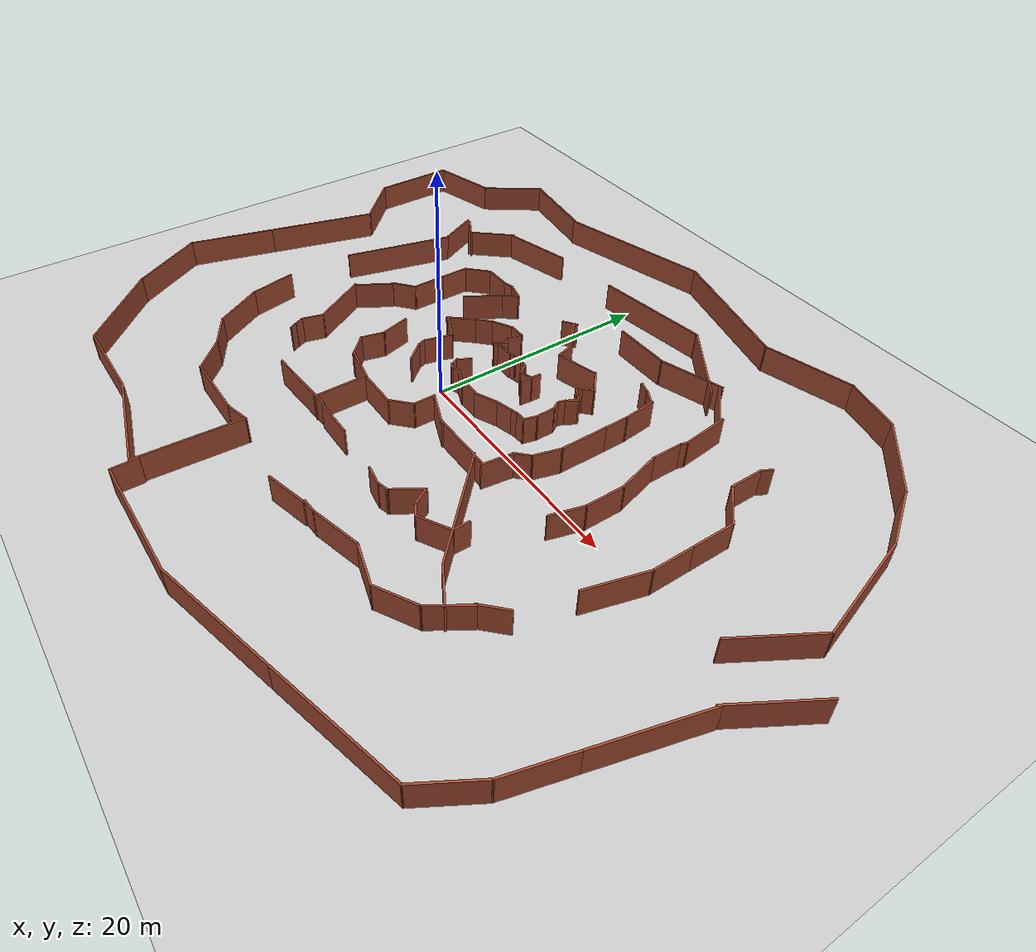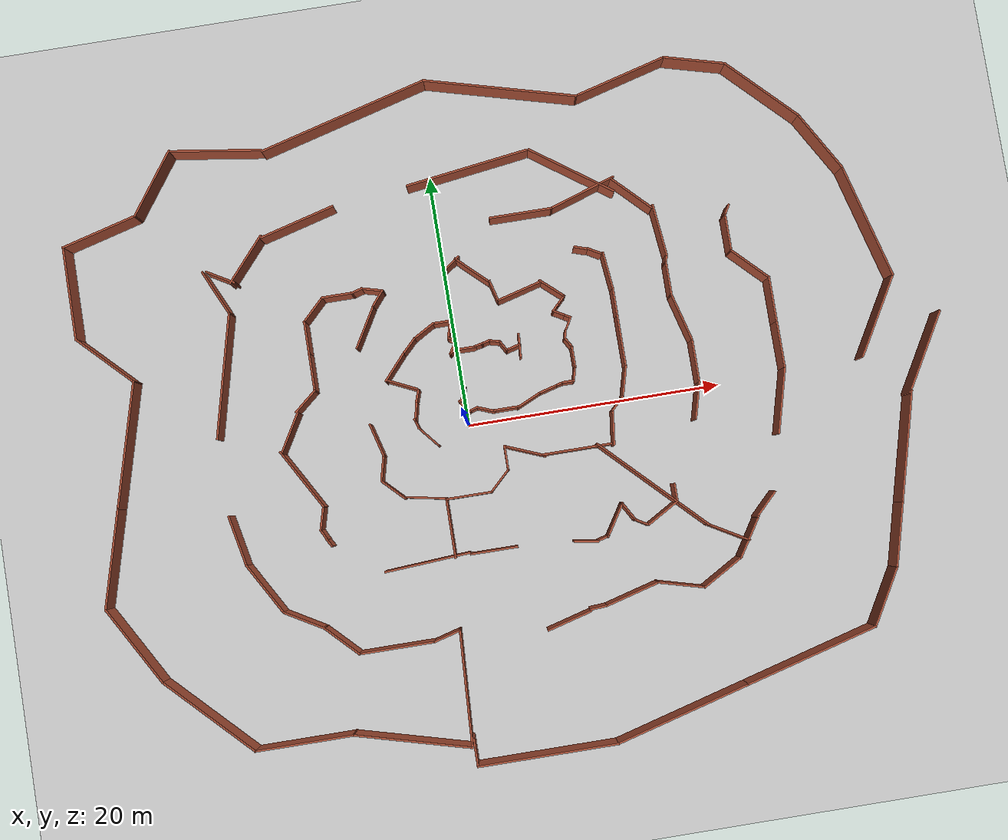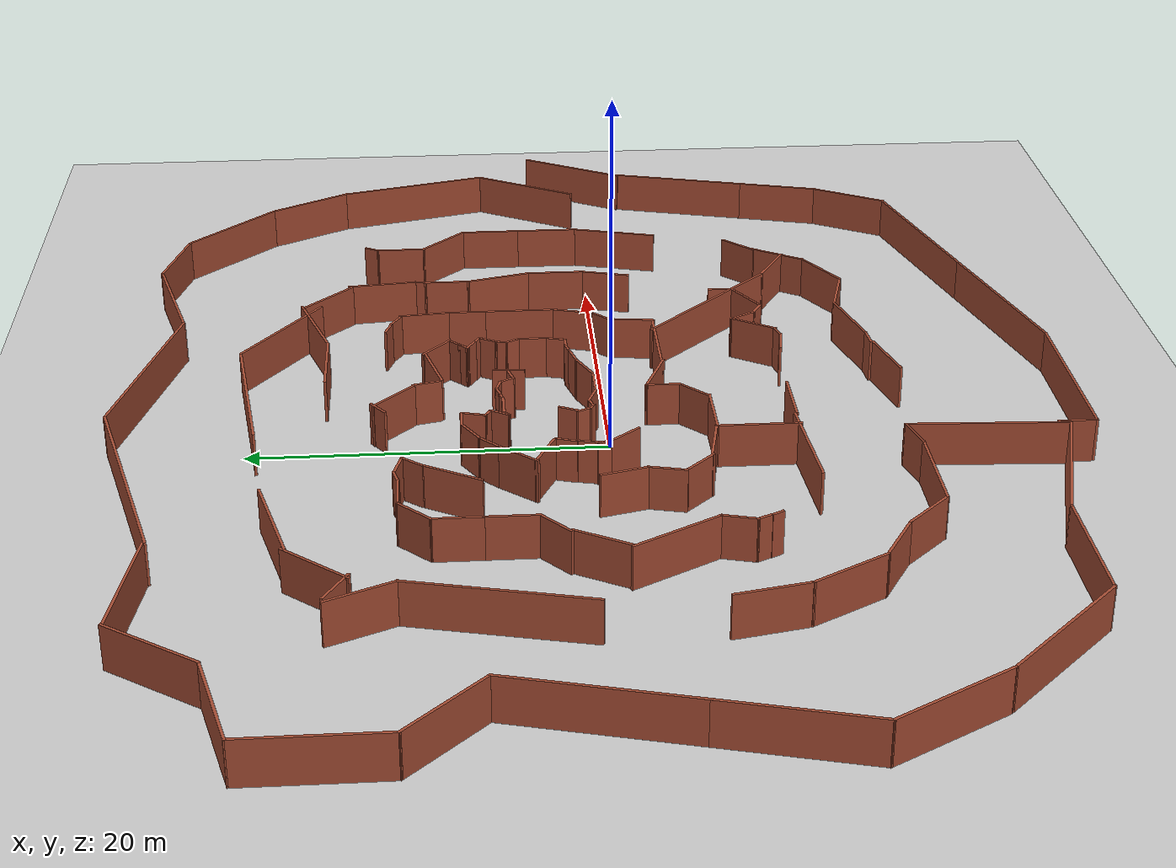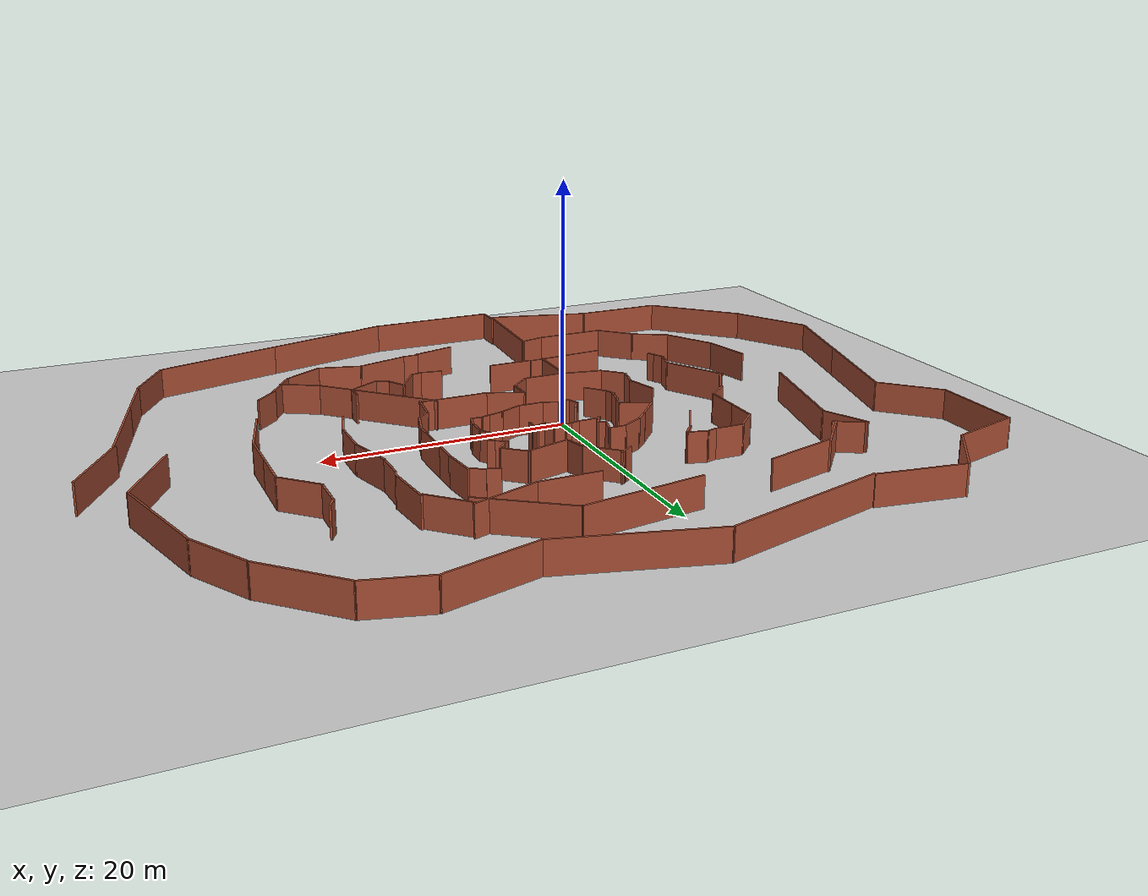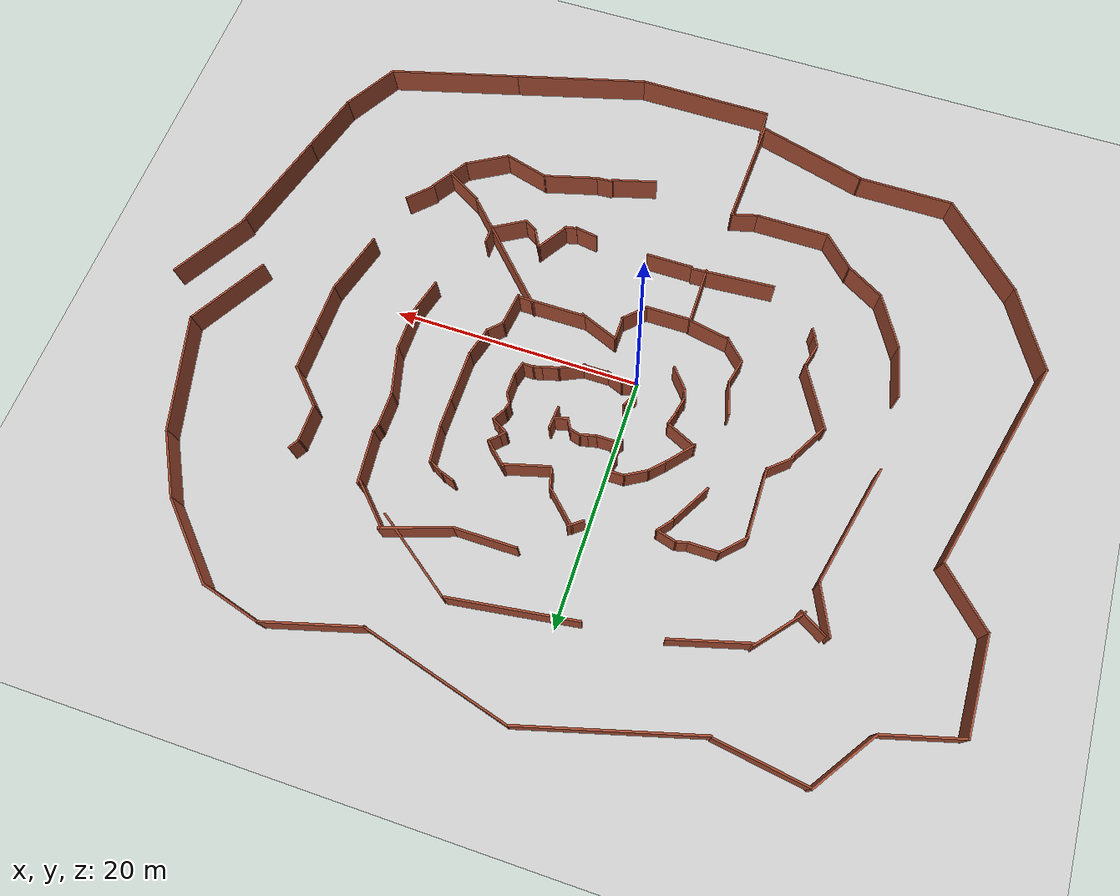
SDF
<?xml version="1.0"?>
<!-- Adapted from XTDrone sitl_config/worlds/indoor4.world; see ASSET_SOURCES.md and LICENSE.XTDrone. -->
<sdf version="1.6">
  <world name="default">
    <light name="sun" type="directional">
      <cast_shadows>1</cast_shadows>
      <pose frame="">0 0 10 0 -0 0</pose>
      <diffuse>0.8 0.8 0.8 1</diffuse>
      <specular>0.2 0.2 0.2 1</specular>
      <attenuation>
        <range>1000</range>
        <constant>0.9</constant>
        <linear>0.01</linear>
        <quadratic>0.001</quadratic>
      </attenuation>
      <direction>-0.5 0.1 -0.9</direction>
    </light>
    <model name="ground_plane">
      <static>1</static>
      <link name="link">
        <collision name="collision">
          <geometry>
            <plane>
              <normal>0 0 1</normal>
              <size>100 100</size>
            </plane>
          </geometry>

            <friction>
              <ode>
                <mu>100</mu>
                <mu2>50</mu2>
              </ode>
              <torsional>
                <ode />
              </torsional>
            </friction>
            <contact>
              <ode />
            </contact>
            <bounce />

          <max_contacts>10</max_contacts>
        </collision>
        <visual name="visual">
          <cast_shadows>0</cast_shadows>
          <geometry>
            <plane>
              <normal>0 0 1</normal>
              <size>100 100</size>
            </plane>
          </geometry>
          <material>
            <script>
              <uri>file://media/materials/scripts/gazebo.material</uri>
              <name>Gazebo/Grey</name>
            </script>
          </material>
        </visual>
        <self_collide>0</self_collide>
        <enable_wind>0</enable_wind>
        <kinematic>0</kinematic>
      </link>
    </model>
    <gravity>0 0 -9.8</gravity>
    <magnetic_field>6e-06 2.3e-05 -4.2e-05</magnetic_field>
    <atmosphere type="adiabatic" />
    <physics name="default_physics" default="0" type="ode">
      <max_step_size>0.004</max_step_size>
      <real_time_factor>1</real_time_factor>
      <real_time_update_rate>250</real_time_update_rate>
    </physics>
    <scene>
      <ambient>0.4 0.4 0.4 1</ambient>
      <background>0.7 0.7 0.7 1</background>
      <shadows>1</shadows>
    </scene>
    <wind />
    <spherical_coordinates>
      <surface_model>EARTH_WGS84</surface_model>
      <latitude_deg>0</latitude_deg>
      <longitude_deg>0</longitude_deg>
      <elevation>0</elevation>
      <heading_deg>0</heading_deg>
    </spherical_coordinates>
    <model name="Untitled1111">
      <link name="Wall_0">
        <pose frame="">-5.60346 -1.19188 0 0 -0 2.26915</pose>
        <self_collide>0</self_collide>
        <enable_wind>0</enable_wind>
        <kinematic>0</kinematic>
        <visual name="Wall_0_Visual">
          <pose frame="">0 0 1.25 0 -0 0</pose>
          <geometry>
            <box>
              <size>2.13585 0.15 2.5</size>
            </box>
          </geometry>
          <material>
            <script>
              <uri>file://media/materials/scripts/gazebo.material</uri>
              <name>Gazebo/Bricks</name>
            </script>
            <ambient>1 1 1 1</ambient>
            <shader type="pixel" />
          </material>
          <meta>
            <layer>0</layer>
          </meta>
          <transparency>0</transparency>
          <cast_shadows>1</cast_shadows>
        </visual>
        <collision name="Wall_0_Collision">
          <laser_retro>0</laser_retro>
          <max_contacts>10</max_contacts>
          <pose frame="">0 0 1.25 0 -0 0</pose>
          <geometry>
            <box>
              <size>2.13585 0.15 2.5</size>
            </box>
          </geometry>

            <friction>
              <ode>
                <mu>1</mu>
                <mu2>1</mu2>
                <fdir1>0 0 0</fdir1>
                <slip1>0</slip1>
                <slip2>0</slip2>
              </ode>
              <torsional>
                <coefficient>1</coefficient>
                <patch_radius>0</patch_radius>
                <surface_radius>0</surface_radius>
                <use_patch_radius>1</use_patch_radius>
                <ode>
                  <slip>0</slip>
                </ode>
              </torsional>
            </friction>
            <bounce>
              <restitution_coefficient>0</restitution_coefficient>
              <threshold>1e+06</threshold>
            </bounce>
            <contact>
              <collide_without_contact>0</collide_without_contact>
              <collide_without_contact_bitmask>1</collide_without_contact_bitmask>
              <collide_bitmask>1</collide_bitmask>
              <ode>
                <soft_cfm>0</soft_cfm>
                <soft_erp>0.2</soft_erp>
                <kp>1e+13</kp>
                <kd>1</kd>
                <max_vel>0.01</max_vel>
                <min_depth>0</min_depth>
              </ode>
              <bullet>
                <split_impulse>1</split_impulse>
                <split_impulse_penetration_threshold>-0.01</split_impulse_penetration_threshold>
                <soft_cfm>0</soft_cfm>
                <soft_erp>0.2</soft_erp>
                <kp>1e+13</kp>
                <kd>1</kd>
              </bullet>
            </contact>

        </collision>
      </link>
      <link name="Wall_1">
        <pose frame="">-6.35977 -0.045403 0 0 -0 1.91127</pose>
        <self_collide>0</self_collide>
        <enable_wind>0</enable_wind>
        <kinematic>0</kinematic>
        <visual name="Wall_1_Visual">
          <pose frame="">0 0 1.25 0 -0 0</pose>
          <geometry>
            <box>
              <size>0.856129 0.15 2.5</size>
            </box>
          </geometry>
          <material>
            <script>
              <uri>file://media/materials/scripts/gazebo.material</uri>
              <name>Gazebo/Bricks</name>
            </script>
            <ambient>1 1 1 1</ambient>
            <shader type="pixel" />
          </material>
          <meta>
            <layer>0</layer>
          </meta>
          <transparency>0</transparency>
          <cast_shadows>1</cast_shadows>
        </visual>
        <collision name="Wall_1_Collision">
          <laser_retro>0</laser_retro>
          <max_contacts>10</max_contacts>
          <pose frame="">0 0 1.25 0 -0 0</pose>
          <geometry>
            <box>
              <size>0.856129 0.15 2.5</size>
            </box>
          </geometry>

            <friction>
              <ode>
                <mu>1</mu>
                <mu2>1</mu2>
                <fdir1>0 0 0</fdir1>
                <slip1>0</slip1>
                <slip2>0</slip2>
              </ode>
              <torsional>
                <coefficient>1</coefficient>
                <patch_radius>0</patch_radius>
                <surface_radius>0</surface_radius>
                <use_patch_radius>1</use_patch_radius>
                <ode>
                  <slip>0</slip>
                </ode>
              </torsional>
            </friction>
            <bounce>
              <restitution_coefficient>0</restitution_coefficient>
              <threshold>1e+06</threshold>
            </bounce>
            <contact>
              <collide_without_contact>0</collide_without_contact>
              <collide_without_contact_bitmask>1</collide_without_contact_bitmask>
              <collide_bitmask>1</collide_bitmask>
              <ode>
                <soft_cfm>0</soft_cfm>
                <soft_erp>0.2</soft_erp>
                <kp>1e+13</kp>
                <kd>1</kd>
                <max_vel>0.01</max_vel>
                <min_depth>0</min_depth>
              </ode>
              <bullet>
                <split_impulse>1</split_impulse>
                <split_impulse_penetration_threshold>-0.01</split_impulse_penetration_threshold>
                <soft_cfm>0</soft_cfm>
                <soft_erp>0.2</soft_erp>
                <kp>1e+13</kp>
                <kd>1</kd>
              </bullet>
            </contact>

        </collision>
      </link>
      <link name="Wall_10">
        <pose frame="">-2.6358 6.01879 0 0 0 -0.523599</pose>
        <self_collide>0</self_collide>
        <enable_wind>0</enable_wind>
        <kinematic>0</kinematic>
        <visual name="Wall_10_Visual">
          <pose frame="">0 0 1.25 0 -0 0</pose>
          <geometry>
            <box>
              <size>0.75 0.15 2.5</size>
            </box>
          </geometry>
          <material>
            <script>
              <uri>file://media/materials/scripts/gazebo.material</uri>
              <name>Gazebo/Bricks</name>
            </script>
            <ambient>1 1 1 1</ambient>
            <shader type="pixel" />
          </material>
          <meta>
            <layer>0</layer>
          </meta>
          <transparency>0</transparency>
          <cast_shadows>1</cast_shadows>
        </visual>
        <collision name="Wall_10_Collision">
          <laser_retro>0</laser_retro>
          <max_contacts>10</max_contacts>
          <pose frame="">0 0 1.25 0 -0 0</pose>
          <geometry>
            <box>
              <size>0.75 0.15 2.5</size>
            </box>
          </geometry>

            <friction>
              <ode>
                <mu>1</mu>
                <mu2>1</mu2>
                <fdir1>0 0 0</fdir1>
                <slip1>0</slip1>
                <slip2>0</slip2>
              </ode>
              <torsional>
                <coefficient>1</coefficient>
                <patch_radius>0</patch_radius>
                <surface_radius>0</surface_radius>
                <use_patch_radius>1</use_patch_radius>
                <ode>
                  <slip>0</slip>
                </ode>
              </torsional>
            </friction>
            <bounce>
              <restitution_coefficient>0</restitution_coefficient>
              <threshold>1e+06</threshold>
            </bounce>
            <contact>
              <collide_without_contact>0</collide_without_contact>
              <collide_without_contact_bitmask>1</collide_without_contact_bitmask>
              <collide_bitmask>1</collide_bitmask>
              <ode>
                <soft_cfm>0</soft_cfm>
                <soft_erp>0.2</soft_erp>
                <kp>1e+13</kp>
                <kd>1</kd>
                <max_vel>0.01</max_vel>
                <min_depth>0</min_depth>
              </ode>
              <bullet>
                <split_impulse>1</split_impulse>
                <split_impulse_penetration_threshold>-0.01</split_impulse_penetration_threshold>
                <soft_cfm>0</soft_cfm>
                <soft_erp>0.2</soft_erp>
                <kp>1e+13</kp>
                <kd>1</kd>
              </bullet>
            </contact>

        </collision>
      </link>
      <link name="Wall_102">
        <pose frame="">15.4586 -1.70898 0 0 -0 1.309</pose>
        <self_collide>0</self_collide>
        <enable_wind>0</enable_wind>
        <kinematic>0</kinematic>
        <visual name="Wall_102_Visual">
          <pose frame="">0 0 1.25 0 -0 0</pose>
          <geometry>
            <box>
              <size>3 0.15 2.5</size>
            </box>
          </geometry>
          <material>
            <script>
              <uri>file://media/materials/scripts/gazebo.material</uri>
              <name>Gazebo/Bricks</name>
            </script>
            <ambient>1 1 1 1</ambient>
            <shader type="pixel" />
          </material>
          <meta>
            <layer>0</layer>
          </meta>
          <transparency>0</transparency>
          <cast_shadows>1</cast_shadows>
        </visual>
        <collision name="Wall_102_Collision">
          <laser_retro>0</laser_retro>
          <max_contacts>10</max_contacts>
          <pose frame="">0 0 1.25 0 -0 0</pose>
          <geometry>
            <box>
              <size>3 0.15 2.5</size>
            </box>
          </geometry>

            <friction>
              <ode>
                <mu>1</mu>
                <mu2>1</mu2>
                <fdir1>0 0 0</fdir1>
                <slip1>0</slip1>
                <slip2>0</slip2>
              </ode>
              <torsional>
                <coefficient>1</coefficient>
                <patch_radius>0</patch_radius>
                <surface_radius>0</surface_radius>
                <use_patch_radius>1</use_patch_radius>
                <ode>
                  <slip>0</slip>
                </ode>
              </torsional>
            </friction>
            <bounce>
              <restitution_coefficient>0</restitution_coefficient>
              <threshold>1e+06</threshold>
            </bounce>
            <contact>
              <collide_without_contact>0</collide_without_contact>
              <collide_without_contact_bitmask>1</collide_without_contact_bitmask>
              <collide_bitmask>1</collide_bitmask>
              <ode>
                <soft_cfm>0</soft_cfm>
                <soft_erp>0.2</soft_erp>
                <kp>1e+13</kp>
                <kd>1</kd>
                <max_vel>0.01</max_vel>
                <min_depth>0</min_depth>
              </ode>
              <bullet>
                <split_impulse>1</split_impulse>
                <split_impulse_penetration_threshold>-0.01</split_impulse_penetration_threshold>
                <soft_cfm>0</soft_cfm>
                <soft_erp>0.2</soft_erp>
                <kp>1e+13</kp>
                <kd>1</kd>
              </bullet>
            </contact>

        </collision>
      </link>
      <link name="Wall_103">
        <pose frame="">15.8274 1.34246 0 0 -0 1.5708</pose>
        <self_collide>0</self_collide>
        <enable_wind>0</enable_wind>
        <kinematic>0</kinematic>
        <visual name="Wall_103_Visual">
          <pose frame="">0 0 1.25 0 -0 0</pose>
          <geometry>
            <box>
              <size>3.5 0.15 2.5</size>
            </box>
          </geometry>
          <material>
            <script>
              <uri>file://media/materials/scripts/gazebo.material</uri>
              <name>Gazebo/Bricks</name>
            </script>
            <ambient>1 1 1 1</ambient>
            <shader type="pixel" />
          </material>
          <meta>
            <layer>0</layer>
          </meta>
          <transparency>0</transparency>
          <cast_shadows>1</cast_shadows>
        </visual>
        <collision name="Wall_103_Collision">
          <laser_retro>0</laser_retro>
          <max_contacts>10</max_contacts>
          <pose frame="">0 0 1.25 0 -0 0</pose>
          <geometry>
            <box>
              <size>3.5 0.15 2.5</size>
            </box>
          </geometry>

            <friction>
              <ode>
                <mu>1</mu>
                <mu2>1</mu2>
                <fdir1>0 0 0</fdir1>
                <slip1>0</slip1>
                <slip2>0</slip2>
              </ode>
              <torsional>
                <coefficient>1</coefficient>
                <patch_radius>0</patch_radius>
                <surface_radius>0</surface_radius>
                <use_patch_radius>1</use_patch_radius>
                <ode>
                  <slip>0</slip>
                </ode>
              </torsional>
            </friction>
            <bounce>
              <restitution_coefficient>0</restitution_coefficient>
              <threshold>1e+06</threshold>
            </bounce>
            <contact>
              <collide_without_contact>0</collide_without_contact>
              <collide_without_contact_bitmask>1</collide_without_contact_bitmask>
              <collide_bitmask>1</collide_bitmask>
              <ode>
                <soft_cfm>0</soft_cfm>
                <soft_erp>0.2</soft_erp>
                <kp>1e+13</kp>
                <kd>1</kd>
                <max_vel>0.01</max_vel>
                <min_depth>0</min_depth>
              </ode>
              <bullet>
                <split_impulse>1</split_impulse>
                <split_impulse_penetration_threshold>-0.01</split_impulse_penetration_threshold>
                <soft_cfm>0</soft_cfm>
                <soft_erp>0.2</soft_erp>
                <kp>1e+13</kp>
                <kd>1</kd>
              </bullet>
            </contact>

        </collision>
      </link>
      <link name="Wall_104">
        <pose frame="">15.3292 4.87687 0 0 -0 1.8326</pose>
        <self_collide>0</self_collide>
        <enable_wind>0</enable_wind>
        <kinematic>0</kinematic>
        <visual name="Wall_104_Visual">
          <pose frame="">0 0 1.25 0 -0 0</pose>
          <geometry>
            <box>
              <size>4 0.15 2.5</size>
            </box>
          </geometry>
          <material>
            <script>
              <uri>file://media/materials/scripts/gazebo.material</uri>
              <name>Gazebo/Bricks</name>
            </script>
            <ambient>1 1 1 1</ambient>
            <shader type="pixel" />
          </material>
          <meta>
            <layer>0</layer>
          </meta>
          <transparency>0</transparency>
          <cast_shadows>1</cast_shadows>
        </visual>
        <collision name="Wall_104_Collision">
          <laser_retro>0</laser_retro>
          <max_contacts>10</max_contacts>
          <pose frame="">0 0 1.25 0 -0 0</pose>
          <geometry>
            <box>
              <size>4 0.15 2.5</size>
            </box>
          </geometry>

            <friction>
              <ode>
                <mu>1</mu>
                <mu2>1</mu2>
                <fdir1>0 0 0</fdir1>
                <slip1>0</slip1>
                <slip2>0</slip2>
              </ode>
              <torsional>
                <coefficient>1</coefficient>
                <patch_radius>0</patch_radius>
                <surface_radius>0</surface_radius>
                <use_patch_radius>1</use_patch_radius>
                <ode>
                  <slip>0</slip>
                </ode>
              </torsional>
            </friction>
            <bounce>
              <restitution_coefficient>0</restitution_coefficient>
              <threshold>1e+06</threshold>
            </bounce>
            <contact>
              <collide_without_contact>0</collide_without_contact>
              <collide_without_contact_bitmask>1</collide_without_contact_bitmask>
              <collide_bitmask>1</collide_bitmask>
              <ode>
                <soft_cfm>0</soft_cfm>
                <soft_erp>0.2</soft_erp>
                <kp>1e+13</kp>
                <kd>1</kd>
                <max_vel>0.01</max_vel>
                <min_depth>0</min_depth>
              </ode>
              <bullet>
                <split_impulse>1</split_impulse>
                <split_impulse_penetration_threshold>-0.01</split_impulse_penetration_threshold>
                <soft_cfm>0</soft_cfm>
                <soft_erp>0.2</soft_erp>
                <kp>1e+13</kp>
                <kd>1</kd>
              </bullet>
            </contact>

        </collision>
      </link>
      <link name="Wall_105">
        <pose frame="">14.831 8.03628 0 0 -0 1.5708</pose>
        <self_collide>0</self_collide>
        <enable_wind>0</enable_wind>
        <kinematic>0</kinematic>
        <visual name="Wall_105_Visual">
          <pose frame="">0 0 1.25 0 -0 0</pose>
          <geometry>
            <box>
              <size>2.75 0.15 2.5</size>
            </box>
          </geometry>
          <material>
            <script>
              <uri>file://media/materials/scripts/gazebo.material</uri>
              <name>Gazebo/Bricks</name>
            </script>
            <ambient>1 1 1 1</ambient>
            <shader type="pixel" />
          </material>
          <meta>
            <layer>0</layer>
          </meta>
          <transparency>0</transparency>
          <cast_shadows>1</cast_shadows>
        </visual>
        <collision name="Wall_105_Collision">
          <laser_retro>0</laser_retro>
          <max_contacts>10</max_contacts>
          <pose frame="">0 0 1.25 0 -0 0</pose>
          <geometry>
            <box>
              <size>2.75 0.15 2.5</size>
            </box>
          </geometry>

            <friction>
              <ode>
                <mu>1</mu>
                <mu2>1</mu2>
                <fdir1>0 0 0</fdir1>
                <slip1>0</slip1>
                <slip2>0</slip2>
              </ode>
              <torsional>
                <coefficient>1</coefficient>
                <patch_radius>0</patch_radius>
                <surface_radius>0</surface_radius>
                <use_patch_radius>1</use_patch_radius>
                <ode>
                  <slip>0</slip>
                </ode>
              </torsional>
            </friction>
            <bounce>
              <restitution_coefficient>0</restitution_coefficient>
              <threshold>1e+06</threshold>
            </bounce>
            <contact>
              <collide_without_contact>0</collide_without_contact>
              <collide_without_contact_bitmask>1</collide_without_contact_bitmask>
              <collide_bitmask>1</collide_bitmask>
              <ode>
                <soft_cfm>0</soft_cfm>
                <soft_erp>0.2</soft_erp>
                <kp>1e+13</kp>
                <kd>1</kd>
                <max_vel>0.01</max_vel>
                <min_depth>0</min_depth>
              </ode>
              <bullet>
                <split_impulse>1</split_impulse>
                <split_impulse_penetration_threshold>-0.01</split_impulse_penetration_threshold>
                <soft_cfm>0</soft_cfm>
                <soft_erp>0.2</soft_erp>
                <kp>1e+13</kp>
                <kd>1</kd>
              </bullet>
            </contact>

        </collision>
      </link>
      <link name="Wall_106">
        <pose frame="">14.9086 9.62606 0 0 -0 1.309</pose>
        <self_collide>0</self_collide>
        <enable_wind>0</enable_wind>
        <kinematic>0</kinematic>
        <visual name="Wall_106_Visual">
          <pose frame="">0 0 1.25 0 -0 0</pose>
          <geometry>
            <box>
              <size>0.75 0.15 2.5</size>
            </box>
          </geometry>
          <material>
            <script>
              <uri>file://media/materials/scripts/gazebo.material</uri>
              <name>Gazebo/Bricks</name>
            </script>
            <ambient>1 1 1 1</ambient>
            <shader type="pixel" />
          </material>
          <meta>
            <layer>0</layer>
          </meta>
          <transparency>0</transparency>
          <cast_shadows>1</cast_shadows>
        </visual>
        <collision name="Wall_106_Collision">
          <laser_retro>0</laser_retro>
          <max_contacts>10</max_contacts>
          <pose frame="">0 0 1.25 0 -0 0</pose>
          <geometry>
            <box>
              <size>0.75 0.15 2.5</size>
            </box>
          </geometry>

            <friction>
              <ode>
                <mu>1</mu>
                <mu2>1</mu2>
                <fdir1>0 0 0</fdir1>
                <slip1>0</slip1>
                <slip2>0</slip2>
              </ode>
              <torsional>
                <coefficient>1</coefficient>
                <patch_radius>0</patch_radius>
                <surface_radius>0</surface_radius>
                <use_patch_radius>1</use_patch_radius>
                <ode>
                  <slip>0</slip>
                </ode>
              </torsional>
            </friction>
            <bounce>
              <restitution_coefficient>0</restitution_coefficient>
              <threshold>1e+06</threshold>
            </bounce>
            <contact>
              <collide_without_contact>0</collide_without_contact>
              <collide_without_contact_bitmask>1</collide_without_contact_bitmask>
              <collide_bitmask>1</collide_bitmask>
              <ode>
                <soft_cfm>0</soft_cfm>
                <soft_erp>0.2</soft_erp>
                <kp>1e+13</kp>
                <kd>1</kd>
                <max_vel>0.01</max_vel>
                <min_depth>0</min_depth>
              </ode>
              <bullet>
                <split_impulse>1</split_impulse>
                <split_impulse_penetration_threshold>-0.01</split_impulse_penetration_threshold>
                <soft_cfm>0</soft_cfm>
                <soft_erp>0.2</soft_erp>
                <kp>1e+13</kp>
                <kd>1</kd>
              </bullet>
            </contact>

        </collision>
      </link>
      <link name="Wall_107">
        <pose frame="">14.774 11.9399 0 0 -0 1.67529</pose>
        <self_collide>0</self_collide>
        <enable_wind>0</enable_wind>
        <kinematic>0</kinematic>
        <visual name="Wall_107_Visual">
          <pose frame="">0 0 1.25 0 -0 0</pose>
          <geometry>
            <box>
              <size>4.22037 0.15 2.5</size>
            </box>
          </geometry>
          <material>
            <script>
              <uri>file://media/materials/scripts/gazebo.material</uri>
              <name>Gazebo/Bricks</name>
            </script>
            <ambient>1 1 1 1</ambient>
            <shader type="pixel" />
          </material>
          <meta>
            <layer>0</layer>
          </meta>
          <transparency>0</transparency>
          <cast_shadows>1</cast_shadows>
        </visual>
        <collision name="Wall_107_Collision">
          <laser_retro>0</laser_retro>
          <max_contacts>10</max_contacts>
          <pose frame="">0 0 1.25 0 -0 0</pose>
          <geometry>
            <box>
              <size>4.22037 0.15 2.5</size>
            </box>
          </geometry>

            <friction>
              <ode>
                <mu>1</mu>
                <mu2>1</mu2>
                <fdir1>0 0 0</fdir1>
                <slip1>0</slip1>
                <slip2>0</slip2>
              </ode>
              <torsional>
                <coefficient>1</coefficient>
                <patch_radius>0</patch_radius>
                <surface_radius>0</surface_radius>
                <use_patch_radius>1</use_patch_radius>
                <ode>
                  <slip>0</slip>
                </ode>
              </torsional>
            </friction>
            <bounce>
              <restitution_coefficient>0</restitution_coefficient>
              <threshold>1e+06</threshold>
            </bounce>
            <contact>
              <collide_without_contact>0</collide_without_contact>
              <collide_without_contact_bitmask>1</collide_without_contact_bitmask>
              <collide_bitmask>1</collide_bitmask>
              <ode>
                <soft_cfm>0</soft_cfm>
                <soft_erp>0.2</soft_erp>
                <kp>1e+13</kp>
                <kd>1</kd>
                <max_vel>0.01</max_vel>
                <min_depth>0</min_depth>
              </ode>
              <bullet>
                <split_impulse>1</split_impulse>
                <split_impulse_penetration_threshold>-0.01</split_impulse_penetration_threshold>
                <soft_cfm>0</soft_cfm>
                <soft_erp>0.2</soft_erp>
                <kp>1e+13</kp>
                <kd>1</kd>
              </bullet>
            </contact>

        </collision>
      </link>
      <link name="Wall_108">
        <pose frame="">13.059 15.1837 0 0 -0 2.35619</pose>
        <self_collide>0</self_collide>
        <enable_wind>0</enable_wind>
        <kinematic>0</kinematic>
        <visual name="Wall_108_Visual">
          <pose frame="">0 0 1.25 0 -0 0</pose>
          <geometry>
            <box>
              <size>4 0.15 2.5</size>
            </box>
          </geometry>
          <material>
            <script>
              <uri>file://media/materials/scripts/gazebo.material</uri>
              <name>Gazebo/Bricks</name>
            </script>
            <ambient>1 1 1 1</ambient>
            <shader type="pixel" />
          </material>
          <meta>
            <layer>0</layer>
          </meta>
          <transparency>0</transparency>
          <cast_shadows>1</cast_shadows>
        </visual>
        <collision name="Wall_108_Collision">
          <laser_retro>0</laser_retro>
          <max_contacts>10</max_contacts>
          <pose frame="">0 0 1.25 0 -0 0</pose>
          <geometry>
            <box>
              <size>4 0.15 2.5</size>
            </box>
          </geometry>

            <friction>
              <ode>
                <mu>1</mu>
                <mu2>1</mu2>
                <fdir1>0 0 0</fdir1>
                <slip1>0</slip1>
                <slip2>0</slip2>
              </ode>
              <torsional>
                <coefficient>1</coefficient>
                <patch_radius>0</patch_radius>
                <surface_radius>0</surface_radius>
                <use_patch_radius>1</use_patch_radius>
                <ode>
                  <slip>0</slip>
                </ode>
              </torsional>
            </friction>
            <bounce>
              <restitution_coefficient>0</restitution_coefficient>
              <threshold>1e+06</threshold>
            </bounce>
            <contact>
              <collide_without_contact>0</collide_without_contact>
              <collide_without_contact_bitmask>1</collide_without_contact_bitmask>
              <collide_bitmask>1</collide_bitmask>
              <ode>
                <soft_cfm>0</soft_cfm>
                <soft_erp>0.2</soft_erp>
                <kp>1e+13</kp>
                <kd>1</kd>
                <max_vel>0.01</max_vel>
                <min_depth>0</min_depth>
              </ode>
              <bullet>
                <split_impulse>1</split_impulse>
                <split_impulse_penetration_threshold>-0.01</split_impulse_penetration_threshold>
                <soft_cfm>0</soft_cfm>
                <soft_erp>0.2</soft_erp>
                <kp>1e+13</kp>
                <kd>1</kd>
              </bullet>
            </contact>

        </collision>
      </link>
      <link name="Wall_109">
        <pose frame="">9.25161 15.8373 0 0 0 -2.82454</pose>
        <self_collide>0</self_collide>
        <enable_wind>0</enable_wind>
        <kinematic>0</kinematic>
        <visual name="Wall_109_Visual">
          <pose frame="">0 0 1.25 0 -0 0</pose>
          <geometry>
            <box>
              <size>5.59694 0.15 2.5</size>
            </box>
          </geometry>
          <material>
            <script>
              <uri>file://media/materials/scripts/gazebo.material</uri>
              <name>Gazebo/Bricks</name>
            </script>
            <ambient>1 1 1 1</ambient>
            <shader type="pixel" />
          </material>
          <meta>
            <layer>0</layer>
          </meta>
          <transparency>0</transparency>
          <cast_shadows>1</cast_shadows>
        </visual>
        <collision name="Wall_109_Collision">
          <laser_retro>0</laser_retro>
          <max_contacts>10</max_contacts>
          <pose frame="">0 0 1.25 0 -0 0</pose>
          <geometry>
            <box>
              <size>5.59694 0.15 2.5</size>
            </box>
          </geometry>

            <friction>
              <ode>
                <mu>1</mu>
                <mu2>1</mu2>
                <fdir1>0 0 0</fdir1>
                <slip1>0</slip1>
                <slip2>0</slip2>
              </ode>
              <torsional>
                <coefficient>1</coefficient>
                <patch_radius>0</patch_radius>
                <surface_radius>0</surface_radius>
                <use_patch_radius>1</use_patch_radius>
                <ode>
                  <slip>0</slip>
                </ode>
              </torsional>
            </friction>
            <bounce>
              <restitution_coefficient>0</restitution_coefficient>
              <threshold>1e+06</threshold>
            </bounce>
            <contact>
              <collide_without_contact>0</collide_without_contact>
              <collide_without_contact_bitmask>1</collide_without_contact_bitmask>
              <collide_bitmask>1</collide_bitmask>
              <ode>
                <soft_cfm>0</soft_cfm>
                <soft_erp>0.2</soft_erp>
                <kp>1e+13</kp>
                <kd>1</kd>
                <max_vel>0.01</max_vel>
                <min_depth>0</min_depth>
              </ode>
              <bullet>
                <split_impulse>1</split_impulse>
                <split_impulse_penetration_threshold>-0.01</split_impulse_penetration_threshold>
                <soft_cfm>0</soft_cfm>
                <soft_erp>0.2</soft_erp>
                <kp>1e+13</kp>
                <kd>1</kd>
              </bullet>
            </contact>

        </collision>
      </link>
      <link name="Wall_11">
        <pose frame="">-2.65099 5.39248 0 0 0 -2.0944</pose>
        <self_collide>0</self_collide>
        <enable_wind>0</enable_wind>
        <kinematic>0</kinematic>
        <visual name="Wall_11_Visual">
          <pose frame="">0 0 1.25 0 -0 0</pose>
          <geometry>
            <box>
              <size>1.25 0.15 2.5</size>
            </box>
          </geometry>
          <material>
            <script>
              <uri>file://media/materials/scripts/gazebo.material</uri>
              <name>Gazebo/Bricks</name>
            </script>
            <ambient>1 1 1 1</ambient>
            <shader type="pixel" />
          </material>
          <meta>
            <layer>0</layer>
          </meta>
          <transparency>0</transparency>
          <cast_shadows>1</cast_shadows>
        </visual>
        <collision name="Wall_11_Collision">
          <laser_retro>0</laser_retro>
          <max_contacts>10</max_contacts>
          <pose frame="">0 0 1.25 0 -0 0</pose>
          <geometry>
            <box>
              <size>1.25 0.15 2.5</size>
            </box>
          </geometry>

            <friction>
              <ode>
                <mu>1</mu>
                <mu2>1</mu2>
                <fdir1>0 0 0</fdir1>
                <slip1>0</slip1>
                <slip2>0</slip2>
              </ode>
              <torsional>
                <coefficient>1</coefficient>
                <patch_radius>0</patch_radius>
                <surface_radius>0</surface_radius>
                <use_patch_radius>1</use_patch_radius>
                <ode>
                  <slip>0</slip>
                </ode>
              </torsional>
            </friction>
            <bounce>
              <restitution_coefficient>0</restitution_coefficient>
              <threshold>1e+06</threshold>
            </bounce>
            <contact>
              <collide_without_contact>0</collide_without_contact>
              <collide_without_contact_bitmask>1</collide_without_contact_bitmask>
              <collide_bitmask>1</collide_bitmask>
              <ode>
                <soft_cfm>0</soft_cfm>
                <soft_erp>0.2</soft_erp>
                <kp>1e+13</kp>
                <kd>1</kd>
                <max_vel>0.01</max_vel>
                <min_depth>0</min_depth>
              </ode>
              <bullet>
                <split_impulse>1</split_impulse>
                <split_impulse_penetration_threshold>-0.01</split_impulse_penetration_threshold>
                <soft_cfm>0</soft_cfm>
                <soft_erp>0.2</soft_erp>
                <kp>1e+13</kp>
                <kd>1</kd>
              </bullet>
            </contact>

        </collision>
      </link>
      <link name="Wall_110">
        <pose frame="">4.23888 14.9882 0 0 -0 3.14159</pose>
        <self_collide>0</self_collide>
        <enable_wind>0</enable_wind>
        <kinematic>0</kinematic>
        <visual name="Wall_110_Visual">
          <pose frame="">0 0 1.25 0 -0 0</pose>
          <geometry>
            <box>
              <size>5 0.15 2.5</size>
            </box>
          </geometry>
          <material>
            <script>
              <uri>file://media/materials/scripts/gazebo.material</uri>
              <name>Gazebo/Bricks</name>
            </script>
            <ambient>1 1 1 1</ambient>
            <shader type="pixel" />
          </material>
          <meta>
            <layer>0</layer>
          </meta>
          <transparency>0</transparency>
          <cast_shadows>1</cast_shadows>
        </visual>
        <collision name="Wall_110_Collision">
          <laser_retro>0</laser_retro>
          <max_contacts>10</max_contacts>
          <pose frame="">0 0 1.25 0 -0 0</pose>
          <geometry>
            <box>
              <size>5 0.15 2.5</size>
            </box>
          </geometry>

            <friction>
              <ode>
                <mu>1</mu>
                <mu2>1</mu2>
                <fdir1>0 0 0</fdir1>
                <slip1>0</slip1>
                <slip2>0</slip2>
              </ode>
              <torsional>
                <coefficient>1</coefficient>
                <patch_radius>0</patch_radius>
                <surface_radius>0</surface_radius>
                <use_patch_radius>1</use_patch_radius>
                <ode>
                  <slip>0</slip>
                </ode>
              </torsional>
            </friction>
            <bounce>
              <restitution_coefficient>0</restitution_coefficient>
              <threshold>1e+06</threshold>
            </bounce>
            <contact>
              <collide_without_contact>0</collide_without_contact>
              <collide_without_contact_bitmask>1</collide_without_contact_bitmask>
              <collide_bitmask>1</collide_bitmask>
              <ode>
                <soft_cfm>0</soft_cfm>
                <soft_erp>0.2</soft_erp>
                <kp>1e+13</kp>
                <kd>1</kd>
                <max_vel>0.01</max_vel>
                <min_depth>0</min_depth>
              </ode>
              <bullet>
                <split_impulse>1</split_impulse>
                <split_impulse_penetration_threshold>-0.01</split_impulse_penetration_threshold>
                <soft_cfm>0</soft_cfm>
                <soft_erp>0.2</soft_erp>
                <kp>1e+13</kp>
                <kd>1</kd>
              </bullet>
            </contact>

        </collision>
      </link>
      <link name="Wall_112">
        <pose frame="">-13.2085 17.0795 0 0 0 -2.87979</pose>
        <self_collide>0</self_collide>
        <enable_wind>0</enable_wind>
        <kinematic>0</kinematic>
        <visual name="Wall_112_Visual">
          <pose frame="">0 0 1.25 0 -0 0</pose>
          <geometry>
            <box>
              <size>6.25 0.15 2.5</size>
            </box>
          </geometry>
          <material>
            <script>
              <uri>file://media/materials/scripts/gazebo.material</uri>
              <name>Gazebo/Bricks</name>
            </script>
            <ambient>1 1 1 1</ambient>
            <shader type="pixel" />
          </material>
          <meta>
            <layer>0</layer>
          </meta>
          <transparency>0</transparency>
          <cast_shadows>1</cast_shadows>
        </visual>
        <collision name="Wall_112_Collision">
          <laser_retro>0</laser_retro>
          <max_contacts>10</max_contacts>
          <pose frame="">0 0 1.25 0 -0 0</pose>
          <geometry>
            <box>
              <size>6.25 0.15 2.5</size>
            </box>
          </geometry>

            <friction>
              <ode>
                <mu>1</mu>
                <mu2>1</mu2>
                <fdir1>0 0 0</fdir1>
                <slip1>0</slip1>
                <slip2>0</slip2>
              </ode>
              <torsional>
                <coefficient>1</coefficient>
                <patch_radius>0</patch_radius>
                <surface_radius>0</surface_radius>
                <use_patch_radius>1</use_patch_radius>
                <ode>
                  <slip>0</slip>
                </ode>
              </torsional>
            </friction>
            <bounce>
              <restitution_coefficient>0</restitution_coefficient>
              <threshold>1e+06</threshold>
            </bounce>
            <contact>
              <collide_without_contact>0</collide_without_contact>
              <collide_without_contact_bitmask>1</collide_without_contact_bitmask>
              <collide_bitmask>1</collide_bitmask>
              <ode>
                <soft_cfm>0</soft_cfm>
                <soft_erp>0.2</soft_erp>
                <kp>1e+13</kp>
                <kd>1</kd>
                <max_vel>0.01</max_vel>
                <min_depth>0</min_depth>
              </ode>
              <bullet>
                <split_impulse>1</split_impulse>
                <split_impulse_penetration_threshold>-0.01</split_impulse_penetration_threshold>
                <soft_cfm>0</soft_cfm>
                <soft_erp>0.2</soft_erp>
                <kp>1e+13</kp>
                <kd>1</kd>
              </bullet>
            </contact>

        </collision>
      </link>
      <link name="Wall_113">
        <pose frame="">-17.5992 14.7841 0 0 0 -2.28433</pose>
        <self_collide>0</self_collide>
        <enable_wind>0</enable_wind>
        <kinematic>0</kinematic>
        <visual name="Wall_113_Visual">
          <pose frame="">0 0 1.25 0 -0 0</pose>
          <geometry>
            <box>
              <size>4.56448 0.15 2.5</size>
            </box>
          </geometry>
          <material>
            <script>
              <uri>file://media/materials/scripts/gazebo.material</uri>
              <name>Gazebo/Bricks</name>
            </script>
            <ambient>1 1 1 1</ambient>
            <shader type="pixel" />
          </material>
          <meta>
            <layer>0</layer>
          </meta>
          <transparency>0</transparency>
          <cast_shadows>1</cast_shadows>
        </visual>
        <collision name="Wall_113_Collision">
          <laser_retro>0</laser_retro>
          <max_contacts>10</max_contacts>
          <pose frame="">0 0 1.25 0 -0 0</pose>
          <geometry>
            <box>
              <size>4.56448 0.15 2.5</size>
            </box>
          </geometry>

            <friction>
              <ode>
                <mu>1</mu>
                <mu2>1</mu2>
                <fdir1>0 0 0</fdir1>
                <slip1>0</slip1>
                <slip2>0</slip2>
              </ode>
              <torsional>
                <coefficient>1</coefficient>
                <patch_radius>0</patch_radius>
                <surface_radius>0</surface_radius>
                <use_patch_radius>1</use_patch_radius>
                <ode>
                  <slip>0</slip>
                </ode>
              </torsional>
            </friction>
            <bounce>
              <restitution_coefficient>0</restitution_coefficient>
              <threshold>1e+06</threshold>
            </bounce>
            <contact>
              <collide_without_contact>0</collide_without_contact>
              <collide_without_contact_bitmask>1</collide_without_contact_bitmask>
              <collide_bitmask>1</collide_bitmask>
              <ode>
                <soft_cfm>0</soft_cfm>
                <soft_erp>0.2</soft_erp>
                <kp>1e+13</kp>
                <kd>1</kd>
                <max_vel>0.01</max_vel>
                <min_depth>0</min_depth>
              </ode>
              <bullet>
                <split_impulse>1</split_impulse>
                <split_impulse_penetration_threshold>-0.01</split_impulse_penetration_threshold>
                <soft_cfm>0</soft_cfm>
                <soft_erp>0.2</soft_erp>
                <kp>1e+13</kp>
                <kd>1</kd>
              </bullet>
            </contact>

        </collision>
      </link>
      <link name="Wall_114">
        <pose frame="">-19.736 13.7028 0 0 -0 2.61799</pose>
        <self_collide>0</self_collide>
        <enable_wind>0</enable_wind>
        <kinematic>0</kinematic>
        <visual name="Wall_114_Visual">
          <pose frame="">0 0 1.25 0 -0 0</pose>
          <geometry>
            <box>
              <size>2.5 0.15 2.5</size>
            </box>
          </geometry>
          <material>
            <script>
              <uri>file://media/materials/scripts/gazebo.material</uri>
              <name>Gazebo/Bricks</name>
            </script>
            <ambient>1 1 1 1</ambient>
            <shader type="pixel" />
          </material>
          <meta>
            <layer>0</layer>
          </meta>
          <transparency>0</transparency>
          <cast_shadows>1</cast_shadows>
        </visual>
        <collision name="Wall_114_Collision">
          <laser_retro>0</laser_retro>
          <max_contacts>10</max_contacts>
          <pose frame="">0 0 1.25 0 -0 0</pose>
          <geometry>
            <box>
              <size>2.5 0.15 2.5</size>
            </box>
          </geometry>

            <friction>
              <ode>
                <mu>1</mu>
                <mu2>1</mu2>
                <fdir1>0 0 0</fdir1>
                <slip1>0</slip1>
                <slip2>0</slip2>
              </ode>
              <torsional>
                <coefficient>1</coefficient>
                <patch_radius>0</patch_radius>
                <surface_radius>0</surface_radius>
                <use_patch_radius>1</use_patch_radius>
                <ode>
                  <slip>0</slip>
                </ode>
              </torsional>
            </friction>
            <bounce>
              <restitution_coefficient>0</restitution_coefficient>
              <threshold>1e+06</threshold>
            </bounce>
            <contact>
              <collide_without_contact>0</collide_without_contact>
              <collide_without_contact_bitmask>1</collide_without_contact_bitmask>
              <collide_bitmask>1</collide_bitmask>
              <ode>
                <soft_cfm>0</soft_cfm>
                <soft_erp>0.2</soft_erp>
                <kp>1e+13</kp>
                <kd>1</kd>
                <max_vel>0.01</max_vel>
                <min_depth>0</min_depth>
              </ode>
              <bullet>
                <split_impulse>1</split_impulse>
                <split_impulse_penetration_threshold>-0.01</split_impulse_penetration_threshold>
                <soft_cfm>0</soft_cfm>
                <soft_erp>0.2</soft_erp>
                <kp>1e+13</kp>
                <kd>1</kd>
              </bullet>
            </contact>

        </collision>
      </link>
      <link name="Wall_115">
        <pose frame="">-20.2762 12.5425 0 0 0 -1.14016</pose>
        <self_collide>0</self_collide>
        <enable_wind>0</enable_wind>
        <kinematic>0</kinematic>
        <visual name="Wall_115_Visual">
          <pose frame="">0 0 1.25 0 -0 0</pose>
          <geometry>
            <box>
              <size>3.99669 0.15 2.5</size>
            </box>
          </geometry>
          <material>
            <script>
              <uri>file://media/materials/scripts/gazebo.material</uri>
              <name>Gazebo/Bricks</name>
            </script>
            <ambient>1 1 1 1</ambient>
            <shader type="pixel" />
          </material>
          <meta>
            <layer>0</layer>
          </meta>
          <transparency>0</transparency>
          <cast_shadows>1</cast_shadows>
        </visual>
        <collision name="Wall_115_Collision">
          <laser_retro>0</laser_retro>
          <max_contacts>10</max_contacts>
          <pose frame="">0 0 1.25 0 -0 0</pose>
          <geometry>
            <box>
              <size>3.99669 0.15 2.5</size>
            </box>
          </geometry>

            <friction>
              <ode>
                <mu>1</mu>
                <mu2>1</mu2>
                <fdir1>0 0 0</fdir1>
                <slip1>0</slip1>
                <slip2>0</slip2>
              </ode>
              <torsional>
                <coefficient>1</coefficient>
                <patch_radius>0</patch_radius>
                <surface_radius>0</surface_radius>
                <use_patch_radius>1</use_patch_radius>
                <ode>
                  <slip>0</slip>
                </ode>
              </torsional>
            </friction>
            <bounce>
              <restitution_coefficient>0</restitution_coefficient>
              <threshold>1e+06</threshold>
            </bounce>
            <contact>
              <collide_without_contact>0</collide_without_contact>
              <collide_without_contact_bitmask>1</collide_without_contact_bitmask>
              <collide_bitmask>1</collide_bitmask>
              <ode>
                <soft_cfm>0</soft_cfm>
                <soft_erp>0.2</soft_erp>
                <kp>1e+13</kp>
                <kd>1</kd>
                <max_vel>0.01</max_vel>
                <min_depth>0</min_depth>
              </ode>
              <bullet>
                <split_impulse>1</split_impulse>
                <split_impulse_penetration_threshold>-0.01</split_impulse_penetration_threshold>
                <soft_cfm>0</soft_cfm>
                <soft_erp>0.2</soft_erp>
                <kp>1e+13</kp>
                <kd>1</kd>
              </bullet>
            </contact>

        </collision>
      </link>
      <link name="Wall_116">
        <pose frame="">-20.6372 6.01657 0 0 0 -1.80973</pose>
        <self_collide>0</self_collide>
        <enable_wind>0</enable_wind>
        <kinematic>0</kinematic>
        <visual name="Wall_116_Visual">
          <pose frame="">0 0 1.25 0 -0 0</pose>
          <geometry>
            <box>
              <size>9.98588 0.15 2.5</size>
            </box>
          </geometry>
          <material>
            <script>
              <uri>file://media/materials/scripts/gazebo.material</uri>
              <name>Gazebo/Bricks</name>
            </script>
            <ambient>1 1 1 1</ambient>
            <shader type="pixel" />
          </material>
          <meta>
            <layer>0</layer>
          </meta>
          <transparency>0</transparency>
          <cast_shadows>1</cast_shadows>
        </visual>
        <collision name="Wall_116_Collision">
          <laser_retro>0</laser_retro>
          <max_contacts>10</max_contacts>
          <pose frame="">0 0 1.25 0 -0 0</pose>
          <geometry>
            <box>
              <size>9.98588 0.15 2.5</size>
            </box>
          </geometry>

            <friction>
              <ode>
                <mu>1</mu>
                <mu2>1</mu2>
                <fdir1>0 0 0</fdir1>
                <slip1>0</slip1>
                <slip2>0</slip2>
              </ode>
              <torsional>
                <coefficient>1</coefficient>
                <patch_radius>0</patch_radius>
                <surface_radius>0</surface_radius>
                <use_patch_radius>1</use_patch_radius>
                <ode>
                  <slip>0</slip>
                </ode>
              </torsional>
            </friction>
            <bounce>
              <restitution_coefficient>0</restitution_coefficient>
              <threshold>1e+06</threshold>
            </bounce>
            <contact>
              <collide_without_contact>0</collide_without_contact>
              <collide_without_contact_bitmask>1</collide_without_contact_bitmask>
              <collide_bitmask>1</collide_bitmask>
              <ode>
                <soft_cfm>0</soft_cfm>
                <soft_erp>0.2</soft_erp>
                <kp>1e+13</kp>
                <kd>1</kd>
                <max_vel>0.01</max_vel>
                <min_depth>0</min_depth>
              </ode>
              <bullet>
                <split_impulse>1</split_impulse>
                <split_impulse_penetration_threshold>-0.01</split_impulse_penetration_threshold>
                <soft_cfm>0</soft_cfm>
                <soft_erp>0.2</soft_erp>
                <kp>1e+13</kp>
                <kd>1</kd>
              </bullet>
            </contact>

        </collision>
      </link>
      <link name="Wall_118">
        <pose frame="">-21.3942 -6.83376 0 0 0 -1.36735</pose>
        <self_collide>0</self_collide>
        <enable_wind>0</enable_wind>
        <kinematic>0</kinematic>
        <visual name="Wall_118_Visual">
          <pose frame="">0 0 1.25 0 -0 0</pose>
          <geometry>
            <box>
              <size>4.17727 0.15 2.5</size>
            </box>
          </geometry>
          <material>
            <script>
              <uri>file://media/materials/scripts/gazebo.material</uri>
              <name>Gazebo/Bricks</name>
            </script>
            <ambient>1 1 1 1</ambient>
            <shader type="pixel" />
          </material>
          <meta>
            <layer>0</layer>
          </meta>
          <transparency>0</transparency>
          <cast_shadows>1</cast_shadows>
        </visual>
        <collision name="Wall_118_Collision">
          <laser_retro>0</laser_retro>
          <max_contacts>10</max_contacts>
          <pose frame="">0 0 1.25 0 -0 0</pose>
          <geometry>
            <box>
              <size>4.17727 0.15 2.5</size>
            </box>
          </geometry>

            <friction>
              <ode>
                <mu>1</mu>
                <mu2>1</mu2>
                <fdir1>0 0 0</fdir1>
                <slip1>0</slip1>
                <slip2>0</slip2>
              </ode>
              <torsional>
                <coefficient>1</coefficient>
                <patch_radius>0</patch_radius>
                <surface_radius>0</surface_radius>
                <use_patch_radius>1</use_patch_radius>
                <ode>
                  <slip>0</slip>
                </ode>
              </torsional>
            </friction>
            <bounce>
              <restitution_coefficient>0</restitution_coefficient>
              <threshold>1e+06</threshold>
            </bounce>
            <contact>
              <collide_without_contact>0</collide_without_contact>
              <collide_without_contact_bitmask>1</collide_without_contact_bitmask>
              <collide_bitmask>1</collide_bitmask>
              <ode>
                <soft_cfm>0</soft_cfm>
                <soft_erp>0.2</soft_erp>
                <kp>1e+13</kp>
                <kd>1</kd>
                <max_vel>0.01</max_vel>
                <min_depth>0</min_depth>
              </ode>
              <bullet>
                <split_impulse>1</split_impulse>
                <split_impulse_penetration_threshold>-0.01</split_impulse_penetration_threshold>
                <soft_cfm>0</soft_cfm>
                <soft_erp>0.2</soft_erp>
                <kp>1e+13</kp>
                <kd>1</kd>
              </bullet>
            </contact>

        </collision>
      </link>
      <link name="Wall_119">
        <pose frame="">-19.8374 -10.7977 0 0 0 -1.0472</pose>
        <self_collide>0</self_collide>
        <enable_wind>0</enable_wind>
        <kinematic>0</kinematic>
        <visual name="Wall_119_Visual">
          <pose frame="">0 0 1.25 0 -0 0</pose>
          <geometry>
            <box>
              <size>4.75 0.15 2.5</size>
            </box>
          </geometry>
          <material>
            <script>
              <uri>file://media/materials/scripts/gazebo.material</uri>
              <name>Gazebo/Bricks</name>
            </script>
            <ambient>1 1 1 1</ambient>
            <shader type="pixel" />
          </material>
          <meta>
            <layer>0</layer>
          </meta>
          <transparency>0</transparency>
          <cast_shadows>1</cast_shadows>
        </visual>
        <collision name="Wall_119_Collision">
          <laser_retro>0</laser_retro>
          <max_contacts>10</max_contacts>
          <pose frame="">0 0 1.25 0 -0 0</pose>
          <geometry>
            <box>
              <size>4.75 0.15 2.5</size>
            </box>
          </geometry>

            <friction>
              <ode>
                <mu>1</mu>
                <mu2>1</mu2>
                <fdir1>0 0 0</fdir1>
                <slip1>0</slip1>
                <slip2>0</slip2>
              </ode>
              <torsional>
                <coefficient>1</coefficient>
                <patch_radius>0</patch_radius>
                <surface_radius>0</surface_radius>
                <use_patch_radius>1</use_patch_radius>
                <ode>
                  <slip>0</slip>
                </ode>
              </torsional>
            </friction>
            <bounce>
              <restitution_coefficient>0</restitution_coefficient>
              <threshold>1e+06</threshold>
            </bounce>
            <contact>
              <collide_without_contact>0</collide_without_contact>
              <collide_without_contact_bitmask>1</collide_without_contact_bitmask>
              <collide_bitmask>1</collide_bitmask>
              <ode>
                <soft_cfm>0</soft_cfm>
                <soft_erp>0.2</soft_erp>
                <kp>1e+13</kp>
                <kd>1</kd>
                <max_vel>0.01</max_vel>
                <min_depth>0</min_depth>
              </ode>
              <bullet>
                <split_impulse>1</split_impulse>
                <split_impulse_penetration_threshold>-0.01</split_impulse_penetration_threshold>
                <soft_cfm>0</soft_cfm>
                <soft_erp>0.2</soft_erp>
                <kp>1e+13</kp>
                <kd>1</kd>
              </bullet>
            </contact>

        </collision>
      </link>
      <link name="Wall_12">
        <pose frame="">-2.75032 5.05347 0 0 -0 0.663411</pose>
        <self_collide>0</self_collide>
        <enable_wind>0</enable_wind>
        <kinematic>0</kinematic>
        <visual name="Wall_12_Visual">
          <pose frame="">0 0 1.25 0 -0 0</pose>
          <geometry>
            <box>
              <size>0.595922 0.15 2.5</size>
            </box>
          </geometry>
          <material>
            <script>
              <uri>file://media/materials/scripts/gazebo.material</uri>
              <name>Gazebo/Bricks</name>
            </script>
            <ambient>1 1 1 1</ambient>
            <shader type="pixel" />
          </material>
          <meta>
            <layer>0</layer>
          </meta>
          <transparency>0</transparency>
          <cast_shadows>1</cast_shadows>
        </visual>
        <collision name="Wall_12_Collision">
          <laser_retro>0</laser_retro>
          <max_contacts>10</max_contacts>
          <pose frame="">0 0 1.25 0 -0 0</pose>
          <geometry>
            <box>
              <size>0.595922 0.15 2.5</size>
            </box>
          </geometry>

            <friction>
              <ode>
                <mu>1</mu>
                <mu2>1</mu2>
                <fdir1>0 0 0</fdir1>
                <slip1>0</slip1>
                <slip2>0</slip2>
              </ode>
              <torsional>
                <coefficient>1</coefficient>
                <patch_radius>0</patch_radius>
                <surface_radius>0</surface_radius>
                <use_patch_radius>1</use_patch_radius>
                <ode>
                  <slip>0</slip>
                </ode>
              </torsional>
            </friction>
            <bounce>
              <restitution_coefficient>0</restitution_coefficient>
              <threshold>1e+06</threshold>
            </bounce>
            <contact>
              <collide_without_contact>0</collide_without_contact>
              <collide_without_contact_bitmask>1</collide_without_contact_bitmask>
              <collide_bitmask>1</collide_bitmask>
              <ode>
                <soft_cfm>0</soft_cfm>
                <soft_erp>0.2</soft_erp>
                <kp>1e+13</kp>
                <kd>1</kd>
                <max_vel>0.01</max_vel>
                <min_depth>0</min_depth>
              </ode>
              <bullet>
                <split_impulse>1</split_impulse>
                <split_impulse_penetration_threshold>-0.01</split_impulse_penetration_threshold>
                <soft_cfm>0</soft_cfm>
                <soft_erp>0.2</soft_erp>
                <kp>1e+13</kp>
                <kd>1</kd>
              </bullet>
            </contact>

        </collision>
      </link>
      <link name="Wall_120">
        <pose frame="">-17.2368 -13.6271 0 0 0 -0.523599</pose>
        <self_collide>0</self_collide>
        <enable_wind>0</enable_wind>
        <kinematic>0</kinematic>
        <visual name="Wall_120_Visual">
          <pose frame="">0 0 1.25 0 -0 0</pose>
          <geometry>
            <box>
              <size>3.5 0.15 2.5</size>
            </box>
          </geometry>
          <material>
            <script>
              <uri>file://media/materials/scripts/gazebo.material</uri>
              <name>Gazebo/Bricks</name>
            </script>
            <ambient>1 1 1 1</ambient>
            <shader type="pixel" />
          </material>
          <meta>
            <layer>0</layer>
          </meta>
          <transparency>0</transparency>
          <cast_shadows>1</cast_shadows>
        </visual>
        <collision name="Wall_120_Collision">
          <laser_retro>0</laser_retro>
          <max_contacts>10</max_contacts>
          <pose frame="">0 0 1.25 0 -0 0</pose>
          <geometry>
            <box>
              <size>3.5 0.15 2.5</size>
            </box>
          </geometry>

            <friction>
              <ode>
                <mu>1</mu>
                <mu2>1</mu2>
                <fdir1>0 0 0</fdir1>
                <slip1>0</slip1>
                <slip2>0</slip2>
              </ode>
              <torsional>
                <coefficient>1</coefficient>
                <patch_radius>0</patch_radius>
                <surface_radius>0</surface_radius>
                <use_patch_radius>1</use_patch_radius>
                <ode>
                  <slip>0</slip>
                </ode>
              </torsional>
            </friction>
            <bounce>
              <restitution_coefficient>0</restitution_coefficient>
              <threshold>1e+06</threshold>
            </bounce>
            <contact>
              <collide_without_contact>0</collide_without_contact>
              <collide_without_contact_bitmask>1</collide_without_contact_bitmask>
              <collide_bitmask>1</collide_bitmask>
              <ode>
                <soft_cfm>0</soft_cfm>
                <soft_erp>0.2</soft_erp>
                <kp>1e+13</kp>
                <kd>1</kd>
                <max_vel>0.01</max_vel>
                <min_depth>0</min_depth>
              </ode>
              <bullet>
                <split_impulse>1</split_impulse>
                <split_impulse_penetration_threshold>-0.01</split_impulse_penetration_threshold>
                <soft_cfm>0</soft_cfm>
                <soft_erp>0.2</soft_erp>
                <kp>1e+13</kp>
                <kd>1</kd>
              </bullet>
            </contact>

        </collision>
      </link>
      <link name="Wall_121">
        <pose frame="">-14.6018 -15.649 0 0 0 -0.785398</pose>
        <self_collide>0</self_collide>
        <enable_wind>0</enable_wind>
        <kinematic>0</kinematic>
        <visual name="Wall_121_Visual">
          <pose frame="">0 0 1.25 0 -0 0</pose>
          <geometry>
            <box>
              <size>3.5 0.15 2.5</size>
            </box>
          </geometry>
          <material>
            <script>
              <uri>file://media/materials/scripts/gazebo.material</uri>
              <name>Gazebo/Bricks</name>
            </script>
            <ambient>1 1 1 1</ambient>
            <shader type="pixel" />
          </material>
          <meta>
            <layer>0</layer>
          </meta>
          <transparency>0</transparency>
          <cast_shadows>1</cast_shadows>
        </visual>
        <collision name="Wall_121_Collision">
          <laser_retro>0</laser_retro>
          <max_contacts>10</max_contacts>
          <pose frame="">0 0 1.25 0 -0 0</pose>
          <geometry>
            <box>
              <size>3.5 0.15 2.5</size>
            </box>
          </geometry>

            <friction>
              <ode>
                <mu>1</mu>
                <mu2>1</mu2>
                <fdir1>0 0 0</fdir1>
                <slip1>0</slip1>
                <slip2>0</slip2>
              </ode>
              <torsional>
                <coefficient>1</coefficient>
                <patch_radius>0</patch_radius>
                <surface_radius>0</surface_radius>
                <use_patch_radius>1</use_patch_radius>
                <ode>
                  <slip>0</slip>
                </ode>
              </torsional>
            </friction>
            <bounce>
              <restitution_coefficient>0</restitution_coefficient>
              <threshold>1e+06</threshold>
            </bounce>
            <contact>
              <collide_without_contact>0</collide_without_contact>
              <collide_without_contact_bitmask>1</collide_without_contact_bitmask>
              <collide_bitmask>1</collide_bitmask>
              <ode>
                <soft_cfm>0</soft_cfm>
                <soft_erp>0.2</soft_erp>
                <kp>1e+13</kp>
                <kd>1</kd>
                <max_vel>0.01</max_vel>
                <min_depth>0</min_depth>
              </ode>
              <bullet>
                <split_impulse>1</split_impulse>
                <split_impulse_penetration_threshold>-0.01</split_impulse_penetration_threshold>
                <soft_cfm>0</soft_cfm>
                <soft_erp>0.2</soft_erp>
                <kp>1e+13</kp>
                <kd>1</kd>
              </bullet>
            </contact>

        </collision>
      </link>
      <link name="Wall_122">
        <pose frame="">-10.4924 -16.8334 0 0 -0 0</pose>
        <self_collide>0</self_collide>
        <enable_wind>0</enable_wind>
        <kinematic>0</kinematic>
        <visual name="Wall_122_Visual">
          <pose frame="">0 0 1.25 0 -0 0</pose>
          <geometry>
            <box>
              <size>6 0.15 2.5</size>
            </box>
          </geometry>
          <material>
            <script>
              <uri>file://media/materials/scripts/gazebo.material</uri>
              <name>Gazebo/Bricks</name>
            </script>
            <ambient>1 1 1 1</ambient>
            <shader type="pixel" />
          </material>
          <meta>
            <layer>0</layer>
          </meta>
          <transparency>0</transparency>
          <cast_shadows>1</cast_shadows>
        </visual>
        <collision name="Wall_122_Collision">
          <laser_retro>0</laser_retro>
          <max_contacts>10</max_contacts>
          <pose frame="">0 0 1.25 0 -0 0</pose>
          <geometry>
            <box>
              <size>6 0.15 2.5</size>
            </box>
          </geometry>

            <friction>
              <ode>
                <mu>1</mu>
                <mu2>1</mu2>
                <fdir1>0 0 0</fdir1>
                <slip1>0</slip1>
                <slip2>0</slip2>
              </ode>
              <torsional>
                <coefficient>1</coefficient>
                <patch_radius>0</patch_radius>
                <surface_radius>0</surface_radius>
                <use_patch_radius>1</use_patch_radius>
                <ode>
                  <slip>0</slip>
                </ode>
              </torsional>
            </friction>
            <bounce>
              <restitution_coefficient>0</restitution_coefficient>
              <threshold>1e+06</threshold>
            </bounce>
            <contact>
              <collide_without_contact>0</collide_without_contact>
              <collide_without_contact_bitmask>1</collide_without_contact_bitmask>
              <collide_bitmask>1</collide_bitmask>
              <ode>
                <soft_cfm>0</soft_cfm>
                <soft_erp>0.2</soft_erp>
                <kp>1e+13</kp>
                <kd>1</kd>
                <max_vel>0.01</max_vel>
                <min_depth>0</min_depth>
              </ode>
              <bullet>
                <split_impulse>1</split_impulse>
                <split_impulse_penetration_threshold>-0.01</split_impulse_penetration_threshold>
                <soft_cfm>0</soft_cfm>
                <soft_erp>0.2</soft_erp>
                <kp>1e+13</kp>
                <kd>1</kd>
              </bullet>
            </contact>

        </collision>
      </link>
      <link name="Wall_123">
        <pose frame="">-6.55315 -16.5616 0 0 -0 0.261799</pose>
        <self_collide>0</self_collide>
        <enable_wind>0</enable_wind>
        <kinematic>0</kinematic>
        <visual name="Wall_123_Visual">
          <pose frame="">0 0 1.25 0 -0 0</pose>
          <geometry>
            <box>
              <size>2.25 0.15 2.5</size>
            </box>
          </geometry>
          <material>
            <script>
              <uri>file://media/materials/scripts/gazebo.material</uri>
              <name>Gazebo/Bricks</name>
            </script>
            <ambient>1 1 1 1</ambient>
            <shader type="pixel" />
          </material>
          <meta>
            <layer>0</layer>
          </meta>
          <transparency>0</transparency>
          <cast_shadows>1</cast_shadows>
        </visual>
        <collision name="Wall_123_Collision">
          <laser_retro>0</laser_retro>
          <max_contacts>10</max_contacts>
          <pose frame="">0 0 1.25 0 -0 0</pose>
          <geometry>
            <box>
              <size>2.25 0.15 2.5</size>
            </box>
          </geometry>

            <friction>
              <ode>
                <mu>1</mu>
                <mu2>1</mu2>
                <fdir1>0 0 0</fdir1>
                <slip1>0</slip1>
                <slip2>0</slip2>
              </ode>
              <torsional>
                <coefficient>1</coefficient>
                <patch_radius>0</patch_radius>
                <surface_radius>0</surface_radius>
                <use_patch_radius>1</use_patch_radius>
                <ode>
                  <slip>0</slip>
                </ode>
              </torsional>
            </friction>
            <bounce>
              <restitution_coefficient>0</restitution_coefficient>
              <threshold>1e+06</threshold>
            </bounce>
            <contact>
              <collide_without_contact>0</collide_without_contact>
              <collide_without_contact_bitmask>1</collide_without_contact_bitmask>
              <collide_bitmask>1</collide_bitmask>
              <ode>
                <soft_cfm>0</soft_cfm>
                <soft_erp>0.2</soft_erp>
                <kp>1e+13</kp>
                <kd>1</kd>
                <max_vel>0.01</max_vel>
                <min_depth>0</min_depth>
              </ode>
              <bullet>
                <split_impulse>1</split_impulse>
                <split_impulse_penetration_threshold>-0.01</split_impulse_penetration_threshold>
                <soft_cfm>0</soft_cfm>
                <soft_erp>0.2</soft_erp>
                <kp>1e+13</kp>
                <kd>1</kd>
              </bullet>
            </contact>

        </collision>
      </link>
      <link name="Wall_125">
        <pose frame="">2.93183 -16.8951 0 0 -0 0.261799</pose>
        <self_collide>0</self_collide>
        <enable_wind>0</enable_wind>
        <kinematic>0</kinematic>
        <visual name="Wall_125_Visual">
          <pose frame="">0 0 1.25 0 -0 0</pose>
          <geometry>
            <box>
              <size>3.75 0.15 2.5</size>
            </box>
          </geometry>
          <material>
            <script>
              <uri>file://media/materials/scripts/gazebo.material</uri>
              <name>Gazebo/Bricks</name>
            </script>
            <ambient>1 1 1 1</ambient>
            <shader type="pixel" />
          </material>
          <meta>
            <layer>0</layer>
          </meta>
          <transparency>0</transparency>
          <cast_shadows>1</cast_shadows>
        </visual>
        <collision name="Wall_125_Collision">
          <laser_retro>0</laser_retro>
          <max_contacts>10</max_contacts>
          <pose frame="">0 0 1.25 0 -0 0</pose>
          <geometry>
            <box>
              <size>3.75 0.15 2.5</size>
            </box>
          </geometry>

            <friction>
              <ode>
                <mu>1</mu>
                <mu2>1</mu2>
                <fdir1>0 0 0</fdir1>
                <slip1>0</slip1>
                <slip2>0</slip2>
              </ode>
              <torsional>
                <coefficient>1</coefficient>
                <patch_radius>0</patch_radius>
                <surface_radius>0</surface_radius>
                <use_patch_radius>1</use_patch_radius>
                <ode>
                  <slip>0</slip>
                </ode>
              </torsional>
            </friction>
            <bounce>
              <restitution_coefficient>0</restitution_coefficient>
              <threshold>1e+06</threshold>
            </bounce>
            <contact>
              <collide_without_contact>0</collide_without_contact>
              <collide_without_contact_bitmask>1</collide_without_contact_bitmask>
              <collide_bitmask>1</collide_bitmask>
              <ode>
                <soft_cfm>0</soft_cfm>
                <soft_erp>0.2</soft_erp>
                <kp>1e+13</kp>
                <kd>1</kd>
                <max_vel>0.01</max_vel>
                <min_depth>0</min_depth>
              </ode>
              <bullet>
                <split_impulse>1</split_impulse>
                <split_impulse_penetration_threshold>-0.01</split_impulse_penetration_threshold>
                <soft_cfm>0</soft_cfm>
                <soft_erp>0.2</soft_erp>
                <kp>1e+13</kp>
                <kd>1</kd>
              </bullet>
            </contact>

        </collision>
      </link>
      <link name="Wall_126">
        <pose frame="">5.30143 -16.2622 0 0 -0 0.070665</pose>
        <self_collide>0</self_collide>
        <enable_wind>0</enable_wind>
        <kinematic>0</kinematic>
        <visual name="Wall_126_Visual">
          <pose frame="">0 0 1.25 0 -0 0</pose>
          <geometry>
            <box>
              <size>1.41503 0.15 2.5</size>
            </box>
          </geometry>
          <material>
            <script>
              <uri>file://media/materials/scripts/gazebo.material</uri>
              <name>Gazebo/Bricks</name>
            </script>
            <ambient>1 1 1 1</ambient>
            <shader type="pixel" />
          </material>
          <meta>
            <layer>0</layer>
          </meta>
          <transparency>0</transparency>
          <cast_shadows>1</cast_shadows>
        </visual>
        <collision name="Wall_126_Collision">
          <laser_retro>0</laser_retro>
          <max_contacts>10</max_contacts>
          <pose frame="">0 0 1.25 0 -0 0</pose>
          <geometry>
            <box>
              <size>1.41503 0.15 2.5</size>
            </box>
          </geometry>

            <friction>
              <ode>
                <mu>1</mu>
                <mu2>1</mu2>
                <fdir1>0 0 0</fdir1>
                <slip1>0</slip1>
                <slip2>0</slip2>
              </ode>
              <torsional>
                <coefficient>1</coefficient>
                <patch_radius>0</patch_radius>
                <surface_radius>0</surface_radius>
                <use_patch_radius>1</use_patch_radius>
                <ode>
                  <slip>0</slip>
                </ode>
              </torsional>
            </friction>
            <bounce>
              <restitution_coefficient>0</restitution_coefficient>
              <threshold>1e+06</threshold>
            </bounce>
            <contact>
              <collide_without_contact>0</collide_without_contact>
              <collide_without_contact_bitmask>1</collide_without_contact_bitmask>
              <collide_bitmask>1</collide_bitmask>
              <ode>
                <soft_cfm>0</soft_cfm>
                <soft_erp>0.2</soft_erp>
                <kp>1e+13</kp>
                <kd>1</kd>
                <max_vel>0.01</max_vel>
                <min_depth>0</min_depth>
              </ode>
              <bullet>
                <split_impulse>1</split_impulse>
                <split_impulse_penetration_threshold>-0.01</split_impulse_penetration_threshold>
                <soft_cfm>0</soft_cfm>
                <soft_erp>0.2</soft_erp>
                <kp>1e+13</kp>
                <kd>1</kd>
              </bullet>
            </contact>

        </collision>
      </link>
      <link name="Wall_127">
        <pose frame="">8.03326 -15.6546 0 0 -0 0.261799</pose>
        <self_collide>0</self_collide>
        <enable_wind>0</enable_wind>
        <kinematic>0</kinematic>
        <visual name="Wall_127_Visual">
          <pose frame="">0 0 1.25 0 -0 0</pose>
          <geometry>
            <box>
              <size>4.5 0.15 2.5</size>
            </box>
          </geometry>
          <material>
            <script>
              <uri>file://media/materials/scripts/gazebo.material</uri>
              <name>Gazebo/Bricks</name>
            </script>
            <ambient>1 1 1 1</ambient>
            <shader type="pixel" />
          </material>
          <meta>
            <layer>0</layer>
          </meta>
          <transparency>0</transparency>
          <cast_shadows>1</cast_shadows>
        </visual>
        <collision name="Wall_127_Collision">
          <laser_retro>0</laser_retro>
          <max_contacts>10</max_contacts>
          <pose frame="">0 0 1.25 0 -0 0</pose>
          <geometry>
            <box>
              <size>4.5 0.15 2.5</size>
            </box>
          </geometry>

            <friction>
              <ode>
                <mu>1</mu>
                <mu2>1</mu2>
                <fdir1>0 0 0</fdir1>
                <slip1>0</slip1>
                <slip2>0</slip2>
              </ode>
              <torsional>
                <coefficient>1</coefficient>
                <patch_radius>0</patch_radius>
                <surface_radius>0</surface_radius>
                <use_patch_radius>1</use_patch_radius>
                <ode>
                  <slip>0</slip>
                </ode>
              </torsional>
            </friction>
            <bounce>
              <restitution_coefficient>0</restitution_coefficient>
              <threshold>1e+06</threshold>
            </bounce>
            <contact>
              <collide_without_contact>0</collide_without_contact>
              <collide_without_contact_bitmask>1</collide_without_contact_bitmask>
              <collide_bitmask>1</collide_bitmask>
              <ode>
                <soft_cfm>0</soft_cfm>
                <soft_erp>0.2</soft_erp>
                <kp>1e+13</kp>
                <kd>1</kd>
                <max_vel>0.01</max_vel>
                <min_depth>0</min_depth>
              </ode>
              <bullet>
                <split_impulse>1</split_impulse>
                <split_impulse_penetration_threshold>-0.01</split_impulse_penetration_threshold>
                <soft_cfm>0</soft_cfm>
                <soft_erp>0.2</soft_erp>
                <kp>1e+13</kp>
                <kd>1</kd>
              </bullet>
            </contact>

        </collision>
      </link>
      <link name="Wall_128">
        <pose frame="">11.8728 -15.5576 0 0 0 -0.261799</pose>
        <self_collide>0</self_collide>
        <enable_wind>0</enable_wind>
        <kinematic>0</kinematic>
        <visual name="Wall_128_Visual">
          <pose frame="">0 0 1.25 0 -0 0</pose>
          <geometry>
            <box>
              <size>3.75 0.15 2.5</size>
            </box>
          </geometry>
          <material>
            <script>
              <uri>file://media/materials/scripts/gazebo.material</uri>
              <name>Gazebo/Bricks</name>
            </script>
            <ambient>1 1 1 1</ambient>
            <shader type="pixel" />
          </material>
          <meta>
            <layer>0</layer>
          </meta>
          <transparency>0</transparency>
          <cast_shadows>1</cast_shadows>
        </visual>
        <collision name="Wall_128_Collision">
          <laser_retro>0</laser_retro>
          <max_contacts>10</max_contacts>
          <pose frame="">0 0 1.25 0 -0 0</pose>
          <geometry>
            <box>
              <size>3.75 0.15 2.5</size>
            </box>
          </geometry>

            <friction>
              <ode>
                <mu>1</mu>
                <mu2>1</mu2>
                <fdir1>0 0 0</fdir1>
                <slip1>0</slip1>
                <slip2>0</slip2>
              </ode>
              <torsional>
                <coefficient>1</coefficient>
                <patch_radius>0</patch_radius>
                <surface_radius>0</surface_radius>
                <use_patch_radius>1</use_patch_radius>
                <ode>
                  <slip>0</slip>
                </ode>
              </torsional>
            </friction>
            <bounce>
              <restitution_coefficient>0</restitution_coefficient>
              <threshold>1e+06</threshold>
            </bounce>
            <contact>
              <collide_without_contact>0</collide_without_contact>
              <collide_without_contact_bitmask>1</collide_without_contact_bitmask>
              <collide_bitmask>1</collide_bitmask>
              <ode>
                <soft_cfm>0</soft_cfm>
                <soft_erp>0.2</soft_erp>
                <kp>1e+13</kp>
                <kd>1</kd>
                <max_vel>0.01</max_vel>
                <min_depth>0</min_depth>
              </ode>
              <bullet>
                <split_impulse>1</split_impulse>
                <split_impulse_penetration_threshold>-0.01</split_impulse_penetration_threshold>
                <soft_cfm>0</soft_cfm>
                <soft_erp>0.2</soft_erp>
                <kp>1e+13</kp>
                <kd>1</kd>
              </bullet>
            </contact>

        </collision>
      </link>
      <link name="Wall_129">
        <pose frame="">15.1703 -15.1234 0 0 -0 0.523599</pose>
        <self_collide>0</self_collide>
        <enable_wind>0</enable_wind>
        <kinematic>0</kinematic>
        <visual name="Wall_129_Visual">
          <pose frame="">0 0 1.25 0 -0 0</pose>
          <geometry>
            <box>
              <size>3.75 0.15 2.5</size>
            </box>
          </geometry>
          <material>
            <script>
              <uri>file://media/materials/scripts/gazebo.material</uri>
              <name>Gazebo/Bricks</name>
            </script>
            <ambient>1 1 1 1</ambient>
            <shader type="pixel" />
          </material>
          <meta>
            <layer>0</layer>
          </meta>
          <transparency>0</transparency>
          <cast_shadows>1</cast_shadows>
        </visual>
        <collision name="Wall_129_Collision">
          <laser_retro>0</laser_retro>
          <max_contacts>10</max_contacts>
          <pose frame="">0 0 1.25 0 -0 0</pose>
          <geometry>
            <box>
              <size>3.75 0.15 2.5</size>
            </box>
          </geometry>

            <friction>
              <ode>
                <mu>1</mu>
                <mu2>1</mu2>
                <fdir1>0 0 0</fdir1>
                <slip1>0</slip1>
                <slip2>0</slip2>
              </ode>
              <torsional>
                <coefficient>1</coefficient>
                <patch_radius>0</patch_radius>
                <surface_radius>0</surface_radius>
                <use_patch_radius>1</use_patch_radius>
                <ode>
                  <slip>0</slip>
                </ode>
              </torsional>
            </friction>
            <bounce>
              <restitution_coefficient>0</restitution_coefficient>
              <threshold>1e+06</threshold>
            </bounce>
            <contact>
              <collide_without_contact>0</collide_without_contact>
              <collide_without_contact_bitmask>1</collide_without_contact_bitmask>
              <collide_bitmask>1</collide_bitmask>
              <ode>
                <soft_cfm>0</soft_cfm>
                <soft_erp>0.2</soft_erp>
                <kp>1e+13</kp>
                <kd>1</kd>
                <max_vel>0.01</max_vel>
                <min_depth>0</min_depth>
              </ode>
              <bullet>
                <split_impulse>1</split_impulse>
                <split_impulse_penetration_threshold>-0.01</split_impulse_penetration_threshold>
                <soft_cfm>0</soft_cfm>
                <soft_erp>0.2</soft_erp>
                <kp>1e+13</kp>
                <kd>1</kd>
              </bullet>
            </contact>

        </collision>
      </link>
      <link name="Wall_13">
        <pose frame="">-1.73967 5.15579 0 0 -0 0</pose>
        <self_collide>0</self_collide>
        <enable_wind>0</enable_wind>
        <kinematic>0</kinematic>
        <visual name="Wall_13_Visual">
          <pose frame="">0 0 1.25 0 -0 0</pose>
          <geometry>
            <box>
              <size>1.75 0.15 2.5</size>
            </box>
          </geometry>
          <material>
            <script>
              <uri>file://media/materials/scripts/gazebo.material</uri>
              <name>Gazebo/Bricks</name>
            </script>
            <ambient>1 1 1 1</ambient>
            <shader type="pixel" />
          </material>
          <meta>
            <layer>0</layer>
          </meta>
          <transparency>0</transparency>
          <cast_shadows>1</cast_shadows>
        </visual>
        <collision name="Wall_13_Collision">
          <laser_retro>0</laser_retro>
          <max_contacts>10</max_contacts>
          <pose frame="">0 0 1.25 0 -0 0</pose>
          <geometry>
            <box>
              <size>1.75 0.15 2.5</size>
            </box>
          </geometry>

            <friction>
              <ode>
                <mu>1</mu>
                <mu2>1</mu2>
                <fdir1>0 0 0</fdir1>
                <slip1>0</slip1>
                <slip2>0</slip2>
              </ode>
              <torsional>
                <coefficient>1</coefficient>
                <patch_radius>0</patch_radius>
                <surface_radius>0</surface_radius>
                <use_patch_radius>1</use_patch_radius>
                <ode>
                  <slip>0</slip>
                </ode>
              </torsional>
            </friction>
            <bounce>
              <restitution_coefficient>0</restitution_coefficient>
              <threshold>1e+06</threshold>
            </bounce>
            <contact>
              <collide_without_contact>0</collide_without_contact>
              <collide_without_contact_bitmask>1</collide_without_contact_bitmask>
              <collide_bitmask>1</collide_bitmask>
              <ode>
                <soft_cfm>0</soft_cfm>
                <soft_erp>0.2</soft_erp>
                <kp>1e+13</kp>
                <kd>1</kd>
                <max_vel>0.01</max_vel>
                <min_depth>0</min_depth>
              </ode>
              <bullet>
                <split_impulse>1</split_impulse>
                <split_impulse_penetration_threshold>-0.01</split_impulse_penetration_threshold>
                <soft_cfm>0</soft_cfm>
                <soft_erp>0.2</soft_erp>
                <kp>1e+13</kp>
                <kd>1</kd>
              </bullet>
            </contact>

        </collision>
      </link>
      <link name="Wall_130">
        <pose frame="">17.6592 -12.7729 0 0 -0 1.00068</pose>
        <self_collide>0</self_collide>
        <enable_wind>0</enable_wind>
        <kinematic>0</kinematic>
        <visual name="Wall_130_Visual">
          <pose frame="">0 0 1.25 0 -0 0</pose>
          <geometry>
            <box>
              <size>3.59625 0.15 2.5</size>
            </box>
          </geometry>
          <material>
            <script>
              <uri>file://media/materials/scripts/gazebo.material</uri>
              <name>Gazebo/Bricks</name>
            </script>
            <ambient>1 1 1 1</ambient>
            <shader type="pixel" />
          </material>
          <meta>
            <layer>0</layer>
          </meta>
          <transparency>0</transparency>
          <cast_shadows>1</cast_shadows>
        </visual>
        <collision name="Wall_130_Collision">
          <laser_retro>0</laser_retro>
          <max_contacts>10</max_contacts>
          <pose frame="">0 0 1.25 0 -0 0</pose>
          <geometry>
            <box>
              <size>3.59625 0.15 2.5</size>
            </box>
          </geometry>

            <friction>
              <ode>
                <mu>1</mu>
                <mu2>1</mu2>
                <fdir1>0 0 0</fdir1>
                <slip1>0</slip1>
                <slip2>0</slip2>
              </ode>
              <torsional>
                <coefficient>1</coefficient>
                <patch_radius>0</patch_radius>
                <surface_radius>0</surface_radius>
                <use_patch_radius>1</use_patch_radius>
                <ode>
                  <slip>0</slip>
                </ode>
              </torsional>
            </friction>
            <bounce>
              <restitution_coefficient>0</restitution_coefficient>
              <threshold>1e+06</threshold>
            </bounce>
            <contact>
              <collide_without_contact>0</collide_without_contact>
              <collide_without_contact_bitmask>1</collide_without_contact_bitmask>
              <collide_bitmask>1</collide_bitmask>
              <ode>
                <soft_cfm>0</soft_cfm>
                <soft_erp>0.2</soft_erp>
                <kp>1e+13</kp>
                <kd>1</kd>
                <max_vel>0.01</max_vel>
                <min_depth>0</min_depth>
              </ode>
              <bullet>
                <split_impulse>1</split_impulse>
                <split_impulse_penetration_threshold>-0.01</split_impulse_penetration_threshold>
                <soft_cfm>0</soft_cfm>
                <soft_erp>0.2</soft_erp>
                <kp>1e+13</kp>
                <kd>1</kd>
              </bullet>
            </contact>

        </collision>
      </link>
      <link name="Wall_131">
        <pose frame="">19.3275 -10.4914 0 0 -0 0.785398</pose>
        <self_collide>0</self_collide>
        <enable_wind>0</enable_wind>
        <kinematic>0</kinematic>
        <visual name="Wall_131_Visual">
          <pose frame="">0 0 1.25 0 -0 0</pose>
          <geometry>
            <box>
              <size>2.5 0.15 2.5</size>
            </box>
          </geometry>
          <material>
            <script>
              <uri>file://media/materials/scripts/gazebo.material</uri>
              <name>Gazebo/Bricks</name>
            </script>
            <ambient>1 1 1 1</ambient>
            <shader type="pixel" />
          </material>
          <meta>
            <layer>0</layer>
          </meta>
          <transparency>0</transparency>
          <cast_shadows>1</cast_shadows>
        </visual>
        <collision name="Wall_131_Collision">
          <laser_retro>0</laser_retro>
          <max_contacts>10</max_contacts>
          <pose frame="">0 0 1.25 0 -0 0</pose>
          <geometry>
            <box>
              <size>2.5 0.15 2.5</size>
            </box>
          </geometry>

            <friction>
              <ode>
                <mu>1</mu>
                <mu2>1</mu2>
                <fdir1>0 0 0</fdir1>
                <slip1>0</slip1>
                <slip2>0</slip2>
              </ode>
              <torsional>
                <coefficient>1</coefficient>
                <patch_radius>0</patch_radius>
                <surface_radius>0</surface_radius>
                <use_patch_radius>1</use_patch_radius>
                <ode>
                  <slip>0</slip>
                </ode>
              </torsional>
            </friction>
            <bounce>
              <restitution_coefficient>0</restitution_coefficient>
              <threshold>1e+06</threshold>
            </bounce>
            <contact>
              <collide_without_contact>0</collide_without_contact>
              <collide_without_contact_bitmask>1</collide_without_contact_bitmask>
              <collide_bitmask>1</collide_bitmask>
              <ode>
                <soft_cfm>0</soft_cfm>
                <soft_erp>0.2</soft_erp>
                <kp>1e+13</kp>
                <kd>1</kd>
                <max_vel>0.01</max_vel>
                <min_depth>0</min_depth>
              </ode>
              <bullet>
                <split_impulse>1</split_impulse>
                <split_impulse_penetration_threshold>-0.01</split_impulse_penetration_threshold>
                <soft_cfm>0</soft_cfm>
                <soft_erp>0.2</soft_erp>
                <kp>1e+13</kp>
                <kd>1</kd>
              </bullet>
            </contact>

        </collision>
      </link>
      <link name="Wall_133">
        <pose frame="">21.9164 -2.75419 0 0 -0 1.309</pose>
        <self_collide>0</self_collide>
        <enable_wind>0</enable_wind>
        <kinematic>0</kinematic>
        <visual name="Wall_133_Visual">
          <pose frame="">0 0 1.25 0 -0 0</pose>
          <geometry>
            <box>
              <size>5.25 0.15 2.5</size>
            </box>
          </geometry>
          <material>
            <script>
              <uri>file://media/materials/scripts/gazebo.material</uri>
              <name>Gazebo/Bricks</name>
            </script>
            <ambient>1 1 1 1</ambient>
            <shader type="pixel" />
          </material>
          <meta>
            <layer>0</layer>
          </meta>
          <transparency>0</transparency>
          <cast_shadows>1</cast_shadows>
        </visual>
        <collision name="Wall_133_Collision">
          <laser_retro>0</laser_retro>
          <max_contacts>10</max_contacts>
          <pose frame="">0 0 1.25 0 -0 0</pose>
          <geometry>
            <box>
              <size>5.25 0.15 2.5</size>
            </box>
          </geometry>

            <friction>
              <ode>
                <mu>1</mu>
                <mu2>1</mu2>
                <fdir1>0 0 0</fdir1>
                <slip1>0</slip1>
                <slip2>0</slip2>
              </ode>
              <torsional>
                <coefficient>1</coefficient>
                <patch_radius>0</patch_radius>
                <surface_radius>0</surface_radius>
                <use_patch_radius>1</use_patch_radius>
                <ode>
                  <slip>0</slip>
                </ode>
              </torsional>
            </friction>
            <bounce>
              <restitution_coefficient>0</restitution_coefficient>
              <threshold>1e+06</threshold>
            </bounce>
            <contact>
              <collide_without_contact>0</collide_without_contact>
              <collide_without_contact_bitmask>1</collide_without_contact_bitmask>
              <collide_bitmask>1</collide_bitmask>
              <ode>
                <soft_cfm>0</soft_cfm>
                <soft_erp>0.2</soft_erp>
                <kp>1e+13</kp>
                <kd>1</kd>
                <max_vel>0.01</max_vel>
                <min_depth>0</min_depth>
              </ode>
              <bullet>
                <split_impulse>1</split_impulse>
                <split_impulse_penetration_threshold>-0.01</split_impulse_penetration_threshold>
                <soft_cfm>0</soft_cfm>
                <soft_erp>0.2</soft_erp>
                <kp>1e+13</kp>
                <kd>1</kd>
              </bullet>
            </contact>

        </collision>
      </link>
      <link name="Wall_134">
        <pose frame="">22.5764 1.50892 0 0 -0 1.5708</pose>
        <self_collide>0</self_collide>
        <enable_wind>0</enable_wind>
        <kinematic>0</kinematic>
        <visual name="Wall_134_Visual">
          <pose frame="">0 0 1.25 0 -0 0</pose>
          <geometry>
            <box>
              <size>3.75 0.15 2.5</size>
            </box>
          </geometry>
          <material>
            <script>
              <uri>file://media/materials/scripts/gazebo.material</uri>
              <name>Gazebo/Bricks</name>
            </script>
            <ambient>1 1 1 1</ambient>
            <shader type="pixel" />
          </material>
          <meta>
            <layer>0</layer>
          </meta>
          <transparency>0</transparency>
          <cast_shadows>1</cast_shadows>
        </visual>
        <collision name="Wall_134_Collision">
          <laser_retro>0</laser_retro>
          <max_contacts>10</max_contacts>
          <pose frame="">0 0 1.25 0 -0 0</pose>
          <geometry>
            <box>
              <size>3.75 0.15 2.5</size>
            </box>
          </geometry>

            <friction>
              <ode>
                <mu>1</mu>
                <mu2>1</mu2>
                <fdir1>0 0 0</fdir1>
                <slip1>0</slip1>
                <slip2>0</slip2>
              </ode>
              <torsional>
                <coefficient>1</coefficient>
                <patch_radius>0</patch_radius>
                <surface_radius>0</surface_radius>
                <use_patch_radius>1</use_patch_radius>
                <ode>
                  <slip>0</slip>
                </ode>
              </torsional>
            </friction>
            <bounce>
              <restitution_coefficient>0</restitution_coefficient>
              <threshold>1e+06</threshold>
            </bounce>
            <contact>
              <collide_without_contact>0</collide_without_contact>
              <collide_without_contact_bitmask>1</collide_without_contact_bitmask>
              <collide_bitmask>1</collide_bitmask>
              <ode>
                <soft_cfm>0</soft_cfm>
                <soft_erp>0.2</soft_erp>
                <kp>1e+13</kp>
                <kd>1</kd>
                <max_vel>0.01</max_vel>
                <min_depth>0</min_depth>
              </ode>
              <bullet>
                <split_impulse>1</split_impulse>
                <split_impulse_penetration_threshold>-0.01</split_impulse_penetration_threshold>
                <soft_cfm>0</soft_cfm>
                <soft_erp>0.2</soft_erp>
                <kp>1e+13</kp>
                <kd>1</kd>
              </bullet>
            </contact>

        </collision>
      </link>
      <link name="Wall_135">
        <pose frame="">22.5764 5.10892 0 0 -0 1.5708</pose>
        <self_collide>0</self_collide>
        <enable_wind>0</enable_wind>
        <kinematic>0</kinematic>
        <visual name="Wall_135_Visual">
          <pose frame="">0 0 1.25 0 -0 0</pose>
          <geometry>
            <box>
              <size>3.75 0.15 2.5</size>
            </box>
          </geometry>
          <material>
            <script>
              <uri>file://media/materials/scripts/gazebo.material</uri>
              <name>Gazebo/Bricks</name>
            </script>
            <ambient>1 1 1 1</ambient>
            <shader type="pixel" />
          </material>
          <meta>
            <layer>0</layer>
          </meta>
          <transparency>0</transparency>
          <cast_shadows>1</cast_shadows>
        </visual>
        <collision name="Wall_135_Collision">
          <laser_retro>0</laser_retro>
          <max_contacts>10</max_contacts>
          <pose frame="">0 0 1.25 0 -0 0</pose>
          <geometry>
            <box>
              <size>3.75 0.15 2.5</size>
            </box>
          </geometry>

            <friction>
              <ode>
                <mu>1</mu>
                <mu2>1</mu2>
                <fdir1>0 0 0</fdir1>
                <slip1>0</slip1>
                <slip2>0</slip2>
              </ode>
              <torsional>
                <coefficient>1</coefficient>
                <patch_radius>0</patch_radius>
                <surface_radius>0</surface_radius>
                <use_patch_radius>1</use_patch_radius>
                <ode>
                  <slip>0</slip>
                </ode>
              </torsional>
            </friction>
            <bounce>
              <restitution_coefficient>0</restitution_coefficient>
              <threshold>1e+06</threshold>
            </bounce>
            <contact>
              <collide_without_contact>0</collide_without_contact>
              <collide_without_contact_bitmask>1</collide_without_contact_bitmask>
              <collide_bitmask>1</collide_bitmask>
              <ode>
                <soft_cfm>0</soft_cfm>
                <soft_erp>0.2</soft_erp>
                <kp>1e+13</kp>
                <kd>1</kd>
                <max_vel>0.01</max_vel>
                <min_depth>0</min_depth>
              </ode>
              <bullet>
                <split_impulse>1</split_impulse>
                <split_impulse_penetration_threshold>-0.01</split_impulse_penetration_threshold>
                <soft_cfm>0</soft_cfm>
                <soft_erp>0.2</soft_erp>
                <kp>1e+13</kp>
                <kd>1</kd>
              </bullet>
            </contact>

        </collision>
      </link>
      <link name="Wall_136">
        <pose frame="">21.3036 8.18172 0 0 -0 2.35619</pose>
        <self_collide>0</self_collide>
        <enable_wind>0</enable_wind>
        <kinematic>0</kinematic>
        <visual name="Wall_136_Visual">
          <pose frame="">0 0 1.25 0 -0 0</pose>
          <geometry>
            <box>
              <size>3.75 0.15 2.5</size>
            </box>
          </geometry>
          <material>
            <script>
              <uri>file://media/materials/scripts/gazebo.material</uri>
              <name>Gazebo/Bricks</name>
            </script>
            <ambient>1 1 1 1</ambient>
            <shader type="pixel" />
          </material>
          <meta>
            <layer>0</layer>
          </meta>
          <transparency>0</transparency>
          <cast_shadows>1</cast_shadows>
        </visual>
        <collision name="Wall_136_Collision">
          <laser_retro>0</laser_retro>
          <max_contacts>10</max_contacts>
          <pose frame="">0 0 1.25 0 -0 0</pose>
          <geometry>
            <box>
              <size>3.75 0.15 2.5</size>
            </box>
          </geometry>

            <friction>
              <ode>
                <mu>1</mu>
                <mu2>1</mu2>
                <fdir1>0 0 0</fdir1>
                <slip1>0</slip1>
                <slip2>0</slip2>
              </ode>
              <torsional>
                <coefficient>1</coefficient>
                <patch_radius>0</patch_radius>
                <surface_radius>0</surface_radius>
                <use_patch_radius>1</use_patch_radius>
                <ode>
                  <slip>0</slip>
                </ode>
              </torsional>
            </friction>
            <bounce>
              <restitution_coefficient>0</restitution_coefficient>
              <threshold>1e+06</threshold>
            </bounce>
            <contact>
              <collide_without_contact>0</collide_without_contact>
              <collide_without_contact_bitmask>1</collide_without_contact_bitmask>
              <collide_bitmask>1</collide_bitmask>
              <ode>
                <soft_cfm>0</soft_cfm>
                <soft_erp>0.2</soft_erp>
                <kp>1e+13</kp>
                <kd>1</kd>
                <max_vel>0.01</max_vel>
                <min_depth>0</min_depth>
              </ode>
              <bullet>
                <split_impulse>1</split_impulse>
                <split_impulse_penetration_threshold>-0.01</split_impulse_penetration_threshold>
                <soft_cfm>0</soft_cfm>
                <soft_erp>0.2</soft_erp>
                <kp>1e+13</kp>
                <kd>1</kd>
              </bullet>
            </contact>

        </collision>
      </link>
      <link name="Wall_137">
        <pose frame="">20.0308 10.8795 0 0 -0 1.5708</pose>
        <self_collide>0</self_collide>
        <enable_wind>0</enable_wind>
        <kinematic>0</kinematic>
        <visual name="Wall_137_Visual">
          <pose frame="">0 0 1.25 0 -0 0</pose>
          <geometry>
            <box>
              <size>3 0.15 2.5</size>
            </box>
          </geometry>
          <material>
            <script>
              <uri>file://media/materials/scripts/gazebo.material</uri>
              <name>Gazebo/Bricks</name>
            </script>
            <ambient>1 1 1 1</ambient>
            <shader type="pixel" />
          </material>
          <meta>
            <layer>0</layer>
          </meta>
          <transparency>0</transparency>
          <cast_shadows>1</cast_shadows>
        </visual>
        <collision name="Wall_137_Collision">
          <laser_retro>0</laser_retro>
          <max_contacts>10</max_contacts>
          <pose frame="">0 0 1.25 0 -0 0</pose>
          <geometry>
            <box>
              <size>3 0.15 2.5</size>
            </box>
          </geometry>

            <friction>
              <ode>
                <mu>1</mu>
                <mu2>1</mu2>
                <fdir1>0 0 0</fdir1>
                <slip1>0</slip1>
                <slip2>0</slip2>
              </ode>
              <torsional>
                <coefficient>1</coefficient>
                <patch_radius>0</patch_radius>
                <surface_radius>0</surface_radius>
                <use_patch_radius>1</use_patch_radius>
                <ode>
                  <slip>0</slip>
                </ode>
              </torsional>
            </friction>
            <bounce>
              <restitution_coefficient>0</restitution_coefficient>
              <threshold>1e+06</threshold>
            </bounce>
            <contact>
              <collide_without_contact>0</collide_without_contact>
              <collide_without_contact_bitmask>1</collide_without_contact_bitmask>
              <collide_bitmask>1</collide_bitmask>
              <ode>
                <soft_cfm>0</soft_cfm>
                <soft_erp>0.2</soft_erp>
                <kp>1e+13</kp>
                <kd>1</kd>
                <max_vel>0.01</max_vel>
                <min_depth>0</min_depth>
              </ode>
              <bullet>
                <split_impulse>1</split_impulse>
                <split_impulse_penetration_threshold>-0.01</split_impulse_penetration_threshold>
                <soft_cfm>0</soft_cfm>
                <soft_erp>0.2</soft_erp>
                <kp>1e+13</kp>
                <kd>1</kd>
              </bullet>
            </contact>

        </collision>
      </link>
      <link name="Wall_138">
        <pose frame="">20.2433 12.6726 0 0 -0 1.0472</pose>
        <self_collide>0</self_collide>
        <enable_wind>0</enable_wind>
        <kinematic>0</kinematic>
        <visual name="Wall_138_Visual">
          <pose frame="">0 0 1.25 0 -0 0</pose>
          <geometry>
            <box>
              <size>1 0.15 2.5</size>
            </box>
          </geometry>
          <material>
            <script>
              <uri>file://media/materials/scripts/gazebo.material</uri>
              <name>Gazebo/Bricks</name>
            </script>
            <ambient>1 1 1 1</ambient>
            <shader type="pixel" />
          </material>
          <meta>
            <layer>0</layer>
          </meta>
          <transparency>0</transparency>
          <cast_shadows>1</cast_shadows>
        </visual>
        <collision name="Wall_138_Collision">
          <laser_retro>0</laser_retro>
          <max_contacts>10</max_contacts>
          <pose frame="">0 0 1.25 0 -0 0</pose>
          <geometry>
            <box>
              <size>1 0.15 2.5</size>
            </box>
          </geometry>

            <friction>
              <ode>
                <mu>1</mu>
                <mu2>1</mu2>
                <fdir1>0 0 0</fdir1>
                <slip1>0</slip1>
                <slip2>0</slip2>
              </ode>
              <torsional>
                <coefficient>1</coefficient>
                <patch_radius>0</patch_radius>
                <surface_radius>0</surface_radius>
                <use_patch_radius>1</use_patch_radius>
                <ode>
                  <slip>0</slip>
                </ode>
              </torsional>
            </friction>
            <bounce>
              <restitution_coefficient>0</restitution_coefficient>
              <threshold>1e+06</threshold>
            </bounce>
            <contact>
              <collide_without_contact>0</collide_without_contact>
              <collide_without_contact_bitmask>1</collide_without_contact_bitmask>
              <collide_bitmask>1</collide_bitmask>
              <ode>
                <soft_cfm>0</soft_cfm>
                <soft_erp>0.2</soft_erp>
                <kp>1e+13</kp>
                <kd>1</kd>
                <max_vel>0.01</max_vel>
                <min_depth>0</min_depth>
              </ode>
              <bullet>
                <split_impulse>1</split_impulse>
                <split_impulse_penetration_threshold>-0.01</split_impulse_penetration_threshold>
                <soft_cfm>0</soft_cfm>
                <soft_erp>0.2</soft_erp>
                <kp>1e+13</kp>
                <kd>1</kd>
              </bullet>
            </contact>

        </collision>
      </link>
      <link name="Wall_14">
        <pose frame="">-0.672263 5.25149 0 0 -0 0.198157</pose>
        <self_collide>0</self_collide>
        <enable_wind>0</enable_wind>
        <kinematic>0</kinematic>
        <visual name="Wall_14_Visual">
          <pose frame="">0 0 1.25 0 -0 0</pose>
          <geometry>
            <box>
              <size>0.766849 0.15 2.5</size>
            </box>
          </geometry>
          <material>
            <script>
              <uri>file://media/materials/scripts/gazebo.material</uri>
              <name>Gazebo/Bricks</name>
            </script>
            <ambient>1 1 1 1</ambient>
            <shader type="pixel" />
          </material>
          <meta>
            <layer>0</layer>
          </meta>
          <transparency>0</transparency>
          <cast_shadows>1</cast_shadows>
        </visual>
        <collision name="Wall_14_Collision">
          <laser_retro>0</laser_retro>
          <max_contacts>10</max_contacts>
          <pose frame="">0 0 1.25 0 -0 0</pose>
          <geometry>
            <box>
              <size>0.766849 0.15 2.5</size>
            </box>
          </geometry>

            <friction>
              <ode>
                <mu>1</mu>
                <mu2>1</mu2>
                <fdir1>0 0 0</fdir1>
                <slip1>0</slip1>
                <slip2>0</slip2>
              </ode>
              <torsional>
                <coefficient>1</coefficient>
                <patch_radius>0</patch_radius>
                <surface_radius>0</surface_radius>
                <use_patch_radius>1</use_patch_radius>
                <ode>
                  <slip>0</slip>
                </ode>
              </torsional>
            </friction>
            <bounce>
              <restitution_coefficient>0</restitution_coefficient>
              <threshold>1e+06</threshold>
            </bounce>
            <contact>
              <collide_without_contact>0</collide_without_contact>
              <collide_without_contact_bitmask>1</collide_without_contact_bitmask>
              <collide_bitmask>1</collide_bitmask>
              <ode>
                <soft_cfm>0</soft_cfm>
                <soft_erp>0.2</soft_erp>
                <kp>1e+13</kp>
                <kd>1</kd>
                <max_vel>0.01</max_vel>
                <min_depth>0</min_depth>
              </ode>
              <bullet>
                <split_impulse>1</split_impulse>
                <split_impulse_penetration_threshold>-0.01</split_impulse_penetration_threshold>
                <soft_cfm>0</soft_cfm>
                <soft_erp>0.2</soft_erp>
                <kp>1e+13</kp>
                <kd>1</kd>
              </bullet>
            </contact>

        </collision>
      </link>
      <link name="Wall_143">
        <pose frame="">10.9695 -7.57991 0 0 0 -0.785398</pose>
        <self_collide>0</self_collide>
        <enable_wind>0</enable_wind>
        <kinematic>0</kinematic>
        <visual name="Wall_143_Visual">
          <pose frame="">0 0 1.25 0 -0 0</pose>
          <geometry>
            <box>
              <size>10.75 0.15 2.5</size>
            </box>
          </geometry>
          <material>
            <script>
              <uri>file://media/materials/scripts/gazebo.material</uri>
              <name>Gazebo/Bricks</name>
            </script>
            <ambient>1 1 1 1</ambient>
            <shader type="pixel" />
          </material>
          <meta>
            <layer>0</layer>
          </meta>
          <transparency>0</transparency>
          <cast_shadows>1</cast_shadows>
        </visual>
        <collision name="Wall_143_Collision">
          <laser_retro>0</laser_retro>
          <max_contacts>10</max_contacts>
          <pose frame="">0 0 1.25 0 -0 0</pose>
          <geometry>
            <box>
              <size>10.75 0.15 2.5</size>
            </box>
          </geometry>

            <friction>
              <ode>
                <mu>1</mu>
                <mu2>1</mu2>
                <fdir1>0 0 0</fdir1>
                <slip1>0</slip1>
                <slip2>0</slip2>
              </ode>
              <torsional>
                <coefficient>1</coefficient>
                <patch_radius>0</patch_radius>
                <surface_radius>0</surface_radius>
                <use_patch_radius>1</use_patch_radius>
                <ode>
                  <slip>0</slip>
                </ode>
              </torsional>
            </friction>
            <bounce>
              <restitution_coefficient>0</restitution_coefficient>
              <threshold>1e+06</threshold>
            </bounce>
            <contact>
              <collide_without_contact>0</collide_without_contact>
              <collide_without_contact_bitmask>1</collide_without_contact_bitmask>
              <collide_bitmask>1</collide_bitmask>
              <ode>
                <soft_cfm>0</soft_cfm>
                <soft_erp>0.2</soft_erp>
                <kp>1e+13</kp>
                <kd>1</kd>
                <max_vel>0.01</max_vel>
                <min_depth>0</min_depth>
              </ode>
              <bullet>
                <split_impulse>1</split_impulse>
                <split_impulse_penetration_threshold>-0.01</split_impulse_penetration_threshold>
                <soft_cfm>0</soft_cfm>
                <soft_erp>0.2</soft_erp>
                <kp>1e+13</kp>
                <kd>1</kd>
              </bullet>
            </contact>

        </collision>
      </link>
      <link name="Wall_145">
        <pose frame="">-5.00108 -8.43338 0 0 0 -1.5708</pose>
        <self_collide>0</self_collide>
        <enable_wind>0</enable_wind>
        <kinematic>0</kinematic>
        <visual name="Wall_145_Visual">
          <pose frame="">0 0 1.25 0 -0 0</pose>
          <geometry>
            <box>
              <size>4.75 0.15 2.5</size>
            </box>
          </geometry>
          <material>
            <script>
              <uri>file://media/materials/scripts/gazebo.material</uri>
              <name>Gazebo/Bricks</name>
            </script>
            <ambient>1 1 1 1</ambient>
            <shader type="pixel" />
          </material>
          <meta>
            <layer>0</layer>
          </meta>
          <transparency>0</transparency>
          <cast_shadows>1</cast_shadows>
        </visual>
        <collision name="Wall_145_Collision">
          <laser_retro>0</laser_retro>
          <max_contacts>10</max_contacts>
          <pose frame="">0 0 1.25 0 -0 0</pose>
          <geometry>
            <box>
              <size>4.75 0.15 2.5</size>
            </box>
          </geometry>

            <friction>
              <ode>
                <mu>1</mu>
                <mu2>1</mu2>
                <fdir1>0 0 0</fdir1>
                <slip1>0</slip1>
                <slip2>0</slip2>
              </ode>
              <torsional>
                <coefficient>1</coefficient>
                <patch_radius>0</patch_radius>
                <surface_radius>0</surface_radius>
                <use_patch_radius>1</use_patch_radius>
                <ode>
                  <slip>0</slip>
                </ode>
              </torsional>
            </friction>
            <bounce>
              <restitution_coefficient>0</restitution_coefficient>
              <threshold>1e+06</threshold>
            </bounce>
            <contact>
              <collide_without_contact>0</collide_without_contact>
              <collide_without_contact_bitmask>1</collide_without_contact_bitmask>
              <collide_bitmask>1</collide_bitmask>
              <ode>
                <soft_cfm>0</soft_cfm>
                <soft_erp>0.2</soft_erp>
                <kp>1e+13</kp>
                <kd>1</kd>
                <max_vel>0.01</max_vel>
                <min_depth>0</min_depth>
              </ode>
              <bullet>
                <split_impulse>1</split_impulse>
                <split_impulse_penetration_threshold>-0.01</split_impulse_penetration_threshold>
                <soft_cfm>0</soft_cfm>
                <soft_erp>0.2</soft_erp>
                <kp>1e+13</kp>
                <kd>1</kd>
              </bullet>
            </contact>

        </collision>
      </link>
      <link name="Wall_148">
        <pose frame="">-18.65 23.7042 0 0 -0 2.99721</pose>
        <self_collide>0</self_collide>
        <enable_wind>0</enable_wind>
        <kinematic>0</kinematic>
        <visual name="Wall_148_Visual">
          <pose frame="">0 0 1.25 0 -0 0</pose>
          <geometry>
            <box>
              <size>7.25 0.15 2.5</size>
            </box>
          </geometry>
          <material>
            <script>
              <uri>file://media/materials/scripts/gazebo.material</uri>
              <name>Gazebo/Bricks</name>
            </script>
            <ambient>1 1 1 1</ambient>
            <shader type="pixel" />
          </material>
          <meta>
            <layer>0</layer>
          </meta>
          <transparency>0</transparency>
          <cast_shadows>1</cast_shadows>
        </visual>
        <collision name="Wall_148_Collision">
          <laser_retro>0</laser_retro>
          <max_contacts>10</max_contacts>
          <pose frame="">0 0 1.25 0 -0 0</pose>
          <geometry>
            <box>
              <size>7.25 0.15 2.5</size>
            </box>
          </geometry>

            <friction>
              <ode>
                <mu>1</mu>
                <mu2>1</mu2>
                <fdir1>0 0 0</fdir1>
                <slip1>0</slip1>
                <slip2>0</slip2>
              </ode>
              <torsional>
                <coefficient>1</coefficient>
                <patch_radius>0</patch_radius>
                <surface_radius>0</surface_radius>
                <use_patch_radius>1</use_patch_radius>
                <ode>
                  <slip>0</slip>
                </ode>
              </torsional>
            </friction>
            <bounce>
              <restitution_coefficient>0</restitution_coefficient>
              <threshold>1e+06</threshold>
            </bounce>
            <contact>
              <collide_without_contact>0</collide_without_contact>
              <collide_without_contact_bitmask>1</collide_without_contact_bitmask>
              <collide_bitmask>1</collide_bitmask>
              <ode>
                <soft_cfm>0</soft_cfm>
                <soft_erp>0.2</soft_erp>
                <kp>1e+13</kp>
                <kd>1</kd>
                <max_vel>0.01</max_vel>
                <min_depth>0</min_depth>
              </ode>
              <bullet>
                <split_impulse>1</split_impulse>
                <split_impulse_penetration_threshold>-0.01</split_impulse_penetration_threshold>
                <soft_cfm>0</soft_cfm>
                <soft_erp>0.2</soft_erp>
                <kp>1e+13</kp>
                <kd>1</kd>
              </bullet>
            </contact>

        </collision>
      </link>
      <link name="Wall_149">
        <pose frame="">-23.9657 21.9231 0 0 0 -2.19204</pose>
        <self_collide>0</self_collide>
        <enable_wind>0</enable_wind>
        <kinematic>0</kinematic>
        <visual name="Wall_149_Visual">
          <pose frame="">0 0 1.25 0 -0 0</pose>
          <geometry>
            <box>
              <size>5.96166 0.15 2.5</size>
            </box>
          </geometry>
          <material>
            <script>
              <uri>file://media/materials/scripts/gazebo.material</uri>
              <name>Gazebo/Bricks</name>
            </script>
            <ambient>1 1 1 1</ambient>
            <shader type="pixel" />
          </material>
          <meta>
            <layer>0</layer>
          </meta>
          <transparency>0</transparency>
          <cast_shadows>1</cast_shadows>
        </visual>
        <collision name="Wall_149_Collision">
          <laser_retro>0</laser_retro>
          <max_contacts>10</max_contacts>
          <pose frame="">0 0 1.25 0 -0 0</pose>
          <geometry>
            <box>
              <size>5.96166 0.15 2.5</size>
            </box>
          </geometry>

            <friction>
              <ode>
                <mu>1</mu>
                <mu2>1</mu2>
                <fdir1>0 0 0</fdir1>
                <slip1>0</slip1>
                <slip2>0</slip2>
              </ode>
              <torsional>
                <coefficient>1</coefficient>
                <patch_radius>0</patch_radius>
                <surface_radius>0</surface_radius>
                <use_patch_radius>1</use_patch_radius>
                <ode>
                  <slip>0</slip>
                </ode>
              </torsional>
            </friction>
            <bounce>
              <restitution_coefficient>0</restitution_coefficient>
              <threshold>1e+06</threshold>
            </bounce>
            <contact>
              <collide_without_contact>0</collide_without_contact>
              <collide_without_contact_bitmask>1</collide_without_contact_bitmask>
              <collide_bitmask>1</collide_bitmask>
              <ode>
                <soft_cfm>0</soft_cfm>
                <soft_erp>0.2</soft_erp>
                <kp>1e+13</kp>
                <kd>1</kd>
                <max_vel>0.01</max_vel>
                <min_depth>0</min_depth>
              </ode>
              <bullet>
                <split_impulse>1</split_impulse>
                <split_impulse_penetration_threshold>-0.01</split_impulse_penetration_threshold>
                <soft_cfm>0</soft_cfm>
                <soft_erp>0.2</soft_erp>
                <kp>1e+13</kp>
                <kd>1</kd>
              </bullet>
            </contact>

        </collision>
      </link>
      <link name="Wall_15">
        <pose frame="">-0.080096 5.38985 0 0 -0 0.261799</pose>
        <self_collide>0</self_collide>
        <enable_wind>0</enable_wind>
        <kinematic>0</kinematic>
        <visual name="Wall_15_Visual">
          <pose frame="">0 0 1.25 0 -0 0</pose>
          <geometry>
            <box>
              <size>0.75 0.15 2.5</size>
            </box>
          </geometry>
          <material>
            <script>
              <uri>file://media/materials/scripts/gazebo.material</uri>
              <name>Gazebo/Bricks</name>
            </script>
            <ambient>1 1 1 1</ambient>
            <shader type="pixel" />
          </material>
          <meta>
            <layer>0</layer>
          </meta>
          <transparency>0</transparency>
          <cast_shadows>1</cast_shadows>
        </visual>
        <collision name="Wall_15_Collision">
          <laser_retro>0</laser_retro>
          <max_contacts>10</max_contacts>
          <pose frame="">0 0 1.25 0 -0 0</pose>
          <geometry>
            <box>
              <size>0.75 0.15 2.5</size>
            </box>
          </geometry>

            <friction>
              <ode>
                <mu>1</mu>
                <mu2>1</mu2>
                <fdir1>0 0 0</fdir1>
                <slip1>0</slip1>
                <slip2>0</slip2>
              </ode>
              <torsional>
                <coefficient>1</coefficient>
                <patch_radius>0</patch_radius>
                <surface_radius>0</surface_radius>
                <use_patch_radius>1</use_patch_radius>
                <ode>
                  <slip>0</slip>
                </ode>
              </torsional>
            </friction>
            <bounce>
              <restitution_coefficient>0</restitution_coefficient>
              <threshold>1e+06</threshold>
            </bounce>
            <contact>
              <collide_without_contact>0</collide_without_contact>
              <collide_without_contact_bitmask>1</collide_without_contact_bitmask>
              <collide_bitmask>1</collide_bitmask>
              <ode>
                <soft_cfm>0</soft_cfm>
                <soft_erp>0.2</soft_erp>
                <kp>1e+13</kp>
                <kd>1</kd>
                <max_vel>0.01</max_vel>
                <min_depth>0</min_depth>
              </ode>
              <bullet>
                <split_impulse>1</split_impulse>
                <split_impulse_penetration_threshold>-0.01</split_impulse_penetration_threshold>
                <soft_cfm>0</soft_cfm>
                <soft_erp>0.2</soft_erp>
                <kp>1e+13</kp>
                <kd>1</kd>
              </bullet>
            </contact>

        </collision>
      </link>
      <link name="Wall_150">
        <pose frame="">-28.6031 18.7708 0 0 0 -2.87979</pose>
        <self_collide>0</self_collide>
        <enable_wind>0</enable_wind>
        <kinematic>0</kinematic>
        <visual name="Wall_150_Visual">
          <pose frame="">0 0 1.25 0 -0 0</pose>
          <geometry>
            <box>
              <size>6.25 0.15 2.5</size>
            </box>
          </geometry>
          <material>
            <script>
              <uri>file://media/materials/scripts/gazebo.material</uri>
              <name>Gazebo/Bricks</name>
            </script>
            <ambient>1 1 1 1</ambient>
            <shader type="pixel" />
          </material>
          <meta>
            <layer>0</layer>
          </meta>
          <transparency>0</transparency>
          <cast_shadows>1</cast_shadows>
        </visual>
        <collision name="Wall_150_Collision">
          <laser_retro>0</laser_retro>
          <max_contacts>10</max_contacts>
          <pose frame="">0 0 1.25 0 -0 0</pose>
          <geometry>
            <box>
              <size>6.25 0.15 2.5</size>
            </box>
          </geometry>

            <friction>
              <ode>
                <mu>1</mu>
                <mu2>1</mu2>
                <fdir1>0 0 0</fdir1>
                <slip1>0</slip1>
                <slip2>0</slip2>
              </ode>
              <torsional>
                <coefficient>1</coefficient>
                <patch_radius>0</patch_radius>
                <surface_radius>0</surface_radius>
                <use_patch_radius>1</use_patch_radius>
                <ode>
                  <slip>0</slip>
                </ode>
              </torsional>
            </friction>
            <bounce>
              <restitution_coefficient>0</restitution_coefficient>
              <threshold>1e+06</threshold>
            </bounce>
            <contact>
              <collide_without_contact>0</collide_without_contact>
              <collide_without_contact_bitmask>1</collide_without_contact_bitmask>
              <collide_bitmask>1</collide_bitmask>
              <ode>
                <soft_cfm>0</soft_cfm>
                <soft_erp>0.2</soft_erp>
                <kp>1e+13</kp>
                <kd>1</kd>
                <max_vel>0.01</max_vel>
                <min_depth>0</min_depth>
              </ode>
              <bullet>
                <split_impulse>1</split_impulse>
                <split_impulse_penetration_threshold>-0.01</split_impulse_penetration_threshold>
                <soft_cfm>0</soft_cfm>
                <soft_erp>0.2</soft_erp>
                <kp>1e+13</kp>
                <kd>1</kd>
              </bullet>
            </contact>

        </collision>
      </link>
      <link name="Wall_151">
        <pose frame="">-31.5491 14.3064 0 0 0 -1.5708</pose>
        <self_collide>0</self_collide>
        <enable_wind>0</enable_wind>
        <kinematic>0</kinematic>
        <visual name="Wall_151_Visual">
          <pose frame="">0 0 1.25 0 -0 0</pose>
          <geometry>
            <box>
              <size>7.5 0.15 2.5</size>
            </box>
          </geometry>
          <material>
            <script>
              <uri>file://media/materials/scripts/gazebo.material</uri>
              <name>Gazebo/Bricks</name>
            </script>
            <ambient>1 1 1 1</ambient>
            <shader type="pixel" />
          </material>
          <meta>
            <layer>0</layer>
          </meta>
          <transparency>0</transparency>
          <cast_shadows>1</cast_shadows>
        </visual>
        <collision name="Wall_151_Collision">
          <laser_retro>0</laser_retro>
          <max_contacts>10</max_contacts>
          <pose frame="">0 0 1.25 0 -0 0</pose>
          <geometry>
            <box>
              <size>7.5 0.15 2.5</size>
            </box>
          </geometry>

            <friction>
              <ode>
                <mu>1</mu>
                <mu2>1</mu2>
                <fdir1>0 0 0</fdir1>
                <slip1>0</slip1>
                <slip2>0</slip2>
              </ode>
              <torsional>
                <coefficient>1</coefficient>
                <patch_radius>0</patch_radius>
                <surface_radius>0</surface_radius>
                <use_patch_radius>1</use_patch_radius>
                <ode>
                  <slip>0</slip>
                </ode>
              </torsional>
            </friction>
            <bounce>
              <restitution_coefficient>0</restitution_coefficient>
              <threshold>1e+06</threshold>
            </bounce>
            <contact>
              <collide_without_contact>0</collide_without_contact>
              <collide_without_contact_bitmask>1</collide_without_contact_bitmask>
              <collide_bitmask>1</collide_bitmask>
              <ode>
                <soft_cfm>0</soft_cfm>
                <soft_erp>0.2</soft_erp>
                <kp>1e+13</kp>
                <kd>1</kd>
                <max_vel>0.01</max_vel>
                <min_depth>0</min_depth>
              </ode>
              <bullet>
                <split_impulse>1</split_impulse>
                <split_impulse_penetration_threshold>-0.01</split_impulse_penetration_threshold>
                <soft_cfm>0</soft_cfm>
                <soft_erp>0.2</soft_erp>
                <kp>1e+13</kp>
                <kd>1</kd>
              </bullet>
            </contact>

        </collision>
      </link>
      <link name="Wall_152">
        <pose frame="">-29.5693 8.65152 0 0 0 -0.785398</pose>
        <self_collide>0</self_collide>
        <enable_wind>0</enable_wind>
        <kinematic>0</kinematic>
        <visual name="Wall_152_Visual">
          <pose frame="">0 0 1.25 0 -0 0</pose>
          <geometry>
            <box>
              <size>5.75 0.15 2.5</size>
            </box>
          </geometry>
          <material>
            <script>
              <uri>file://media/materials/scripts/gazebo.material</uri>
              <name>Gazebo/Bricks</name>
            </script>
            <ambient>1 1 1 1</ambient>
            <shader type="pixel" />
          </material>
          <meta>
            <layer>0</layer>
          </meta>
          <transparency>0</transparency>
          <cast_shadows>1</cast_shadows>
        </visual>
        <collision name="Wall_152_Collision">
          <laser_retro>0</laser_retro>
          <max_contacts>10</max_contacts>
          <pose frame="">0 0 1.25 0 -0 0</pose>
          <geometry>
            <box>
              <size>5.75 0.15 2.5</size>
            </box>
          </geometry>

            <friction>
              <ode>
                <mu>1</mu>
                <mu2>1</mu2>
                <fdir1>0 0 0</fdir1>
                <slip1>0</slip1>
                <slip2>0</slip2>
              </ode>
              <torsional>
                <coefficient>1</coefficient>
                <patch_radius>0</patch_radius>
                <surface_radius>0</surface_radius>
                <use_patch_radius>1</use_patch_radius>
                <ode>
                  <slip>0</slip>
                </ode>
              </torsional>
            </friction>
            <bounce>
              <restitution_coefficient>0</restitution_coefficient>
              <threshold>1e+06</threshold>
            </bounce>
            <contact>
              <collide_without_contact>0</collide_without_contact>
              <collide_without_contact_bitmask>1</collide_without_contact_bitmask>
              <collide_bitmask>1</collide_bitmask>
              <ode>
                <soft_cfm>0</soft_cfm>
                <soft_erp>0.2</soft_erp>
                <kp>1e+13</kp>
                <kd>1</kd>
                <max_vel>0.01</max_vel>
                <min_depth>0</min_depth>
              </ode>
              <bullet>
                <split_impulse>1</split_impulse>
                <split_impulse_penetration_threshold>-0.01</split_impulse_penetration_threshold>
                <soft_cfm>0</soft_cfm>
                <soft_erp>0.2</soft_erp>
                <kp>1e+13</kp>
                <kd>1</kd>
              </bullet>
            </contact>

        </collision>
      </link>
      <link name="Wall_153">
        <pose frame="">-28.864 1.91444 0 0 0 -1.8326</pose>
        <self_collide>0</self_collide>
        <enable_wind>0</enable_wind>
        <kinematic>0</kinematic>
        <visual name="Wall_153_Visual">
          <pose frame="">0 0 1.25 0 -0 0</pose>
          <geometry>
            <box>
              <size>10 0.15 2.5</size>
            </box>
          </geometry>
          <material>
            <script>
              <uri>file://media/materials/scripts/gazebo.material</uri>
              <name>Gazebo/Bricks</name>
            </script>
            <ambient>1 1 1 1</ambient>
            <shader type="pixel" />
          </material>
          <meta>
            <layer>0</layer>
          </meta>
          <transparency>0</transparency>
          <cast_shadows>1</cast_shadows>
        </visual>
        <collision name="Wall_153_Collision">
          <laser_retro>0</laser_retro>
          <max_contacts>10</max_contacts>
          <pose frame="">0 0 1.25 0 -0 0</pose>
          <geometry>
            <box>
              <size>10 0.15 2.5</size>
            </box>
          </geometry>

            <friction>
              <ode>
                <mu>1</mu>
                <mu2>1</mu2>
                <fdir1>0 0 0</fdir1>
                <slip1>0</slip1>
                <slip2>0</slip2>
              </ode>
              <torsional>
                <coefficient>1</coefficient>
                <patch_radius>0</patch_radius>
                <surface_radius>0</surface_radius>
                <use_patch_radius>1</use_patch_radius>
                <ode>
                  <slip>0</slip>
                </ode>
              </torsional>
            </friction>
            <bounce>
              <restitution_coefficient>0</restitution_coefficient>
              <threshold>1e+06</threshold>
            </bounce>
            <contact>
              <collide_without_contact>0</collide_without_contact>
              <collide_without_contact_bitmask>1</collide_without_contact_bitmask>
              <collide_bitmask>1</collide_bitmask>
              <ode>
                <soft_cfm>0</soft_cfm>
                <soft_erp>0.2</soft_erp>
                <kp>1e+13</kp>
                <kd>1</kd>
                <max_vel>0.01</max_vel>
                <min_depth>0</min_depth>
              </ode>
              <bullet>
                <split_impulse>1</split_impulse>
                <split_impulse_penetration_threshold>-0.01</split_impulse_penetration_threshold>
                <soft_cfm>0</soft_cfm>
                <soft_erp>0.2</soft_erp>
                <kp>1e+13</kp>
                <kd>1</kd>
              </bullet>
            </contact>

        </collision>
      </link>
      <link name="Wall_154">
        <pose frame="">-31.1546 -6.63401 0 0 0 -1.8326</pose>
        <self_collide>0</self_collide>
        <enable_wind>0</enable_wind>
        <kinematic>0</kinematic>
        <visual name="Wall_154_Visual">
          <pose frame="">0 0 1.25 0 -0 0</pose>
          <geometry>
            <box>
              <size>8 0.15 2.5</size>
            </box>
          </geometry>
          <material>
            <script>
              <uri>file://media/materials/scripts/gazebo.material</uri>
              <name>Gazebo/Bricks</name>
            </script>
            <ambient>1 1 1 1</ambient>
            <shader type="pixel" />
          </material>
          <meta>
            <layer>0</layer>
          </meta>
          <transparency>0</transparency>
          <cast_shadows>1</cast_shadows>
        </visual>
        <collision name="Wall_154_Collision">
          <laser_retro>0</laser_retro>
          <max_contacts>10</max_contacts>
          <pose frame="">0 0 1.25 0 -0 0</pose>
          <geometry>
            <box>
              <size>8 0.15 2.5</size>
            </box>
          </geometry>

            <friction>
              <ode>
                <mu>1</mu>
                <mu2>1</mu2>
                <fdir1>0 0 0</fdir1>
                <slip1>0</slip1>
                <slip2>0</slip2>
              </ode>
              <torsional>
                <coefficient>1</coefficient>
                <patch_radius>0</patch_radius>
                <surface_radius>0</surface_radius>
                <use_patch_radius>1</use_patch_radius>
                <ode>
                  <slip>0</slip>
                </ode>
              </torsional>
            </friction>
            <bounce>
              <restitution_coefficient>0</restitution_coefficient>
              <threshold>1e+06</threshold>
            </bounce>
            <contact>
              <collide_without_contact>0</collide_without_contact>
              <collide_without_contact_bitmask>1</collide_without_contact_bitmask>
              <collide_bitmask>1</collide_bitmask>
              <ode>
                <soft_cfm>0</soft_cfm>
                <soft_erp>0.2</soft_erp>
                <kp>1e+13</kp>
                <kd>1</kd>
                <max_vel>0.01</max_vel>
                <min_depth>0</min_depth>
              </ode>
              <bullet>
                <split_impulse>1</split_impulse>
                <split_impulse_penetration_threshold>-0.01</split_impulse_penetration_threshold>
                <soft_cfm>0</soft_cfm>
                <soft_erp>0.2</soft_erp>
                <kp>1e+13</kp>
                <kd>1</kd>
              </bullet>
            </contact>

        </collision>
      </link>
      <link name="Wall_155">
        <pose frame="">-30.3954 -13.4997 0 0 0 -1.0472</pose>
        <self_collide>0</self_collide>
        <enable_wind>0</enable_wind>
        <kinematic>0</kinematic>
        <visual name="Wall_155_Visual">
          <pose frame="">0 0 1.25 0 -0 0</pose>
          <geometry>
            <box>
              <size>7.25 0.15 2.5</size>
            </box>
          </geometry>
          <material>
            <script>
              <uri>file://media/materials/scripts/gazebo.material</uri>
              <name>Gazebo/Bricks</name>
            </script>
            <ambient>1 1 1 1</ambient>
            <shader type="pixel" />
          </material>
          <meta>
            <layer>0</layer>
          </meta>
          <transparency>0</transparency>
          <cast_shadows>1</cast_shadows>
        </visual>
        <collision name="Wall_155_Collision">
          <laser_retro>0</laser_retro>
          <max_contacts>10</max_contacts>
          <pose frame="">0 0 1.25 0 -0 0</pose>
          <geometry>
            <box>
              <size>7.25 0.15 2.5</size>
            </box>
          </geometry>

            <friction>
              <ode>
                <mu>1</mu>
                <mu2>1</mu2>
                <fdir1>0 0 0</fdir1>
                <slip1>0</slip1>
                <slip2>0</slip2>
              </ode>
              <torsional>
                <coefficient>1</coefficient>
                <patch_radius>0</patch_radius>
                <surface_radius>0</surface_radius>
                <use_patch_radius>1</use_patch_radius>
                <ode>
                  <slip>0</slip>
                </ode>
              </torsional>
            </friction>
            <bounce>
              <restitution_coefficient>0</restitution_coefficient>
              <threshold>1e+06</threshold>
            </bounce>
            <contact>
              <collide_without_contact>0</collide_without_contact>
              <collide_without_contact_bitmask>1</collide_without_contact_bitmask>
              <collide_bitmask>1</collide_bitmask>
              <ode>
                <soft_cfm>0</soft_cfm>
                <soft_erp>0.2</soft_erp>
                <kp>1e+13</kp>
                <kd>1</kd>
                <max_vel>0.01</max_vel>
                <min_depth>0</min_depth>
              </ode>
              <bullet>
                <split_impulse>1</split_impulse>
                <split_impulse_penetration_threshold>-0.01</split_impulse_penetration_threshold>
                <soft_cfm>0</soft_cfm>
                <soft_erp>0.2</soft_erp>
                <kp>1e+13</kp>
                <kd>1</kd>
              </bullet>
            </contact>

        </collision>
      </link>
      <link name="Wall_156">
        <pose frame="">-25.4915 -19.703 0 0 0 -0.785398</pose>
        <self_collide>0</self_collide>
        <enable_wind>0</enable_wind>
        <kinematic>0</kinematic>
        <visual name="Wall_156_Visual">
          <pose frame="">0 0 1.25 0 -0 0</pose>
          <geometry>
            <box>
              <size>9 0.15 2.5</size>
            </box>
          </geometry>
          <material>
            <script>
              <uri>file://media/materials/scripts/gazebo.material</uri>
              <name>Gazebo/Bricks</name>
            </script>
            <ambient>1 1 1 1</ambient>
            <shader type="pixel" />
          </material>
          <meta>
            <layer>0</layer>
          </meta>
          <transparency>0</transparency>
          <cast_shadows>1</cast_shadows>
        </visual>
        <collision name="Wall_156_Collision">
          <laser_retro>0</laser_retro>
          <max_contacts>10</max_contacts>
          <pose frame="">0 0 1.25 0 -0 0</pose>
          <geometry>
            <box>
              <size>9 0.15 2.5</size>
            </box>
          </geometry>

            <friction>
              <ode>
                <mu>1</mu>
                <mu2>1</mu2>
                <fdir1>0 0 0</fdir1>
                <slip1>0</slip1>
                <slip2>0</slip2>
              </ode>
              <torsional>
                <coefficient>1</coefficient>
                <patch_radius>0</patch_radius>
                <surface_radius>0</surface_radius>
                <use_patch_radius>1</use_patch_radius>
                <ode>
                  <slip>0</slip>
                </ode>
              </torsional>
            </friction>
            <bounce>
              <restitution_coefficient>0</restitution_coefficient>
              <threshold>1e+06</threshold>
            </bounce>
            <contact>
              <collide_without_contact>0</collide_without_contact>
              <collide_without_contact_bitmask>1</collide_without_contact_bitmask>
              <collide_bitmask>1</collide_bitmask>
              <ode>
                <soft_cfm>0</soft_cfm>
                <soft_erp>0.2</soft_erp>
                <kp>1e+13</kp>
                <kd>1</kd>
                <max_vel>0.01</max_vel>
                <min_depth>0</min_depth>
              </ode>
              <bullet>
                <split_impulse>1</split_impulse>
                <split_impulse_penetration_threshold>-0.01</split_impulse_penetration_threshold>
                <soft_cfm>0</soft_cfm>
                <soft_erp>0.2</soft_erp>
                <kp>1e+13</kp>
                <kd>1</kd>
              </bullet>
            </contact>

        </collision>
      </link>
      <link name="Wall_157">
        <pose frame="">-18.5626 -22.8319 0 0 -0 0</pose>
        <self_collide>0</self_collide>
        <enable_wind>0</enable_wind>
        <kinematic>0</kinematic>
        <visual name="Wall_157_Visual">
          <pose frame="">0 0 1.25 0 -0 0</pose>
          <geometry>
            <box>
              <size>7.75 0.15 2.5</size>
            </box>
          </geometry>
          <material>
            <script>
              <uri>file://media/materials/scripts/gazebo.material</uri>
              <name>Gazebo/Bricks</name>
            </script>
            <ambient>1 1 1 1</ambient>
            <shader type="pixel" />
          </material>
          <meta>
            <layer>0</layer>
          </meta>
          <transparency>0</transparency>
          <cast_shadows>1</cast_shadows>
        </visual>
        <collision name="Wall_157_Collision">
          <laser_retro>0</laser_retro>
          <max_contacts>10</max_contacts>
          <pose frame="">0 0 1.25 0 -0 0</pose>
          <geometry>
            <box>
              <size>7.75 0.15 2.5</size>
            </box>
          </geometry>

            <friction>
              <ode>
                <mu>1</mu>
                <mu2>1</mu2>
                <fdir1>0 0 0</fdir1>
                <slip1>0</slip1>
                <slip2>0</slip2>
              </ode>
              <torsional>
                <coefficient>1</coefficient>
                <patch_radius>0</patch_radius>
                <surface_radius>0</surface_radius>
                <use_patch_radius>1</use_patch_radius>
                <ode>
                  <slip>0</slip>
                </ode>
              </torsional>
            </friction>
            <bounce>
              <restitution_coefficient>0</restitution_coefficient>
              <threshold>1e+06</threshold>
            </bounce>
            <contact>
              <collide_without_contact>0</collide_without_contact>
              <collide_without_contact_bitmask>1</collide_without_contact_bitmask>
              <collide_bitmask>1</collide_bitmask>
              <ode>
                <soft_cfm>0</soft_cfm>
                <soft_erp>0.2</soft_erp>
                <kp>1e+13</kp>
                <kd>1</kd>
                <max_vel>0.01</max_vel>
                <min_depth>0</min_depth>
              </ode>
              <bullet>
                <split_impulse>1</split_impulse>
                <split_impulse_penetration_threshold>-0.01</split_impulse_penetration_threshold>
                <soft_cfm>0</soft_cfm>
                <soft_erp>0.2</soft_erp>
                <kp>1e+13</kp>
                <kd>1</kd>
              </bullet>
            </contact>

        </collision>
      </link>
      <link name="Wall_158">
        <pose frame="">-10.3676 -24.0096 0 0 0 -0.261799</pose>
        <self_collide>0</self_collide>
        <enable_wind>0</enable_wind>
        <kinematic>0</kinematic>
        <visual name="Wall_158_Visual">
          <pose frame="">0 0 1.25 0 -0 0</pose>
          <geometry>
            <box>
              <size>9.25 0.15 2.5</size>
            </box>
          </geometry>
          <material>
            <script>
              <uri>file://media/materials/scripts/gazebo.material</uri>
              <name>Gazebo/Bricks</name>
            </script>
            <ambient>1 1 1 1</ambient>
            <shader type="pixel" />
          </material>
          <meta>
            <layer>0</layer>
          </meta>
          <transparency>0</transparency>
          <cast_shadows>1</cast_shadows>
        </visual>
        <collision name="Wall_158_Collision">
          <laser_retro>0</laser_retro>
          <max_contacts>10</max_contacts>
          <pose frame="">0 0 1.25 0 -0 0</pose>
          <geometry>
            <box>
              <size>9.25 0.15 2.5</size>
            </box>
          </geometry>

            <friction>
              <ode>
                <mu>1</mu>
                <mu2>1</mu2>
                <fdir1>0 0 0</fdir1>
                <slip1>0</slip1>
                <slip2>0</slip2>
              </ode>
              <torsional>
                <coefficient>1</coefficient>
                <patch_radius>0</patch_radius>
                <surface_radius>0</surface_radius>
                <use_patch_radius>1</use_patch_radius>
                <ode>
                  <slip>0</slip>
                </ode>
              </torsional>
            </friction>
            <bounce>
              <restitution_coefficient>0</restitution_coefficient>
              <threshold>1e+06</threshold>
            </bounce>
            <contact>
              <collide_without_contact>0</collide_without_contact>
              <collide_without_contact_bitmask>1</collide_without_contact_bitmask>
              <collide_bitmask>1</collide_bitmask>
              <ode>
                <soft_cfm>0</soft_cfm>
                <soft_erp>0.2</soft_erp>
                <kp>1e+13</kp>
                <kd>1</kd>
                <max_vel>0.01</max_vel>
                <min_depth>0</min_depth>
              </ode>
              <bullet>
                <split_impulse>1</split_impulse>
                <split_impulse_penetration_threshold>-0.01</split_impulse_penetration_threshold>
                <soft_cfm>0</soft_cfm>
                <soft_erp>0.2</soft_erp>
                <kp>1e+13</kp>
                <kd>1</kd>
              </bullet>
            </contact>

        </collision>
      </link>
      <link name="Wall_159">
        <pose frame="">-5.75578 -20.7385 0 0 -0 1.52209</pose>
        <self_collide>0</self_collide>
        <enable_wind>0</enable_wind>
        <kinematic>0</kinematic>
        <visual name="Wall_159_Visual">
          <pose frame="">0 0 1.25 0 -0 0</pose>
          <geometry>
            <box>
              <size>9.05788 0.15 2.5</size>
            </box>
          </geometry>
          <material>
            <script>
              <uri>file://media/materials/scripts/gazebo.material</uri>
              <name>Gazebo/Bricks</name>
            </script>
            <ambient>1 1 1 1</ambient>
            <shader type="pixel" />
          </material>
          <meta>
            <layer>0</layer>
          </meta>
          <transparency>0</transparency>
          <cast_shadows>1</cast_shadows>
        </visual>
        <collision name="Wall_159_Collision">
          <laser_retro>0</laser_retro>
          <max_contacts>10</max_contacts>
          <pose frame="">0 0 1.25 0 -0 0</pose>
          <geometry>
            <box>
              <size>9.05788 0.15 2.5</size>
            </box>
          </geometry>

            <friction>
              <ode>
                <mu>1</mu>
                <mu2>1</mu2>
                <fdir1>0 0 0</fdir1>
                <slip1>0</slip1>
                <slip2>0</slip2>
              </ode>
              <torsional>
                <coefficient>1</coefficient>
                <patch_radius>0</patch_radius>
                <surface_radius>0</surface_radius>
                <use_patch_radius>1</use_patch_radius>
                <ode>
                  <slip>0</slip>
                </ode>
              </torsional>
            </friction>
            <bounce>
              <restitution_coefficient>0</restitution_coefficient>
              <threshold>1e+06</threshold>
            </bounce>
            <contact>
              <collide_without_contact>0</collide_without_contact>
              <collide_without_contact_bitmask>1</collide_without_contact_bitmask>
              <collide_bitmask>1</collide_bitmask>
              <ode>
                <soft_cfm>0</soft_cfm>
                <soft_erp>0.2</soft_erp>
                <kp>1e+13</kp>
                <kd>1</kd>
                <max_vel>0.01</max_vel>
                <min_depth>0</min_depth>
              </ode>
              <bullet>
                <split_impulse>1</split_impulse>
                <split_impulse_penetration_threshold>-0.01</split_impulse_penetration_threshold>
                <soft_cfm>0</soft_cfm>
                <soft_erp>0.2</soft_erp>
                <kp>1e+13</kp>
                <kd>1</kd>
              </bullet>
            </contact>

        </collision>
      </link>
      <link name="Wall_16">
        <pose frame="">0.6202 5.3575 0 0 0 -0.261799</pose>
        <self_collide>0</self_collide>
        <enable_wind>0</enable_wind>
        <kinematic>0</kinematic>
        <visual name="Wall_16_Visual">
          <pose frame="">0 0 1.25 0 -0 0</pose>
          <geometry>
            <box>
              <size>1 0.15 2.5</size>
            </box>
          </geometry>
          <material>
            <script>
              <uri>file://media/materials/scripts/gazebo.material</uri>
              <name>Gazebo/Bricks</name>
            </script>
            <ambient>1 1 1 1</ambient>
            <shader type="pixel" />
          </material>
          <meta>
            <layer>0</layer>
          </meta>
          <transparency>0</transparency>
          <cast_shadows>1</cast_shadows>
        </visual>
        <collision name="Wall_16_Collision">
          <laser_retro>0</laser_retro>
          <max_contacts>10</max_contacts>
          <pose frame="">0 0 1.25 0 -0 0</pose>
          <geometry>
            <box>
              <size>1 0.15 2.5</size>
            </box>
          </geometry>

            <friction>
              <ode>
                <mu>1</mu>
                <mu2>1</mu2>
                <fdir1>0 0 0</fdir1>
                <slip1>0</slip1>
                <slip2>0</slip2>
              </ode>
              <torsional>
                <coefficient>1</coefficient>
                <patch_radius>0</patch_radius>
                <surface_radius>0</surface_radius>
                <use_patch_radius>1</use_patch_radius>
                <ode>
                  <slip>0</slip>
                </ode>
              </torsional>
            </friction>
            <bounce>
              <restitution_coefficient>0</restitution_coefficient>
              <threshold>1e+06</threshold>
            </bounce>
            <contact>
              <collide_without_contact>0</collide_without_contact>
              <collide_without_contact_bitmask>1</collide_without_contact_bitmask>
              <collide_bitmask>1</collide_bitmask>
              <ode>
                <soft_cfm>0</soft_cfm>
                <soft_erp>0.2</soft_erp>
                <kp>1e+13</kp>
                <kd>1</kd>
                <max_vel>0.01</max_vel>
                <min_depth>0</min_depth>
              </ode>
              <bullet>
                <split_impulse>1</split_impulse>
                <split_impulse_penetration_threshold>-0.01</split_impulse_penetration_threshold>
                <soft_cfm>0</soft_cfm>
                <soft_erp>0.2</soft_erp>
                <kp>1e+13</kp>
                <kd>1</kd>
              </bullet>
            </contact>

        </collision>
      </link>
      <link name="Wall_161">
        <pose frame="">-8.34749 24.8776 0 0 -0 0.261799</pose>
        <self_collide>0</self_collide>
        <enable_wind>0</enable_wind>
        <kinematic>0</kinematic>
        <visual name="Wall_161_Visual">
          <pose frame="">0 0 1.25 0 -0 0</pose>
          <geometry>
            <box>
              <size>14 0.15 2.5</size>
            </box>
          </geometry>
          <material>
            <script>
              <uri>file://media/materials/scripts/gazebo.material</uri>
              <name>Gazebo/Bricks</name>
            </script>
            <ambient>1 1 1 1</ambient>
            <shader type="pixel" />
          </material>
          <meta>
            <layer>0</layer>
          </meta>
          <transparency>0</transparency>
          <cast_shadows>1</cast_shadows>
        </visual>
        <collision name="Wall_161_Collision">
          <laser_retro>0</laser_retro>
          <max_contacts>10</max_contacts>
          <pose frame="">0 0 1.25 0 -0 0</pose>
          <geometry>
            <box>
              <size>14 0.15 2.5</size>
            </box>
          </geometry>

            <friction>
              <ode>
                <mu>1</mu>
                <mu2>1</mu2>
                <fdir1>0 0 0</fdir1>
                <slip1>0</slip1>
                <slip2>0</slip2>
              </ode>
              <torsional>
                <coefficient>1</coefficient>
                <patch_radius>0</patch_radius>
                <surface_radius>0</surface_radius>
                <use_patch_radius>1</use_patch_radius>
                <ode>
                  <slip>0</slip>
                </ode>
              </torsional>
            </friction>
            <bounce>
              <restitution_coefficient>0</restitution_coefficient>
              <threshold>1e+06</threshold>
            </bounce>
            <contact>
              <collide_without_contact>0</collide_without_contact>
              <collide_without_contact_bitmask>1</collide_without_contact_bitmask>
              <collide_bitmask>1</collide_bitmask>
              <ode>
                <soft_cfm>0</soft_cfm>
                <soft_erp>0.2</soft_erp>
                <kp>1e+13</kp>
                <kd>1</kd>
                <max_vel>0.01</max_vel>
                <min_depth>0</min_depth>
              </ode>
              <bullet>
                <split_impulse>1</split_impulse>
                <split_impulse_penetration_threshold>-0.01</split_impulse_penetration_threshold>
                <soft_cfm>0</soft_cfm>
                <soft_erp>0.2</soft_erp>
                <kp>1e+13</kp>
                <kd>1</kd>
              </bullet>
            </contact>

        </collision>
      </link>
      <link name="Wall_162">
        <pose frame="">4.1854 25.104 0 0 0 -0.261799</pose>
        <self_collide>0</self_collide>
        <enable_wind>0</enable_wind>
        <kinematic>0</kinematic>
        <visual name="Wall_162_Visual">
          <pose frame="">0 0 1.25 0 -0 0</pose>
          <geometry>
            <box>
              <size>12.25 0.15 2.5</size>
            </box>
          </geometry>
          <material>
            <script>
              <uri>file://media/materials/scripts/gazebo.material</uri>
              <name>Gazebo/Bricks</name>
            </script>
            <ambient>1 1 1 1</ambient>
            <shader type="pixel" />
          </material>
          <meta>
            <layer>0</layer>
          </meta>
          <transparency>0</transparency>
          <cast_shadows>1</cast_shadows>
        </visual>
        <collision name="Wall_162_Collision">
          <laser_retro>0</laser_retro>
          <max_contacts>10</max_contacts>
          <pose frame="">0 0 1.25 0 -0 0</pose>
          <geometry>
            <box>
              <size>12.25 0.15 2.5</size>
            </box>
          </geometry>

            <friction>
              <ode>
                <mu>1</mu>
                <mu2>1</mu2>
                <fdir1>0 0 0</fdir1>
                <slip1>0</slip1>
                <slip2>0</slip2>
              </ode>
              <torsional>
                <coefficient>1</coefficient>
                <patch_radius>0</patch_radius>
                <surface_radius>0</surface_radius>
                <use_patch_radius>1</use_patch_radius>
                <ode>
                  <slip>0</slip>
                </ode>
              </torsional>
            </friction>
            <bounce>
              <restitution_coefficient>0</restitution_coefficient>
              <threshold>1e+06</threshold>
            </bounce>
            <contact>
              <collide_without_contact>0</collide_without_contact>
              <collide_without_contact_bitmask>1</collide_without_contact_bitmask>
              <collide_bitmask>1</collide_bitmask>
              <ode>
                <soft_cfm>0</soft_cfm>
                <soft_erp>0.2</soft_erp>
                <kp>1e+13</kp>
                <kd>1</kd>
                <max_vel>0.01</max_vel>
                <min_depth>0</min_depth>
              </ode>
              <bullet>
                <split_impulse>1</split_impulse>
                <split_impulse_penetration_threshold>-0.01</split_impulse_penetration_threshold>
                <soft_cfm>0</soft_cfm>
                <soft_erp>0.2</soft_erp>
                <kp>1e+13</kp>
                <kd>1</kd>
              </bullet>
            </contact>

        </collision>
      </link>
      <link name="Wall_163">
        <pose frame="">13.6998 24.5217 0 0 -0 0.261799</pose>
        <self_collide>0</self_collide>
        <enable_wind>0</enable_wind>
        <kinematic>0</kinematic>
        <visual name="Wall_163_Visual">
          <pose frame="">0 0 1.25 0 -0 0</pose>
          <geometry>
            <box>
              <size>7.75 0.15 2.5</size>
            </box>
          </geometry>
          <material>
            <script>
              <uri>file://media/materials/scripts/gazebo.material</uri>
              <name>Gazebo/Bricks</name>
            </script>
            <ambient>1 1 1 1</ambient>
            <shader type="pixel" />
          </material>
          <meta>
            <layer>0</layer>
          </meta>
          <transparency>0</transparency>
          <cast_shadows>1</cast_shadows>
        </visual>
        <collision name="Wall_163_Collision">
          <laser_retro>0</laser_retro>
          <max_contacts>10</max_contacts>
          <pose frame="">0 0 1.25 0 -0 0</pose>
          <geometry>
            <box>
              <size>7.75 0.15 2.5</size>
            </box>
          </geometry>

            <friction>
              <ode>
                <mu>1</mu>
                <mu2>1</mu2>
                <fdir1>0 0 0</fdir1>
                <slip1>0</slip1>
                <slip2>0</slip2>
              </ode>
              <torsional>
                <coefficient>1</coefficient>
                <patch_radius>0</patch_radius>
                <surface_radius>0</surface_radius>
                <use_patch_radius>1</use_patch_radius>
                <ode>
                  <slip>0</slip>
                </ode>
              </torsional>
            </friction>
            <bounce>
              <restitution_coefficient>0</restitution_coefficient>
              <threshold>1e+06</threshold>
            </bounce>
            <contact>
              <collide_without_contact>0</collide_without_contact>
              <collide_without_contact_bitmask>1</collide_without_contact_bitmask>
              <collide_bitmask>1</collide_bitmask>
              <ode>
                <soft_cfm>0</soft_cfm>
                <soft_erp>0.2</soft_erp>
                <kp>1e+13</kp>
                <kd>1</kd>
                <max_vel>0.01</max_vel>
                <min_depth>0</min_depth>
              </ode>
              <bullet>
                <split_impulse>1</split_impulse>
                <split_impulse_penetration_threshold>-0.01</split_impulse_penetration_threshold>
                <soft_cfm>0</soft_cfm>
                <soft_erp>0.2</soft_erp>
                <kp>1e+13</kp>
                <kd>1</kd>
              </bullet>
            </contact>

        </collision>
      </link>
      <link name="Wall_164">
        <pose frame="">19.7127 24.8776 0 0 0 -0.261799</pose>
        <self_collide>0</self_collide>
        <enable_wind>0</enable_wind>
        <kinematic>0</kinematic>
        <visual name="Wall_164_Visual">
          <pose frame="">0 0 1.25 0 -0 0</pose>
          <geometry>
            <box>
              <size>5 0.15 2.5</size>
            </box>
          </geometry>
          <material>
            <script>
              <uri>file://media/materials/scripts/gazebo.material</uri>
              <name>Gazebo/Bricks</name>
            </script>
            <ambient>1 1 1 1</ambient>
            <shader type="pixel" />
          </material>
          <meta>
            <layer>0</layer>
          </meta>
          <transparency>0</transparency>
          <cast_shadows>1</cast_shadows>
        </visual>
        <collision name="Wall_164_Collision">
          <laser_retro>0</laser_retro>
          <max_contacts>10</max_contacts>
          <pose frame="">0 0 1.25 0 -0 0</pose>
          <geometry>
            <box>
              <size>5 0.15 2.5</size>
            </box>
          </geometry>

            <friction>
              <ode>
                <mu>1</mu>
                <mu2>1</mu2>
                <fdir1>0 0 0</fdir1>
                <slip1>0</slip1>
                <slip2>0</slip2>
              </ode>
              <torsional>
                <coefficient>1</coefficient>
                <patch_radius>0</patch_radius>
                <surface_radius>0</surface_radius>
                <use_patch_radius>1</use_patch_radius>
                <ode>
                  <slip>0</slip>
                </ode>
              </torsional>
            </friction>
            <bounce>
              <restitution_coefficient>0</restitution_coefficient>
              <threshold>1e+06</threshold>
            </bounce>
            <contact>
              <collide_without_contact>0</collide_without_contact>
              <collide_without_contact_bitmask>1</collide_without_contact_bitmask>
              <collide_bitmask>1</collide_bitmask>
              <ode>
                <soft_cfm>0</soft_cfm>
                <soft_erp>0.2</soft_erp>
                <kp>1e+13</kp>
                <kd>1</kd>
                <max_vel>0.01</max_vel>
                <min_depth>0</min_depth>
              </ode>
              <bullet>
                <split_impulse>1</split_impulse>
                <split_impulse_penetration_threshold>-0.01</split_impulse_penetration_threshold>
                <soft_cfm>0</soft_cfm>
                <soft_erp>0.2</soft_erp>
                <kp>1e+13</kp>
                <kd>1</kd>
              </bullet>
            </contact>

        </collision>
      </link>
      <link name="Wall_165">
        <pose frame="">24.5653 21.7397 0 0 0 -0.785398</pose>
        <self_collide>0</self_collide>
        <enable_wind>0</enable_wind>
        <kinematic>0</kinematic>
        <visual name="Wall_165_Visual">
          <pose frame="">0 0 1.25 0 -0 0</pose>
          <geometry>
            <box>
              <size>7.25 0.15 2.5</size>
            </box>
          </geometry>
          <material>
            <script>
              <uri>file://media/materials/scripts/gazebo.material</uri>
              <name>Gazebo/Bricks</name>
            </script>
            <ambient>1 1 1 1</ambient>
            <shader type="pixel" />
          </material>
          <meta>
            <layer>0</layer>
          </meta>
          <transparency>0</transparency>
          <cast_shadows>1</cast_shadows>
        </visual>
        <collision name="Wall_165_Collision">
          <laser_retro>0</laser_retro>
          <max_contacts>10</max_contacts>
          <pose frame="">0 0 1.25 0 -0 0</pose>
          <geometry>
            <box>
              <size>7.25 0.15 2.5</size>
            </box>
          </geometry>

            <friction>
              <ode>
                <mu>1</mu>
                <mu2>1</mu2>
                <fdir1>0 0 0</fdir1>
                <slip1>0</slip1>
                <slip2>0</slip2>
              </ode>
              <torsional>
                <coefficient>1</coefficient>
                <patch_radius>0</patch_radius>
                <surface_radius>0</surface_radius>
                <use_patch_radius>1</use_patch_radius>
                <ode>
                  <slip>0</slip>
                </ode>
              </torsional>
            </friction>
            <bounce>
              <restitution_coefficient>0</restitution_coefficient>
              <threshold>1e+06</threshold>
            </bounce>
            <contact>
              <collide_without_contact>0</collide_without_contact>
              <collide_without_contact_bitmask>1</collide_without_contact_bitmask>
              <collide_bitmask>1</collide_bitmask>
              <ode>
                <soft_cfm>0</soft_cfm>
                <soft_erp>0.2</soft_erp>
                <kp>1e+13</kp>
                <kd>1</kd>
                <max_vel>0.01</max_vel>
                <min_depth>0</min_depth>
              </ode>
              <bullet>
                <split_impulse>1</split_impulse>
                <split_impulse_penetration_threshold>-0.01</split_impulse_penetration_threshold>
                <soft_cfm>0</soft_cfm>
                <soft_erp>0.2</soft_erp>
                <kp>1e+13</kp>
                <kd>1</kd>
              </bullet>
            </contact>

        </collision>
      </link>
      <link name="Wall_166">
        <pose frame="">28.413 16.9129 0 0 0 -1.0472</pose>
        <self_collide>0</self_collide>
        <enable_wind>0</enable_wind>
        <kinematic>0</kinematic>
        <visual name="Wall_166_Visual">
          <pose frame="">0 0 1.25 0 -0 0</pose>
          <geometry>
            <box>
              <size>5.5 0.15 2.5</size>
            </box>
          </geometry>
          <material>
            <script>
              <uri>file://media/materials/scripts/gazebo.material</uri>
              <name>Gazebo/Bricks</name>
            </script>
            <ambient>1 1 1 1</ambient>
            <shader type="pixel" />
          </material>
          <meta>
            <layer>0</layer>
          </meta>
          <transparency>0</transparency>
          <cast_shadows>1</cast_shadows>
        </visual>
        <collision name="Wall_166_Collision">
          <laser_retro>0</laser_retro>
          <max_contacts>10</max_contacts>
          <pose frame="">0 0 1.25 0 -0 0</pose>
          <geometry>
            <box>
              <size>5.5 0.15 2.5</size>
            </box>
          </geometry>

            <friction>
              <ode>
                <mu>1</mu>
                <mu2>1</mu2>
                <fdir1>0 0 0</fdir1>
                <slip1>0</slip1>
                <slip2>0</slip2>
              </ode>
              <torsional>
                <coefficient>1</coefficient>
                <patch_radius>0</patch_radius>
                <surface_radius>0</surface_radius>
                <use_patch_radius>1</use_patch_radius>
                <ode>
                  <slip>0</slip>
                </ode>
              </torsional>
            </friction>
            <bounce>
              <restitution_coefficient>0</restitution_coefficient>
              <threshold>1e+06</threshold>
            </bounce>
            <contact>
              <collide_without_contact>0</collide_without_contact>
              <collide_without_contact_bitmask>1</collide_without_contact_bitmask>
              <collide_bitmask>1</collide_bitmask>
              <ode>
                <soft_cfm>0</soft_cfm>
                <soft_erp>0.2</soft_erp>
                <kp>1e+13</kp>
                <kd>1</kd>
                <max_vel>0.01</max_vel>
                <min_depth>0</min_depth>
              </ode>
              <bullet>
                <split_impulse>1</split_impulse>
                <split_impulse_penetration_threshold>-0.01</split_impulse_penetration_threshold>
                <soft_cfm>0</soft_cfm>
                <soft_erp>0.2</soft_erp>
                <kp>1e+13</kp>
                <kd>1</kd>
              </bullet>
            </contact>

        </collision>
      </link>
      <link name="Wall_167">
        <pose frame="">30.9605 10.0805 0 0 0 -1.309</pose>
        <self_collide>0</self_collide>
        <enable_wind>0</enable_wind>
        <kinematic>0</kinematic>
        <visual name="Wall_167_Visual">
          <pose frame="">0 0 1.25 0 -0 0</pose>
          <geometry>
            <box>
              <size>9.5 0.15 2.5</size>
            </box>
          </geometry>
          <material>
            <script>
              <uri>file://media/materials/scripts/gazebo.material</uri>
              <name>Gazebo/Bricks</name>
            </script>
            <ambient>1 1 1 1</ambient>
            <shader type="pixel" />
          </material>
          <meta>
            <layer>0</layer>
          </meta>
          <transparency>0</transparency>
          <cast_shadows>1</cast_shadows>
        </visual>
        <collision name="Wall_167_Collision">
          <laser_retro>0</laser_retro>
          <max_contacts>10</max_contacts>
          <pose frame="">0 0 1.25 0 -0 0</pose>
          <geometry>
            <box>
              <size>9.5 0.15 2.5</size>
            </box>
          </geometry>

            <friction>
              <ode>
                <mu>1</mu>
                <mu2>1</mu2>
                <fdir1>0 0 0</fdir1>
                <slip1>0</slip1>
                <slip2>0</slip2>
              </ode>
              <torsional>
                <coefficient>1</coefficient>
                <patch_radius>0</patch_radius>
                <surface_radius>0</surface_radius>
                <use_patch_radius>1</use_patch_radius>
                <ode>
                  <slip>0</slip>
                </ode>
              </torsional>
            </friction>
            <bounce>
              <restitution_coefficient>0</restitution_coefficient>
              <threshold>1e+06</threshold>
            </bounce>
            <contact>
              <collide_without_contact>0</collide_without_contact>
              <collide_without_contact_bitmask>1</collide_without_contact_bitmask>
              <collide_bitmask>1</collide_bitmask>
              <ode>
                <soft_cfm>0</soft_cfm>
                <soft_erp>0.2</soft_erp>
                <kp>1e+13</kp>
                <kd>1</kd>
                <max_vel>0.01</max_vel>
                <min_depth>0</min_depth>
              </ode>
              <bullet>
                <split_impulse>1</split_impulse>
                <split_impulse_penetration_threshold>-0.01</split_impulse_penetration_threshold>
                <soft_cfm>0</soft_cfm>
                <soft_erp>0.2</soft_erp>
                <kp>1e+13</kp>
                <kd>1</kd>
              </bullet>
            </contact>

        </collision>
      </link>
      <link name="Wall_168">
        <pose frame="">30.4579 2.59871 0 0 0 -2.0944</pose>
        <self_collide>0</self_collide>
        <enable_wind>0</enable_wind>
        <kinematic>0</kinematic>
        <visual name="Wall_168_Visual">
          <pose frame="">0 0 1.25 0 -0 0</pose>
          <geometry>
            <box>
              <size>7 0.15 2.5</size>
            </box>
          </geometry>
          <material>
            <script>
              <uri>file://media/materials/scripts/gazebo.material</uri>
              <name>Gazebo/Bricks</name>
            </script>
            <ambient>1 1 1 1</ambient>
            <shader type="pixel" />
          </material>
          <meta>
            <layer>0</layer>
          </meta>
          <transparency>0</transparency>
          <cast_shadows>1</cast_shadows>
        </visual>
        <collision name="Wall_168_Collision">
          <laser_retro>0</laser_retro>
          <max_contacts>10</max_contacts>
          <pose frame="">0 0 1.25 0 -0 0</pose>
          <geometry>
            <box>
              <size>7 0.15 2.5</size>
            </box>
          </geometry>

            <friction>
              <ode>
                <mu>1</mu>
                <mu2>1</mu2>
                <fdir1>0 0 0</fdir1>
                <slip1>0</slip1>
                <slip2>0</slip2>
              </ode>
              <torsional>
                <coefficient>1</coefficient>
                <patch_radius>0</patch_radius>
                <surface_radius>0</surface_radius>
                <use_patch_radius>1</use_patch_radius>
                <ode>
                  <slip>0</slip>
                </ode>
              </torsional>
            </friction>
            <bounce>
              <restitution_coefficient>0</restitution_coefficient>
              <threshold>1e+06</threshold>
            </bounce>
            <contact>
              <collide_without_contact>0</collide_without_contact>
              <collide_without_contact_bitmask>1</collide_without_contact_bitmask>
              <collide_bitmask>1</collide_bitmask>
              <ode>
                <soft_cfm>0</soft_cfm>
                <soft_erp>0.2</soft_erp>
                <kp>1e+13</kp>
                <kd>1</kd>
                <max_vel>0.01</max_vel>
                <min_depth>0</min_depth>
              </ode>
              <bullet>
                <split_impulse>1</split_impulse>
                <split_impulse_penetration_threshold>-0.01</split_impulse_penetration_threshold>
                <soft_cfm>0</soft_cfm>
                <soft_erp>0.2</soft_erp>
                <kp>1e+13</kp>
                <kd>1</kd>
              </bullet>
            </contact>

        </collision>
      </link>
      <link name="Wall_168_clone">
        <pose frame="">33.5672 -0.785047 0 0 0 -2.0944</pose>
        <self_collide>0</self_collide>
        <enable_wind>0</enable_wind>
        <kinematic>0</kinematic>
        <visual name="Wall_168_Visual">
          <pose frame="">0 0 1.25 0 -0 0</pose>
          <geometry>
            <box>
              <size>7 0.15 2.5</size>
            </box>
          </geometry>
          <material>
            <script>
              <uri>file://media/materials/scripts/gazebo.material</uri>
              <name>Gazebo/Bricks</name>
            </script>
            <ambient>1 1 1 1</ambient>
            <shader type="pixel" />
          </material>
          <meta>
            <layer>0</layer>
          </meta>
          <transparency>0</transparency>
          <cast_shadows>1</cast_shadows>
        </visual>
        <collision name="Wall_168_Collision">
          <laser_retro>0</laser_retro>
          <max_contacts>10</max_contacts>
          <pose frame="">0 0 1.25 0 -0 0</pose>
          <geometry>
            <box>
              <size>7 0.15 2.5</size>
            </box>
          </geometry>

            <friction>
              <ode>
                <mu>1</mu>
                <mu2>1</mu2>
                <fdir1>0 0 0</fdir1>
                <slip1>0</slip1>
                <slip2>0</slip2>
              </ode>
              <torsional>
                <coefficient>1</coefficient>
                <patch_radius>0</patch_radius>
                <surface_radius>0</surface_radius>
                <use_patch_radius>1</use_patch_radius>
                <ode>
                  <slip>0</slip>
                </ode>
              </torsional>
            </friction>
            <bounce>
              <restitution_coefficient>0</restitution_coefficient>
              <threshold>1e+06</threshold>
            </bounce>
            <contact>
              <collide_without_contact>0</collide_without_contact>
              <collide_without_contact_bitmask>1</collide_without_contact_bitmask>
              <collide_bitmask>1</collide_bitmask>
              <ode>
                <soft_cfm>0</soft_cfm>
                <soft_erp>0.2</soft_erp>
                <kp>1e+13</kp>
                <kd>1</kd>
                <max_vel>0.01</max_vel>
                <min_depth>0</min_depth>
              </ode>
              <bullet>
                <split_impulse>1</split_impulse>
                <split_impulse_penetration_threshold>-0.01</split_impulse_penetration_threshold>
                <soft_cfm>0</soft_cfm>
                <soft_erp>0.2</soft_erp>
                <kp>1e+13</kp>
                <kd>1</kd>
              </bullet>
            </contact>

        </collision>
      </link>
      <link name="Wall_17">
        <pose frame="">1.24322 4.87944 0 0 0 -1.0472</pose>
        <self_collide>0</self_collide>
        <enable_wind>0</enable_wind>
        <kinematic>0</kinematic>
        <visual name="Wall_17_Visual">
          <pose frame="">0 0 1.25 0 -0 0</pose>
          <geometry>
            <box>
              <size>1 0.15 2.5</size>
            </box>
          </geometry>
          <material>
            <script>
              <uri>file://media/materials/scripts/gazebo.material</uri>
              <name>Gazebo/Bricks</name>
            </script>
            <ambient>1 1 1 1</ambient>
            <shader type="pixel" />
          </material>
          <meta>
            <layer>0</layer>
          </meta>
          <transparency>0</transparency>
          <cast_shadows>1</cast_shadows>
        </visual>
        <collision name="Wall_17_Collision">
          <laser_retro>0</laser_retro>
          <max_contacts>10</max_contacts>
          <pose frame="">0 0 1.25 0 -0 0</pose>
          <geometry>
            <box>
              <size>1 0.15 2.5</size>
            </box>
          </geometry>

            <friction>
              <ode>
                <mu>1</mu>
                <mu2>1</mu2>
                <fdir1>0 0 0</fdir1>
                <slip1>0</slip1>
                <slip2>0</slip2>
              </ode>
              <torsional>
                <coefficient>1</coefficient>
                <patch_radius>0</patch_radius>
                <surface_radius>0</surface_radius>
                <use_patch_radius>1</use_patch_radius>
                <ode>
                  <slip>0</slip>
                </ode>
              </torsional>
            </friction>
            <bounce>
              <restitution_coefficient>0</restitution_coefficient>
              <threshold>1e+06</threshold>
            </bounce>
            <contact>
              <collide_without_contact>0</collide_without_contact>
              <collide_without_contact_bitmask>1</collide_without_contact_bitmask>
              <collide_bitmask>1</collide_bitmask>
              <ode>
                <soft_cfm>0</soft_cfm>
                <soft_erp>0.2</soft_erp>
                <kp>1e+13</kp>
                <kd>1</kd>
                <max_vel>0.01</max_vel>
                <min_depth>0</min_depth>
              </ode>
              <bullet>
                <split_impulse>1</split_impulse>
                <split_impulse_penetration_threshold>-0.01</split_impulse_penetration_threshold>
                <soft_cfm>0</soft_cfm>
                <soft_erp>0.2</soft_erp>
                <kp>1e+13</kp>
                <kd>1</kd>
              </bullet>
            </contact>

        </collision>
      </link>
      <link name="Wall_170">
        <pose frame="">30.8852 -7.7736 0 0 0 -1.8326</pose>
        <self_collide>0</self_collide>
        <enable_wind>0</enable_wind>
        <kinematic>0</kinematic>
        <visual name="Wall_170_Visual">
          <pose frame="">0 0 1.25 0 -0 0</pose>
          <geometry>
            <box>
              <size>8.75 0.15 2.5</size>
            </box>
          </geometry>
          <material>
            <script>
              <uri>file://media/materials/scripts/gazebo.material</uri>
              <name>Gazebo/Bricks</name>
            </script>
            <ambient>1 1 1 1</ambient>
            <shader type="pixel" />
          </material>
          <meta>
            <layer>0</layer>
          </meta>
          <transparency>0</transparency>
          <cast_shadows>1</cast_shadows>
        </visual>
        <collision name="Wall_170_Collision">
          <laser_retro>0</laser_retro>
          <max_contacts>10</max_contacts>
          <pose frame="">0 0 1.25 0 -0 0</pose>
          <geometry>
            <box>
              <size>8.75 0.15 2.5</size>
            </box>
          </geometry>

            <friction>
              <ode>
                <mu>1</mu>
                <mu2>1</mu2>
                <fdir1>0 0 0</fdir1>
                <slip1>0</slip1>
                <slip2>0</slip2>
              </ode>
              <torsional>
                <coefficient>1</coefficient>
                <patch_radius>0</patch_radius>
                <surface_radius>0</surface_radius>
                <use_patch_radius>1</use_patch_radius>
                <ode>
                  <slip>0</slip>
                </ode>
              </torsional>
            </friction>
            <bounce>
              <restitution_coefficient>0</restitution_coefficient>
              <threshold>1e+06</threshold>
            </bounce>
            <contact>
              <collide_without_contact>0</collide_without_contact>
              <collide_without_contact_bitmask>1</collide_without_contact_bitmask>
              <collide_bitmask>1</collide_bitmask>
              <ode>
                <soft_cfm>0</soft_cfm>
                <soft_erp>0.2</soft_erp>
                <kp>1e+13</kp>
                <kd>1</kd>
                <max_vel>0.01</max_vel>
                <min_depth>0</min_depth>
              </ode>
              <bullet>
                <split_impulse>1</split_impulse>
                <split_impulse_penetration_threshold>-0.01</split_impulse_penetration_threshold>
                <soft_cfm>0</soft_cfm>
                <soft_erp>0.2</soft_erp>
                <kp>1e+13</kp>
                <kd>1</kd>
              </bullet>
            </contact>

        </collision>
      </link>
      <link name="Wall_171">
        <pose frame="">29.1123 -14.3902 0 0 0 -1.8326</pose>
        <self_collide>0</self_collide>
        <enable_wind>0</enable_wind>
        <kinematic>0</kinematic>
        <visual name="Wall_171_Visual">
          <pose frame="">0 0 1.25 0 -0 0</pose>
          <geometry>
            <box>
              <size>5.25 0.15 2.5</size>
            </box>
          </geometry>
          <material>
            <script>
              <uri>file://media/materials/scripts/gazebo.material</uri>
              <name>Gazebo/Bricks</name>
            </script>
            <ambient>1 1 1 1</ambient>
            <shader type="pixel" />
          </material>
          <meta>
            <layer>0</layer>
          </meta>
          <transparency>0</transparency>
          <cast_shadows>1</cast_shadows>
        </visual>
        <collision name="Wall_171_Collision">
          <laser_retro>0</laser_retro>
          <max_contacts>10</max_contacts>
          <pose frame="">0 0 1.25 0 -0 0</pose>
          <geometry>
            <box>
              <size>5.25 0.15 2.5</size>
            </box>
          </geometry>

            <friction>
              <ode>
                <mu>1</mu>
                <mu2>1</mu2>
                <fdir1>0 0 0</fdir1>
                <slip1>0</slip1>
                <slip2>0</slip2>
              </ode>
              <torsional>
                <coefficient>1</coefficient>
                <patch_radius>0</patch_radius>
                <surface_radius>0</surface_radius>
                <use_patch_radius>1</use_patch_radius>
                <ode>
                  <slip>0</slip>
                </ode>
              </torsional>
            </friction>
            <bounce>
              <restitution_coefficient>0</restitution_coefficient>
              <threshold>1e+06</threshold>
            </bounce>
            <contact>
              <collide_without_contact>0</collide_without_contact>
              <collide_without_contact_bitmask>1</collide_without_contact_bitmask>
              <collide_bitmask>1</collide_bitmask>
              <ode>
                <soft_cfm>0</soft_cfm>
                <soft_erp>0.2</soft_erp>
                <kp>1e+13</kp>
                <kd>1</kd>
                <max_vel>0.01</max_vel>
                <min_depth>0</min_depth>
              </ode>
              <bullet>
                <split_impulse>1</split_impulse>
                <split_impulse_penetration_threshold>-0.01</split_impulse_penetration_threshold>
                <soft_cfm>0</soft_cfm>
                <soft_erp>0.2</soft_erp>
                <kp>1e+13</kp>
                <kd>1</kd>
              </bullet>
            </contact>

        </collision>
      </link>
      <link name="Wall_172">
        <pose frame="">27.2398 -18.9534 0 0 0 -2.0944</pose>
        <self_collide>0</self_collide>
        <enable_wind>0</enable_wind>
        <kinematic>0</kinematic>
        <visual name="Wall_172_Visual">
          <pose frame="">0 0 1.25 0 -0 0</pose>
          <geometry>
            <box>
              <size>5 0.15 2.5</size>
            </box>
          </geometry>
          <material>
            <script>
              <uri>file://media/materials/scripts/gazebo.material</uri>
              <name>Gazebo/Bricks</name>
            </script>
            <ambient>1 1 1 1</ambient>
            <shader type="pixel" />
          </material>
          <meta>
            <layer>0</layer>
          </meta>
          <transparency>0</transparency>
          <cast_shadows>1</cast_shadows>
        </visual>
        <collision name="Wall_172_Collision">
          <laser_retro>0</laser_retro>
          <max_contacts>10</max_contacts>
          <pose frame="">0 0 1.25 0 -0 0</pose>
          <geometry>
            <box>
              <size>5 0.15 2.5</size>
            </box>
          </geometry>

            <friction>
              <ode>
                <mu>1</mu>
                <mu2>1</mu2>
                <fdir1>0 0 0</fdir1>
                <slip1>0</slip1>
                <slip2>0</slip2>
              </ode>
              <torsional>
                <coefficient>1</coefficient>
                <patch_radius>0</patch_radius>
                <surface_radius>0</surface_radius>
                <use_patch_radius>1</use_patch_radius>
                <ode>
                  <slip>0</slip>
                </ode>
              </torsional>
            </friction>
            <bounce>
              <restitution_coefficient>0</restitution_coefficient>
              <threshold>1e+06</threshold>
            </bounce>
            <contact>
              <collide_without_contact>0</collide_without_contact>
              <collide_without_contact_bitmask>1</collide_without_contact_bitmask>
              <collide_bitmask>1</collide_bitmask>
              <ode>
                <soft_cfm>0</soft_cfm>
                <soft_erp>0.2</soft_erp>
                <kp>1e+13</kp>
                <kd>1</kd>
                <max_vel>0.01</max_vel>
                <min_depth>0</min_depth>
              </ode>
              <bullet>
                <split_impulse>1</split_impulse>
                <split_impulse_penetration_threshold>-0.01</split_impulse_penetration_threshold>
                <soft_cfm>0</soft_cfm>
                <soft_erp>0.2</soft_erp>
                <kp>1e+13</kp>
                <kd>1</kd>
              </bullet>
            </contact>

        </collision>
      </link>
      <link name="Wall_173">
        <pose frame="">20.7872 -22.4576 0 0 0 -2.87979</pose>
        <self_collide>0</self_collide>
        <enable_wind>0</enable_wind>
        <kinematic>0</kinematic>
        <visual name="Wall_173_Visual">
          <pose frame="">0 0 1.25 0 -0 0</pose>
          <geometry>
            <box>
              <size>11 0.15 2.5</size>
            </box>
          </geometry>
          <material>
            <script>
              <uri>file://media/materials/scripts/gazebo.material</uri>
              <name>Gazebo/Bricks</name>
            </script>
            <ambient>1 1 1 1</ambient>
            <shader type="pixel" />
          </material>
          <meta>
            <layer>0</layer>
          </meta>
          <transparency>0</transparency>
          <cast_shadows>1</cast_shadows>
        </visual>
        <collision name="Wall_173_Collision">
          <laser_retro>0</laser_retro>
          <max_contacts>10</max_contacts>
          <pose frame="">0 0 1.25 0 -0 0</pose>
          <geometry>
            <box>
              <size>11 0.15 2.5</size>
            </box>
          </geometry>

            <friction>
              <ode>
                <mu>1</mu>
                <mu2>1</mu2>
                <fdir1>0 0 0</fdir1>
                <slip1>0</slip1>
                <slip2>0</slip2>
              </ode>
              <torsional>
                <coefficient>1</coefficient>
                <patch_radius>0</patch_radius>
                <surface_radius>0</surface_radius>
                <use_patch_radius>1</use_patch_radius>
                <ode>
                  <slip>0</slip>
                </ode>
              </torsional>
            </friction>
            <bounce>
              <restitution_coefficient>0</restitution_coefficient>
              <threshold>1e+06</threshold>
            </bounce>
            <contact>
              <collide_without_contact>0</collide_without_contact>
              <collide_without_contact_bitmask>1</collide_without_contact_bitmask>
              <collide_bitmask>1</collide_bitmask>
              <ode>
                <soft_cfm>0</soft_cfm>
                <soft_erp>0.2</soft_erp>
                <kp>1e+13</kp>
                <kd>1</kd>
                <max_vel>0.01</max_vel>
                <min_depth>0</min_depth>
              </ode>
              <bullet>
                <split_impulse>1</split_impulse>
                <split_impulse_penetration_threshold>-0.01</split_impulse_penetration_threshold>
                <soft_cfm>0</soft_cfm>
                <soft_erp>0.2</soft_erp>
                <kp>1e+13</kp>
                <kd>1</kd>
              </bullet>
            </contact>

        </collision>
      </link>
      <link name="Wall_174">
        <pose frame="">10.3069 -25.2658 0 0 0 -2.87979</pose>
        <self_collide>0</self_collide>
        <enable_wind>0</enable_wind>
        <kinematic>0</kinematic>
        <visual name="Wall_174_Visual">
          <pose frame="">0 0 1.25 0 -0 0</pose>
          <geometry>
            <box>
              <size>11 0.15 2.5</size>
            </box>
          </geometry>
          <material>
            <script>
              <uri>file://media/materials/scripts/gazebo.material</uri>
              <name>Gazebo/Bricks</name>
            </script>
            <ambient>1 1 1 1</ambient>
            <shader type="pixel" />
          </material>
          <meta>
            <layer>0</layer>
          </meta>
          <transparency>0</transparency>
          <cast_shadows>1</cast_shadows>
        </visual>
        <collision name="Wall_174_Collision">
          <laser_retro>0</laser_retro>
          <max_contacts>10</max_contacts>
          <pose frame="">0 0 1.25 0 -0 0</pose>
          <geometry>
            <box>
              <size>11 0.15 2.5</size>
            </box>
          </geometry>

            <friction>
              <ode>
                <mu>1</mu>
                <mu2>1</mu2>
                <fdir1>0 0 0</fdir1>
                <slip1>0</slip1>
                <slip2>0</slip2>
              </ode>
              <torsional>
                <coefficient>1</coefficient>
                <patch_radius>0</patch_radius>
                <surface_radius>0</surface_radius>
                <use_patch_radius>1</use_patch_radius>
                <ode>
                  <slip>0</slip>
                </ode>
              </torsional>
            </friction>
            <bounce>
              <restitution_coefficient>0</restitution_coefficient>
              <threshold>1e+06</threshold>
            </bounce>
            <contact>
              <collide_without_contact>0</collide_without_contact>
              <collide_without_contact_bitmask>1</collide_without_contact_bitmask>
              <collide_bitmask>1</collide_bitmask>
              <ode>
                <soft_cfm>0</soft_cfm>
                <soft_erp>0.2</soft_erp>
                <kp>1e+13</kp>
                <kd>1</kd>
                <max_vel>0.01</max_vel>
                <min_depth>0</min_depth>
              </ode>
              <bullet>
                <split_impulse>1</split_impulse>
                <split_impulse_penetration_threshold>-0.01</split_impulse_penetration_threshold>
                <soft_cfm>0</soft_cfm>
                <soft_erp>0.2</soft_erp>
                <kp>1e+13</kp>
                <kd>1</kd>
              </bullet>
            </contact>

        </collision>
      </link>
      <link name="Wall_175">
        <pose frame="">-0.358273 -26.6699 0 0 -0 3.14159</pose>
        <self_collide>0</self_collide>
        <enable_wind>0</enable_wind>
        <kinematic>0</kinematic>
        <visual name="Wall_175_Visual">
          <pose frame="">0 0 1.25 0 -0 0</pose>
          <geometry>
            <box>
              <size>11 0.15 2.5</size>
            </box>
          </geometry>
          <material>
            <script>
              <uri>file://media/materials/scripts/gazebo.material</uri>
              <name>Gazebo/Bricks</name>
            </script>
            <ambient>1 1 1 1</ambient>
            <shader type="pixel" />
          </material>
          <meta>
            <layer>0</layer>
          </meta>
          <transparency>0</transparency>
          <cast_shadows>1</cast_shadows>
        </visual>
        <collision name="Wall_175_Collision">
          <laser_retro>0</laser_retro>
          <max_contacts>10</max_contacts>
          <pose frame="">0 0 1.25 0 -0 0</pose>
          <geometry>
            <box>
              <size>11 0.15 2.5</size>
            </box>
          </geometry>

            <friction>
              <ode>
                <mu>1</mu>
                <mu2>1</mu2>
                <fdir1>0 0 0</fdir1>
                <slip1>0</slip1>
                <slip2>0</slip2>
              </ode>
              <torsional>
                <coefficient>1</coefficient>
                <patch_radius>0</patch_radius>
                <surface_radius>0</surface_radius>
                <use_patch_radius>1</use_patch_radius>
                <ode>
                  <slip>0</slip>
                </ode>
              </torsional>
            </friction>
            <bounce>
              <restitution_coefficient>0</restitution_coefficient>
              <threshold>1e+06</threshold>
            </bounce>
            <contact>
              <collide_without_contact>0</collide_without_contact>
              <collide_without_contact_bitmask>1</collide_without_contact_bitmask>
              <collide_bitmask>1</collide_bitmask>
              <ode>
                <soft_cfm>0</soft_cfm>
                <soft_erp>0.2</soft_erp>
                <kp>1e+13</kp>
                <kd>1</kd>
                <max_vel>0.01</max_vel>
                <min_depth>0</min_depth>
              </ode>
              <bullet>
                <split_impulse>1</split_impulse>
                <split_impulse_penetration_threshold>-0.01</split_impulse_penetration_threshold>
                <soft_cfm>0</soft_cfm>
                <soft_erp>0.2</soft_erp>
                <kp>1e+13</kp>
                <kd>1</kd>
              </bullet>
            </contact>

        </collision>
      </link>
      <link name="Wall_176">
        <pose frame="">-5.78327 -25.6199 0 0 -0 1.5708</pose>
        <self_collide>0</self_collide>
        <enable_wind>0</enable_wind>
        <kinematic>0</kinematic>
        <visual name="Wall_176_Visual">
          <pose frame="">0 0 1.25 0 -0 0</pose>
          <geometry>
            <box>
              <size>2.25 0.15 2.5</size>
            </box>
          </geometry>
          <material>
            <script>
              <uri>file://media/materials/scripts/gazebo.material</uri>
              <name>Gazebo/Bricks</name>
            </script>
            <ambient>1 1 1 1</ambient>
            <shader type="pixel" />
          </material>
          <meta>
            <layer>0</layer>
          </meta>
          <transparency>0</transparency>
          <cast_shadows>1</cast_shadows>
        </visual>
        <collision name="Wall_176_Collision">
          <laser_retro>0</laser_retro>
          <max_contacts>10</max_contacts>
          <pose frame="">0 0 1.25 0 -0 0</pose>
          <geometry>
            <box>
              <size>2.25 0.15 2.5</size>
            </box>
          </geometry>

            <friction>
              <ode>
                <mu>1</mu>
                <mu2>1</mu2>
                <fdir1>0 0 0</fdir1>
                <slip1>0</slip1>
                <slip2>0</slip2>
              </ode>
              <torsional>
                <coefficient>1</coefficient>
                <patch_radius>0</patch_radius>
                <surface_radius>0</surface_radius>
                <use_patch_radius>1</use_patch_radius>
                <ode>
                  <slip>0</slip>
                </ode>
              </torsional>
            </friction>
            <bounce>
              <restitution_coefficient>0</restitution_coefficient>
              <threshold>1e+06</threshold>
            </bounce>
            <contact>
              <collide_without_contact>0</collide_without_contact>
              <collide_without_contact_bitmask>1</collide_without_contact_bitmask>
              <collide_bitmask>1</collide_bitmask>
              <ode>
                <soft_cfm>0</soft_cfm>
                <soft_erp>0.2</soft_erp>
                <kp>1e+13</kp>
                <kd>1</kd>
                <max_vel>0.01</max_vel>
                <min_depth>0</min_depth>
              </ode>
              <bullet>
                <split_impulse>1</split_impulse>
                <split_impulse_penetration_threshold>-0.01</split_impulse_penetration_threshold>
                <soft_cfm>0</soft_cfm>
                <soft_erp>0.2</soft_erp>
                <kp>1e+13</kp>
                <kd>1</kd>
              </bullet>
            </contact>

        </collision>
      </link>
      <link name="Wall_18">
        <pose frame="">1.98698 4.65373 0 0 -0 0.261799</pose>
        <self_collide>0</self_collide>
        <enable_wind>0</enable_wind>
        <kinematic>0</kinematic>
        <visual name="Wall_18_Visual">
          <pose frame="">0 0 1.25 0 -0 0</pose>
          <geometry>
            <box>
              <size>1.25 0.15 2.5</size>
            </box>
          </geometry>
          <material>
            <script>
              <uri>file://media/materials/scripts/gazebo.material</uri>
              <name>Gazebo/Bricks</name>
            </script>
            <ambient>1 1 1 1</ambient>
            <shader type="pixel" />
          </material>
          <meta>
            <layer>0</layer>
          </meta>
          <transparency>0</transparency>
          <cast_shadows>1</cast_shadows>
        </visual>
        <collision name="Wall_18_Collision">
          <laser_retro>0</laser_retro>
          <max_contacts>10</max_contacts>
          <pose frame="">0 0 1.25 0 -0 0</pose>
          <geometry>
            <box>
              <size>1.25 0.15 2.5</size>
            </box>
          </geometry>

            <friction>
              <ode>
                <mu>1</mu>
                <mu2>1</mu2>
                <fdir1>0 0 0</fdir1>
                <slip1>0</slip1>
                <slip2>0</slip2>
              </ode>
              <torsional>
                <coefficient>1</coefficient>
                <patch_radius>0</patch_radius>
                <surface_radius>0</surface_radius>
                <use_patch_radius>1</use_patch_radius>
                <ode>
                  <slip>0</slip>
                </ode>
              </torsional>
            </friction>
            <bounce>
              <restitution_coefficient>0</restitution_coefficient>
              <threshold>1e+06</threshold>
            </bounce>
            <contact>
              <collide_without_contact>0</collide_without_contact>
              <collide_without_contact_bitmask>1</collide_without_contact_bitmask>
              <collide_bitmask>1</collide_bitmask>
              <ode>
                <soft_cfm>0</soft_cfm>
                <soft_erp>0.2</soft_erp>
                <kp>1e+13</kp>
                <kd>1</kd>
                <max_vel>0.01</max_vel>
                <min_depth>0</min_depth>
              </ode>
              <bullet>
                <split_impulse>1</split_impulse>
                <split_impulse_penetration_threshold>-0.01</split_impulse_penetration_threshold>
                <soft_cfm>0</soft_cfm>
                <soft_erp>0.2</soft_erp>
                <kp>1e+13</kp>
                <kd>1</kd>
              </bullet>
            </contact>

        </collision>
      </link>
      <link name="Wall_180">
        <pose frame="">16.1678 -12.1651 0 0 0 -0.523599</pose>
        <self_collide>0</self_collide>
        <enable_wind>0</enable_wind>
        <kinematic>0</kinematic>
        <visual name="Wall_180_Visual">
          <pose frame="">0 0 1.25 0 -0 0</pose>
          <geometry>
            <box>
              <size>3.5 0.15 2.5</size>
            </box>
          </geometry>
          <material>
            <script>
              <uri>file://media/materials/scripts/gazebo.material</uri>
              <name>Gazebo/Bricks</name>
            </script>
            <ambient>1 1 1 1</ambient>
            <shader type="pixel" />
          </material>
          <meta>
            <layer>0</layer>
          </meta>
          <transparency>0</transparency>
          <cast_shadows>1</cast_shadows>
        </visual>
        <collision name="Wall_180_Collision">
          <laser_retro>0</laser_retro>
          <max_contacts>10</max_contacts>
          <pose frame="">0 0 1.25 0 -0 0</pose>
          <geometry>
            <box>
              <size>3.5 0.15 2.5</size>
            </box>
          </geometry>

            <friction>
              <ode>
                <mu>1</mu>
                <mu2>1</mu2>
                <fdir1>0 0 0</fdir1>
                <slip1>0</slip1>
                <slip2>0</slip2>
              </ode>
              <torsional>
                <coefficient>1</coefficient>
                <patch_radius>0</patch_radius>
                <surface_radius>0</surface_radius>
                <use_patch_radius>1</use_patch_radius>
                <ode>
                  <slip>0</slip>
                </ode>
              </torsional>
            </friction>
            <bounce>
              <restitution_coefficient>0</restitution_coefficient>
              <threshold>1e+06</threshold>
            </bounce>
            <contact>
              <collide_without_contact>0</collide_without_contact>
              <collide_without_contact_bitmask>1</collide_without_contact_bitmask>
              <collide_bitmask>1</collide_bitmask>
              <ode>
                <soft_cfm>0</soft_cfm>
                <soft_erp>0.2</soft_erp>
                <kp>1e+13</kp>
                <kd>1</kd>
                <max_vel>0.01</max_vel>
                <min_depth>0</min_depth>
              </ode>
              <bullet>
                <split_impulse>1</split_impulse>
                <split_impulse_penetration_threshold>-0.01</split_impulse_penetration_threshold>
                <soft_cfm>0</soft_cfm>
                <soft_erp>0.2</soft_erp>
                <kp>1e+13</kp>
                <kd>1</kd>
              </bullet>
            </contact>

        </collision>
      </link>
      <link name="Wall_182">
        <pose frame="">0.624028 19.2141 0 0 -0 0.136321</pose>
        <self_collide>0</self_collide>
        <enable_wind>0</enable_wind>
        <kinematic>0</kinematic>
        <visual name="Wall_182_Visual">
          <pose frame="">0 0 1.25 0 -0 0</pose>
          <geometry>
            <box>
              <size>9.92535 0.15 2.5</size>
            </box>
          </geometry>
          <material>
            <script>
              <uri>file://media/materials/scripts/gazebo.material</uri>
              <name>Gazebo/Bricks</name>
            </script>
            <ambient>1 1 1 1</ambient>
            <shader type="pixel" />
          </material>
          <meta>
            <layer>0</layer>
          </meta>
          <transparency>0</transparency>
          <cast_shadows>1</cast_shadows>
        </visual>
        <collision name="Wall_182_Collision">
          <laser_retro>0</laser_retro>
          <max_contacts>10</max_contacts>
          <pose frame="">0 0 1.25 0 -0 0</pose>
          <geometry>
            <box>
              <size>9.92535 0.15 2.5</size>
            </box>
          </geometry>

            <friction>
              <ode>
                <mu>1</mu>
                <mu2>1</mu2>
                <fdir1>0 0 0</fdir1>
                <slip1>0</slip1>
                <slip2>0</slip2>
              </ode>
              <torsional>
                <coefficient>1</coefficient>
                <patch_radius>0</patch_radius>
                <surface_radius>0</surface_radius>
                <use_patch_radius>1</use_patch_radius>
                <ode>
                  <slip>0</slip>
                </ode>
              </torsional>
            </friction>
            <bounce>
              <restitution_coefficient>0</restitution_coefficient>
              <threshold>1e+06</threshold>
            </bounce>
            <contact>
              <collide_without_contact>0</collide_without_contact>
              <collide_without_contact_bitmask>1</collide_without_contact_bitmask>
              <collide_bitmask>1</collide_bitmask>
              <ode>
                <soft_cfm>0</soft_cfm>
                <soft_erp>0.2</soft_erp>
                <kp>1e+13</kp>
                <kd>1</kd>
                <max_vel>0.01</max_vel>
                <min_depth>0</min_depth>
              </ode>
              <bullet>
                <split_impulse>1</split_impulse>
                <split_impulse_penetration_threshold>-0.01</split_impulse_penetration_threshold>
                <soft_cfm>0</soft_cfm>
                <soft_erp>0.2</soft_erp>
                <kp>1e+13</kp>
                <kd>1</kd>
              </bullet>
            </contact>

        </collision>
      </link>
      <link name="Wall_183">
        <pose frame="">8.70454 17.7279 0 0 0 -0.618316</pose>
        <self_collide>0</self_collide>
        <enable_wind>0</enable_wind>
        <kinematic>0</kinematic>
        <visual name="Wall_183_Visual">
          <pose frame="">0 0 1.25 0 -0 0</pose>
          <geometry>
            <box>
              <size>7.56963 0.15 2.5</size>
            </box>
          </geometry>
          <material>
            <script>
              <uri>file://media/materials/scripts/gazebo.material</uri>
              <name>Gazebo/Bricks</name>
            </script>
            <ambient>1 1 1 1</ambient>
            <shader type="pixel" />
          </material>
          <meta>
            <layer>0</layer>
          </meta>
          <transparency>0</transparency>
          <cast_shadows>1</cast_shadows>
        </visual>
        <collision name="Wall_183_Collision">
          <laser_retro>0</laser_retro>
          <max_contacts>10</max_contacts>
          <pose frame="">0 0 1.25 0 -0 0</pose>
          <geometry>
            <box>
              <size>7.56963 0.15 2.5</size>
            </box>
          </geometry>

            <friction>
              <ode>
                <mu>1</mu>
                <mu2>1</mu2>
                <fdir1>0 0 0</fdir1>
                <slip1>0</slip1>
                <slip2>0</slip2>
              </ode>
              <torsional>
                <coefficient>1</coefficient>
                <patch_radius>0</patch_radius>
                <surface_radius>0</surface_radius>
                <use_patch_radius>1</use_patch_radius>
                <ode>
                  <slip>0</slip>
                </ode>
              </torsional>
            </friction>
            <bounce>
              <restitution_coefficient>0</restitution_coefficient>
              <threshold>1e+06</threshold>
            </bounce>
            <contact>
              <collide_without_contact>0</collide_without_contact>
              <collide_without_contact_bitmask>1</collide_without_contact_bitmask>
              <collide_bitmask>1</collide_bitmask>
              <ode>
                <soft_cfm>0</soft_cfm>
                <soft_erp>0.2</soft_erp>
                <kp>1e+13</kp>
                <kd>1</kd>
                <max_vel>0.01</max_vel>
                <min_depth>0</min_depth>
              </ode>
              <bullet>
                <split_impulse>1</split_impulse>
                <split_impulse_penetration_threshold>-0.01</split_impulse_penetration_threshold>
                <soft_cfm>0</soft_cfm>
                <soft_erp>0.2</soft_erp>
                <kp>1e+13</kp>
                <kd>1</kd>
              </bullet>
            </contact>

        </collision>
      </link>
      <link name="Wall_2">
        <pose frame="">-6.27387 0.870109 0 0 -0 1.33825</pose>
        <self_collide>0</self_collide>
        <enable_wind>0</enable_wind>
        <kinematic>0</kinematic>
        <visual name="Wall_2_Visual">
          <pose frame="">0 0 1.25 0 -0 0</pose>
          <geometry>
            <box>
              <size>1.45701 0.15 2.5</size>
            </box>
          </geometry>
          <material>
            <script>
              <uri>file://media/materials/scripts/gazebo.material</uri>
              <name>Gazebo/Bricks</name>
            </script>
            <ambient>1 1 1 1</ambient>
            <shader type="pixel" />
          </material>
          <meta>
            <layer>0</layer>
          </meta>
          <transparency>0</transparency>
          <cast_shadows>1</cast_shadows>
        </visual>
        <collision name="Wall_2_Collision">
          <laser_retro>0</laser_retro>
          <max_contacts>10</max_contacts>
          <pose frame="">0 0 1.25 0 -0 0</pose>
          <geometry>
            <box>
              <size>1.45701 0.15 2.5</size>
            </box>
          </geometry>

            <friction>
              <ode>
                <mu>1</mu>
                <mu2>1</mu2>
                <fdir1>0 0 0</fdir1>
                <slip1>0</slip1>
                <slip2>0</slip2>
              </ode>
              <torsional>
                <coefficient>1</coefficient>
                <patch_radius>0</patch_radius>
                <surface_radius>0</surface_radius>
                <use_patch_radius>1</use_patch_radius>
                <ode>
                  <slip>0</slip>
                </ode>
              </torsional>
            </friction>
            <bounce>
              <restitution_coefficient>0</restitution_coefficient>
              <threshold>1e+06</threshold>
            </bounce>
            <contact>
              <collide_without_contact>0</collide_without_contact>
              <collide_without_contact_bitmask>1</collide_without_contact_bitmask>
              <collide_bitmask>1</collide_bitmask>
              <ode>
                <soft_cfm>0</soft_cfm>
                <soft_erp>0.2</soft_erp>
                <kp>1e+13</kp>
                <kd>1</kd>
                <max_vel>0.01</max_vel>
                <min_depth>0</min_depth>
              </ode>
              <bullet>
                <split_impulse>1</split_impulse>
                <split_impulse_penetration_threshold>-0.01</split_impulse_penetration_threshold>
                <soft_cfm>0</soft_cfm>
                <soft_erp>0.2</soft_erp>
                <kp>1e+13</kp>
                <kd>1</kd>
              </bullet>
            </contact>

        </collision>
      </link>
      <link name="Wall_21">
        <pose frame="">2.50556 4.7383 0 0 0 -1.63384</pose>
        <self_collide>0</self_collide>
        <enable_wind>0</enable_wind>
        <kinematic>0</kinematic>
        <visual name="Wall_21_Visual">
          <pose frame="">0 0 1.25 0 -0 0</pose>
          <geometry>
            <box>
              <size>1.84484 0.15 2.5</size>
            </box>
          </geometry>
          <material>
            <script>
              <uri>file://media/materials/scripts/gazebo.material</uri>
              <name>Gazebo/Bricks</name>
            </script>
            <ambient>1 1 1 1</ambient>
            <shader type="pixel" />
          </material>
          <meta>
            <layer>0</layer>
          </meta>
          <transparency>0</transparency>
          <cast_shadows>1</cast_shadows>
        </visual>
        <collision name="Wall_21_Collision">
          <laser_retro>0</laser_retro>
          <max_contacts>10</max_contacts>
          <pose frame="">0 0 1.25 0 -0 0</pose>
          <geometry>
            <box>
              <size>1.84484 0.15 2.5</size>
            </box>
          </geometry>

            <friction>
              <ode>
                <mu>1</mu>
                <mu2>1</mu2>
                <fdir1>0 0 0</fdir1>
                <slip1>0</slip1>
                <slip2>0</slip2>
              </ode>
              <torsional>
                <coefficient>1</coefficient>
                <patch_radius>0</patch_radius>
                <surface_radius>0</surface_radius>
                <use_patch_radius>1</use_patch_radius>
                <ode>
                  <slip>0</slip>
                </ode>
              </torsional>
            </friction>
            <bounce>
              <restitution_coefficient>0</restitution_coefficient>
              <threshold>1e+06</threshold>
            </bounce>
            <contact>
              <collide_without_contact>0</collide_without_contact>
              <collide_without_contact_bitmask>1</collide_without_contact_bitmask>
              <collide_bitmask>1</collide_bitmask>
              <ode>
                <soft_cfm>0</soft_cfm>
                <soft_erp>0.2</soft_erp>
                <kp>1e+13</kp>
                <kd>1</kd>
                <max_vel>0.01</max_vel>
                <min_depth>0</min_depth>
              </ode>
              <bullet>
                <split_impulse>1</split_impulse>
                <split_impulse_penetration_threshold>-0.01</split_impulse_penetration_threshold>
                <soft_cfm>0</soft_cfm>
                <soft_erp>0.2</soft_erp>
                <kp>1e+13</kp>
                <kd>1</kd>
              </bullet>
            </contact>

        </collision>
      </link>
      <link name="Wall_3">
        <pose frame="">-5.99948 1.9931 0 0 -0 1.25423</pose>
        <self_collide>0</self_collide>
        <enable_wind>0</enable_wind>
        <kinematic>0</kinematic>
        <visual name="Wall_3_Visual">
          <pose frame="">0 0 1.25 0 -0 0</pose>
          <geometry>
            <box>
              <size>1.28706 0.15 2.5</size>
            </box>
          </geometry>
          <material>
            <script>
              <uri>file://media/materials/scripts/gazebo.material</uri>
              <name>Gazebo/Bricks</name>
            </script>
            <ambient>1 1 1 1</ambient>
            <shader type="pixel" />
          </material>
          <meta>
            <layer>0</layer>
          </meta>
          <transparency>0</transparency>
          <cast_shadows>1</cast_shadows>
        </visual>
        <collision name="Wall_3_Collision">
          <laser_retro>0</laser_retro>
          <max_contacts>10</max_contacts>
          <pose frame="">0 0 1.25 0 -0 0</pose>
          <geometry>
            <box>
              <size>1.28706 0.15 2.5</size>
            </box>
          </geometry>

            <friction>
              <ode>
                <mu>1</mu>
                <mu2>1</mu2>
                <fdir1>0 0 0</fdir1>
                <slip1>0</slip1>
                <slip2>0</slip2>
              </ode>
              <torsional>
                <coefficient>1</coefficient>
                <patch_radius>0</patch_radius>
                <surface_radius>0</surface_radius>
                <use_patch_radius>1</use_patch_radius>
                <ode>
                  <slip>0</slip>
                </ode>
              </torsional>
            </friction>
            <bounce>
              <restitution_coefficient>0</restitution_coefficient>
              <threshold>1e+06</threshold>
            </bounce>
            <contact>
              <collide_without_contact>0</collide_without_contact>
              <collide_without_contact_bitmask>1</collide_without_contact_bitmask>
              <collide_bitmask>1</collide_bitmask>
              <ode>
                <soft_cfm>0</soft_cfm>
                <soft_erp>0.2</soft_erp>
                <kp>1e+13</kp>
                <kd>1</kd>
                <max_vel>0.01</max_vel>
                <min_depth>0</min_depth>
              </ode>
              <bullet>
                <split_impulse>1</split_impulse>
                <split_impulse_penetration_threshold>-0.01</split_impulse_penetration_threshold>
                <soft_cfm>0</soft_cfm>
                <soft_erp>0.2</soft_erp>
                <kp>1e+13</kp>
                <kd>1</kd>
              </bullet>
            </contact>

        </collision>
      </link>
      <link name="Wall_30">
        <pose frame="">-2.46568 1.63142 0 0 0 -2.0319</pose>
        <self_collide>0</self_collide>
        <enable_wind>0</enable_wind>
        <kinematic>0</kinematic>
        <visual name="Wall_30_Visual">
          <pose frame="">0 0 1.25 0 -0 0</pose>
          <geometry>
            <box>
              <size>1.26072 0.15 2.5</size>
            </box>
          </geometry>
          <material>
            <script>
              <uri>file://media/materials/scripts/gazebo.material</uri>
              <name>Gazebo/Bricks</name>
            </script>
            <ambient>1 1 1 1</ambient>
            <shader type="pixel" />
          </material>
          <meta>
            <layer>0</layer>
          </meta>
          <transparency>0</transparency>
          <cast_shadows>1</cast_shadows>
        </visual>
        <collision name="Wall_30_Collision">
          <laser_retro>0</laser_retro>
          <max_contacts>10</max_contacts>
          <pose frame="">0 0 1.25 0 -0 0</pose>
          <geometry>
            <box>
              <size>1.26072 0.15 2.5</size>
            </box>
          </geometry>

            <friction>
              <ode>
                <mu>1</mu>
                <mu2>1</mu2>
                <fdir1>0 0 0</fdir1>
                <slip1>0</slip1>
                <slip2>0</slip2>
              </ode>
              <torsional>
                <coefficient>1</coefficient>
                <patch_radius>0</patch_radius>
                <surface_radius>0</surface_radius>
                <use_patch_radius>1</use_patch_radius>
                <ode>
                  <slip>0</slip>
                </ode>
              </torsional>
            </friction>
            <bounce>
              <restitution_coefficient>0</restitution_coefficient>
              <threshold>1e+06</threshold>
            </bounce>
            <contact>
              <collide_without_contact>0</collide_without_contact>
              <collide_without_contact_bitmask>1</collide_without_contact_bitmask>
              <collide_bitmask>1</collide_bitmask>
              <ode>
                <soft_cfm>0</soft_cfm>
                <soft_erp>0.2</soft_erp>
                <kp>1e+13</kp>
                <kd>1</kd>
                <max_vel>0.01</max_vel>
                <min_depth>0</min_depth>
              </ode>
              <bullet>
                <split_impulse>1</split_impulse>
                <split_impulse_penetration_threshold>-0.01</split_impulse_penetration_threshold>
                <soft_cfm>0</soft_cfm>
                <soft_erp>0.2</soft_erp>
                <kp>1e+13</kp>
                <kd>1</kd>
              </bullet>
            </contact>

        </collision>
      </link>
      <link name="Wall_31">
        <pose frame="">-2.65958 0.834061 0 0 0 -1.08187</pose>
        <self_collide>0</self_collide>
        <enable_wind>0</enable_wind>
        <kinematic>0</kinematic>
        <visual name="Wall_31_Visual">
          <pose frame="">0 0 1.25 0 -0 0</pose>
          <geometry>
            <box>
              <size>0.829625 0.15 2.5</size>
            </box>
          </geometry>
          <material>
            <script>
              <uri>file://media/materials/scripts/gazebo.material</uri>
              <name>Gazebo/Bricks</name>
            </script>
            <ambient>1 1 1 1</ambient>
            <shader type="pixel" />
          </material>
          <meta>
            <layer>0</layer>
          </meta>
          <transparency>0</transparency>
          <cast_shadows>1</cast_shadows>
        </visual>
        <collision name="Wall_31_Collision">
          <laser_retro>0</laser_retro>
          <max_contacts>10</max_contacts>
          <pose frame="">0 0 1.25 0 -0 0</pose>
          <geometry>
            <box>
              <size>0.829625 0.15 2.5</size>
            </box>
          </geometry>

            <friction>
              <ode>
                <mu>1</mu>
                <mu2>1</mu2>
                <fdir1>0 0 0</fdir1>
                <slip1>0</slip1>
                <slip2>0</slip2>
              </ode>
              <torsional>
                <coefficient>1</coefficient>
                <patch_radius>0</patch_radius>
                <surface_radius>0</surface_radius>
                <use_patch_radius>1</use_patch_radius>
                <ode>
                  <slip>0</slip>
                </ode>
              </torsional>
            </friction>
            <bounce>
              <restitution_coefficient>0</restitution_coefficient>
              <threshold>1e+06</threshold>
            </bounce>
            <contact>
              <collide_without_contact>0</collide_without_contact>
              <collide_without_contact_bitmask>1</collide_without_contact_bitmask>
              <collide_bitmask>1</collide_bitmask>
              <ode>
                <soft_cfm>0</soft_cfm>
                <soft_erp>0.2</soft_erp>
                <kp>1e+13</kp>
                <kd>1</kd>
                <max_vel>0.01</max_vel>
                <min_depth>0</min_depth>
              </ode>
              <bullet>
                <split_impulse>1</split_impulse>
                <split_impulse_penetration_threshold>-0.01</split_impulse_penetration_threshold>
                <soft_cfm>0</soft_cfm>
                <soft_erp>0.2</soft_erp>
                <kp>1e+13</kp>
                <kd>1</kd>
              </bullet>
            </contact>

        </collision>
      </link>
      <link name="Wall_32">
        <pose frame="">-2.31378 0.321863 0 0 0 -0.516701</pose>
        <self_collide>0</self_collide>
        <enable_wind>0</enable_wind>
        <kinematic>0</kinematic>
        <visual name="Wall_32_Visual">
          <pose frame="">0 0 1.25 0 -0 0</pose>
          <geometry>
            <box>
              <size>0.578318 0.15 2.5</size>
            </box>
          </geometry>
          <material>
            <script>
              <uri>file://media/materials/scripts/gazebo.material</uri>
              <name>Gazebo/Bricks</name>
            </script>
            <ambient>1 1 1 1</ambient>
            <shader type="pixel" />
          </material>
          <meta>
            <layer>0</layer>
          </meta>
          <transparency>0</transparency>
          <cast_shadows>1</cast_shadows>
        </visual>
        <collision name="Wall_32_Collision">
          <laser_retro>0</laser_retro>
          <max_contacts>10</max_contacts>
          <pose frame="">0 0 1.25 0 -0 0</pose>
          <geometry>
            <box>
              <size>0.578318 0.15 2.5</size>
            </box>
          </geometry>

            <friction>
              <ode>
                <mu>1</mu>
                <mu2>1</mu2>
                <fdir1>0 0 0</fdir1>
                <slip1>0</slip1>
                <slip2>0</slip2>
              </ode>
              <torsional>
                <coefficient>1</coefficient>
                <patch_radius>0</patch_radius>
                <surface_radius>0</surface_radius>
                <use_patch_radius>1</use_patch_radius>
                <ode>
                  <slip>0</slip>
                </ode>
              </torsional>
            </friction>
            <bounce>
              <restitution_coefficient>0</restitution_coefficient>
              <threshold>1e+06</threshold>
            </bounce>
            <contact>
              <collide_without_contact>0</collide_without_contact>
              <collide_without_contact_bitmask>1</collide_without_contact_bitmask>
              <collide_bitmask>1</collide_bitmask>
              <ode>
                <soft_cfm>0</soft_cfm>
                <soft_erp>0.2</soft_erp>
                <kp>1e+13</kp>
                <kd>1</kd>
                <max_vel>0.01</max_vel>
                <min_depth>0</min_depth>
              </ode>
              <bullet>
                <split_impulse>1</split_impulse>
                <split_impulse_penetration_threshold>-0.01</split_impulse_penetration_threshold>
                <soft_cfm>0</soft_cfm>
                <soft_erp>0.2</soft_erp>
                <kp>1e+13</kp>
                <kd>1</kd>
              </bullet>
            </contact>

        </collision>
      </link>
      <link name="Wall_33">
        <pose frame="">-1.85365 0.367748 0 0 -0 0.292428</pose>
        <self_collide>0</self_collide>
        <enable_wind>0</enable_wind>
        <kinematic>0</kinematic>
        <visual name="Wall_33_Visual">
          <pose frame="">0 0 1.25 0 -0 0</pose>
          <geometry>
            <box>
              <size>0.833247 0.15 2.5</size>
            </box>
          </geometry>
          <material>
            <script>
              <uri>file://media/materials/scripts/gazebo.material</uri>
              <name>Gazebo/Bricks</name>
            </script>
            <ambient>1 1 1 1</ambient>
            <shader type="pixel" />
          </material>
          <meta>
            <layer>0</layer>
          </meta>
          <transparency>0</transparency>
          <cast_shadows>1</cast_shadows>
        </visual>
        <collision name="Wall_33_Collision">
          <laser_retro>0</laser_retro>
          <max_contacts>10</max_contacts>
          <pose frame="">0 0 1.25 0 -0 0</pose>
          <geometry>
            <box>
              <size>0.833247 0.15 2.5</size>
            </box>
          </geometry>

            <friction>
              <ode>
                <mu>1</mu>
                <mu2>1</mu2>
                <fdir1>0 0 0</fdir1>
                <slip1>0</slip1>
                <slip2>0</slip2>
              </ode>
              <torsional>
                <coefficient>1</coefficient>
                <patch_radius>0</patch_radius>
                <surface_radius>0</surface_radius>
                <use_patch_radius>1</use_patch_radius>
                <ode>
                  <slip>0</slip>
                </ode>
              </torsional>
            </friction>
            <bounce>
              <restitution_coefficient>0</restitution_coefficient>
              <threshold>1e+06</threshold>
            </bounce>
            <contact>
              <collide_without_contact>0</collide_without_contact>
              <collide_without_contact_bitmask>1</collide_without_contact_bitmask>
              <collide_bitmask>1</collide_bitmask>
              <ode>
                <soft_cfm>0</soft_cfm>
                <soft_erp>0.2</soft_erp>
                <kp>1e+13</kp>
                <kd>1</kd>
                <max_vel>0.01</max_vel>
                <min_depth>0</min_depth>
              </ode>
              <bullet>
                <split_impulse>1</split_impulse>
                <split_impulse_penetration_threshold>-0.01</split_impulse_penetration_threshold>
                <soft_cfm>0</soft_cfm>
                <soft_erp>0.2</soft_erp>
                <kp>1e+13</kp>
                <kd>1</kd>
              </bullet>
            </contact>

        </collision>
      </link>
      <link name="Wall_34">
        <pose frame="">-0.874534 0.21533 0 0 0 -0.367349</pose>
        <self_collide>0</self_collide>
        <enable_wind>0</enable_wind>
        <kinematic>0</kinematic>
        <visual name="Wall_34_Visual">
          <pose frame="">0 0 1.25 0 -0 0</pose>
          <geometry>
            <box>
              <size>1.54722 0.15 2.5</size>
            </box>
          </geometry>
          <material>
            <script>
              <uri>file://media/materials/scripts/gazebo.material</uri>
              <name>Gazebo/Bricks</name>
            </script>
            <ambient>1 1 1 1</ambient>
            <shader type="pixel" />
          </material>
          <meta>
            <layer>0</layer>
          </meta>
          <transparency>0</transparency>
          <cast_shadows>1</cast_shadows>
        </visual>
        <collision name="Wall_34_Collision">
          <laser_retro>0</laser_retro>
          <max_contacts>10</max_contacts>
          <pose frame="">0 0 1.25 0 -0 0</pose>
          <geometry>
            <box>
              <size>1.54722 0.15 2.5</size>
            </box>
          </geometry>

            <friction>
              <ode>
                <mu>1</mu>
                <mu2>1</mu2>
                <fdir1>0 0 0</fdir1>
                <slip1>0</slip1>
                <slip2>0</slip2>
              </ode>
              <torsional>
                <coefficient>1</coefficient>
                <patch_radius>0</patch_radius>
                <surface_radius>0</surface_radius>
                <use_patch_radius>1</use_patch_radius>
                <ode>
                  <slip>0</slip>
                </ode>
              </torsional>
            </friction>
            <bounce>
              <restitution_coefficient>0</restitution_coefficient>
              <threshold>1e+06</threshold>
            </bounce>
            <contact>
              <collide_without_contact>0</collide_without_contact>
              <collide_without_contact_bitmask>1</collide_without_contact_bitmask>
              <collide_bitmask>1</collide_bitmask>
              <ode>
                <soft_cfm>0</soft_cfm>
                <soft_erp>0.2</soft_erp>
                <kp>1e+13</kp>
                <kd>1</kd>
                <max_vel>0.01</max_vel>
                <min_depth>0</min_depth>
              </ode>
              <bullet>
                <split_impulse>1</split_impulse>
                <split_impulse_penetration_threshold>-0.01</split_impulse_penetration_threshold>
                <soft_cfm>0</soft_cfm>
                <soft_erp>0.2</soft_erp>
                <kp>1e+13</kp>
                <kd>1</kd>
              </bullet>
            </contact>

        </collision>
      </link>
      <link name="Wall_35">
        <pose frame="">0.702466 0.01763 0 0 -0 0</pose>
        <self_collide>0</self_collide>
        <enable_wind>0</enable_wind>
        <kinematic>0</kinematic>
        <visual name="Wall_35_Visual">
          <pose frame="">0 0 1.25 0 -0 0</pose>
          <geometry>
            <box>
              <size>2 0.15 2.5</size>
            </box>
          </geometry>
          <material>
            <script>
              <uri>file://media/materials/scripts/gazebo.material</uri>
              <name>Gazebo/Bricks</name>
            </script>
            <ambient>1 1 1 1</ambient>
            <shader type="pixel" />
          </material>
          <meta>
            <layer>0</layer>
          </meta>
          <transparency>0</transparency>
          <cast_shadows>1</cast_shadows>
        </visual>
        <collision name="Wall_35_Collision">
          <laser_retro>0</laser_retro>
          <max_contacts>10</max_contacts>
          <pose frame="">0 0 1.25 0 -0 0</pose>
          <geometry>
            <box>
              <size>2 0.15 2.5</size>
            </box>
          </geometry>

            <friction>
              <ode>
                <mu>1</mu>
                <mu2>1</mu2>
                <fdir1>0 0 0</fdir1>
                <slip1>0</slip1>
                <slip2>0</slip2>
              </ode>
              <torsional>
                <coefficient>1</coefficient>
                <patch_radius>0</patch_radius>
                <surface_radius>0</surface_radius>
                <use_patch_radius>1</use_patch_radius>
                <ode>
                  <slip>0</slip>
                </ode>
              </torsional>
            </friction>
            <bounce>
              <restitution_coefficient>0</restitution_coefficient>
              <threshold>1e+06</threshold>
            </bounce>
            <contact>
              <collide_without_contact>0</collide_without_contact>
              <collide_without_contact_bitmask>1</collide_without_contact_bitmask>
              <collide_bitmask>1</collide_bitmask>
              <ode>
                <soft_cfm>0</soft_cfm>
                <soft_erp>0.2</soft_erp>
                <kp>1e+13</kp>
                <kd>1</kd>
                <max_vel>0.01</max_vel>
                <min_depth>0</min_depth>
              </ode>
              <bullet>
                <split_impulse>1</split_impulse>
                <split_impulse_penetration_threshold>-0.01</split_impulse_penetration_threshold>
                <soft_cfm>0</soft_cfm>
                <soft_erp>0.2</soft_erp>
                <kp>1e+13</kp>
                <kd>1</kd>
              </bullet>
            </contact>

        </collision>
      </link>
      <link name="Wall_36">
        <pose frame="">2.55247 0.390033 0 0 -0 0.431231</pose>
        <self_collide>0</self_collide>
        <enable_wind>0</enable_wind>
        <kinematic>0</kinematic>
        <visual name="Wall_36_Visual">
          <pose frame="">0 0 1.25 0 -0 0</pose>
          <geometry>
            <box>
              <size>2.18643 0.15 2.5</size>
            </box>
          </geometry>
          <material>
            <script>
              <uri>file://media/materials/scripts/gazebo.material</uri>
              <name>Gazebo/Bricks</name>
            </script>
            <ambient>1 1 1 1</ambient>
            <shader type="pixel" />
          </material>
          <meta>
            <layer>0</layer>
          </meta>
          <transparency>0</transparency>
          <cast_shadows>1</cast_shadows>
        </visual>
        <collision name="Wall_36_Collision">
          <laser_retro>0</laser_retro>
          <max_contacts>10</max_contacts>
          <pose frame="">0 0 1.25 0 -0 0</pose>
          <geometry>
            <box>
              <size>2.18643 0.15 2.5</size>
            </box>
          </geometry>

            <friction>
              <ode>
                <mu>1</mu>
                <mu2>1</mu2>
                <fdir1>0 0 0</fdir1>
                <slip1>0</slip1>
                <slip2>0</slip2>
              </ode>
              <torsional>
                <coefficient>1</coefficient>
                <patch_radius>0</patch_radius>
                <surface_radius>0</surface_radius>
                <use_patch_radius>1</use_patch_radius>
                <ode>
                  <slip>0</slip>
                </ode>
              </torsional>
            </friction>
            <bounce>
              <restitution_coefficient>0</restitution_coefficient>
              <threshold>1e+06</threshold>
            </bounce>
            <contact>
              <collide_without_contact>0</collide_without_contact>
              <collide_without_contact_bitmask>1</collide_without_contact_bitmask>
              <collide_bitmask>1</collide_bitmask>
              <ode>
                <soft_cfm>0</soft_cfm>
                <soft_erp>0.2</soft_erp>
                <kp>1e+13</kp>
                <kd>1</kd>
                <max_vel>0.01</max_vel>
                <min_depth>0</min_depth>
              </ode>
              <bullet>
                <split_impulse>1</split_impulse>
                <split_impulse_penetration_threshold>-0.01</split_impulse_penetration_threshold>
                <soft_cfm>0</soft_cfm>
                <soft_erp>0.2</soft_erp>
                <kp>1e+13</kp>
                <kd>1</kd>
              </bullet>
            </contact>

        </collision>
      </link>
      <link name="Wall_37">
        <pose frame="">4.12947 0.990339 0 0 -0 0.261799</pose>
        <self_collide>0</self_collide>
        <enable_wind>0</enable_wind>
        <kinematic>0</kinematic>
        <visual name="Wall_37_Visual">
          <pose frame="">0 0 1.25 0 -0 0</pose>
          <geometry>
            <box>
              <size>1.5 0.15 2.5</size>
            </box>
          </geometry>
          <material>
            <script>
              <uri>file://media/materials/scripts/gazebo.material</uri>
              <name>Gazebo/Bricks</name>
            </script>
            <ambient>1 1 1 1</ambient>
            <shader type="pixel" />
          </material>
          <meta>
            <layer>0</layer>
          </meta>
          <transparency>0</transparency>
          <cast_shadows>1</cast_shadows>
        </visual>
        <collision name="Wall_37_Collision">
          <laser_retro>0</laser_retro>
          <max_contacts>10</max_contacts>
          <pose frame="">0 0 1.25 0 -0 0</pose>
          <geometry>
            <box>
              <size>1.5 0.15 2.5</size>
            </box>
          </geometry>

            <friction>
              <ode>
                <mu>1</mu>
                <mu2>1</mu2>
                <fdir1>0 0 0</fdir1>
                <slip1>0</slip1>
                <slip2>0</slip2>
              </ode>
              <torsional>
                <coefficient>1</coefficient>
                <patch_radius>0</patch_radius>
                <surface_radius>0</surface_radius>
                <use_patch_radius>1</use_patch_radius>
                <ode>
                  <slip>0</slip>
                </ode>
              </torsional>
            </friction>
            <bounce>
              <restitution_coefficient>0</restitution_coefficient>
              <threshold>1e+06</threshold>
            </bounce>
            <contact>
              <collide_without_contact>0</collide_without_contact>
              <collide_without_contact_bitmask>1</collide_without_contact_bitmask>
              <collide_bitmask>1</collide_bitmask>
              <ode>
                <soft_cfm>0</soft_cfm>
                <soft_erp>0.2</soft_erp>
                <kp>1e+13</kp>
                <kd>1</kd>
                <max_vel>0.01</max_vel>
                <min_depth>0</min_depth>
              </ode>
              <bullet>
                <split_impulse>1</split_impulse>
                <split_impulse_penetration_threshold>-0.01</split_impulse_penetration_threshold>
                <soft_cfm>0</soft_cfm>
                <soft_erp>0.2</soft_erp>
                <kp>1e+13</kp>
                <kd>1</kd>
              </bullet>
            </contact>

        </collision>
      </link>
      <link name="Wall_38">
        <pose frame="">5.07124 1.24269 0 0 -0 0.261799</pose>
        <self_collide>0</self_collide>
        <enable_wind>0</enable_wind>
        <kinematic>0</kinematic>
        <visual name="Wall_38_Visual">
          <pose frame="">0 0 1.25 0 -0 0</pose>
          <geometry>
            <box>
              <size>0.75 0.15 2.5</size>
            </box>
          </geometry>
          <material>
            <script>
              <uri>file://media/materials/scripts/gazebo.material</uri>
              <name>Gazebo/Bricks</name>
            </script>
            <ambient>1 1 1 1</ambient>
            <shader type="pixel" />
          </material>
          <meta>
            <layer>0</layer>
          </meta>
          <transparency>0</transparency>
          <cast_shadows>1</cast_shadows>
        </visual>
        <collision name="Wall_38_Collision">
          <laser_retro>0</laser_retro>
          <max_contacts>10</max_contacts>
          <pose frame="">0 0 1.25 0 -0 0</pose>
          <geometry>
            <box>
              <size>0.75 0.15 2.5</size>
            </box>
          </geometry>

            <friction>
              <ode>
                <mu>1</mu>
                <mu2>1</mu2>
                <fdir1>0 0 0</fdir1>
                <slip1>0</slip1>
                <slip2>0</slip2>
              </ode>
              <torsional>
                <coefficient>1</coefficient>
                <patch_radius>0</patch_radius>
                <surface_radius>0</surface_radius>
                <use_patch_radius>1</use_patch_radius>
                <ode>
                  <slip>0</slip>
                </ode>
              </torsional>
            </friction>
            <bounce>
              <restitution_coefficient>0</restitution_coefficient>
              <threshold>1e+06</threshold>
            </bounce>
            <contact>
              <collide_without_contact>0</collide_without_contact>
              <collide_without_contact_bitmask>1</collide_without_contact_bitmask>
              <collide_bitmask>1</collide_bitmask>
              <ode>
                <soft_cfm>0</soft_cfm>
                <soft_erp>0.2</soft_erp>
                <kp>1e+13</kp>
                <kd>1</kd>
                <max_vel>0.01</max_vel>
                <min_depth>0</min_depth>
              </ode>
              <bullet>
                <split_impulse>1</split_impulse>
                <split_impulse_penetration_threshold>-0.01</split_impulse_penetration_threshold>
                <soft_cfm>0</soft_cfm>
                <soft_erp>0.2</soft_erp>
                <kp>1e+13</kp>
                <kd>1</kd>
              </bullet>
            </contact>

        </collision>
      </link>
      <link name="Wall_39">
        <pose frame="">5.78602 1.32033 0 0 -0 0</pose>
        <self_collide>0</self_collide>
        <enable_wind>0</enable_wind>
        <kinematic>0</kinematic>
        <visual name="Wall_39_Visual">
          <pose frame="">0 0 1.25 0 -0 0</pose>
          <geometry>
            <box>
              <size>1 0.15 2.5</size>
            </box>
          </geometry>
          <material>
            <script>
              <uri>file://media/materials/scripts/gazebo.material</uri>
              <name>Gazebo/Bricks</name>
            </script>
            <ambient>1 1 1 1</ambient>
            <shader type="pixel" />
          </material>
          <meta>
            <layer>0</layer>
          </meta>
          <transparency>0</transparency>
          <cast_shadows>1</cast_shadows>
        </visual>
        <collision name="Wall_39_Collision">
          <laser_retro>0</laser_retro>
          <max_contacts>10</max_contacts>
          <pose frame="">0 0 1.25 0 -0 0</pose>
          <geometry>
            <box>
              <size>1 0.15 2.5</size>
            </box>
          </geometry>

            <friction>
              <ode>
                <mu>1</mu>
                <mu2>1</mu2>
                <fdir1>0 0 0</fdir1>
                <slip1>0</slip1>
                <slip2>0</slip2>
              </ode>
              <torsional>
                <coefficient>1</coefficient>
                <patch_radius>0</patch_radius>
                <surface_radius>0</surface_radius>
                <use_patch_radius>1</use_patch_radius>
                <ode>
                  <slip>0</slip>
                </ode>
              </torsional>
            </friction>
            <bounce>
              <restitution_coefficient>0</restitution_coefficient>
              <threshold>1e+06</threshold>
            </bounce>
            <contact>
              <collide_without_contact>0</collide_without_contact>
              <collide_without_contact_bitmask>1</collide_without_contact_bitmask>
              <collide_bitmask>1</collide_bitmask>
              <ode>
                <soft_cfm>0</soft_cfm>
                <soft_erp>0.2</soft_erp>
                <kp>1e+13</kp>
                <kd>1</kd>
                <max_vel>0.01</max_vel>
                <min_depth>0</min_depth>
              </ode>
              <bullet>
                <split_impulse>1</split_impulse>
                <split_impulse_penetration_threshold>-0.01</split_impulse_penetration_threshold>
                <soft_cfm>0</soft_cfm>
                <soft_erp>0.2</soft_erp>
                <kp>1e+13</kp>
                <kd>1</kd>
              </bullet>
            </contact>

        </collision>
      </link>
      <link name="Wall_4">
        <pose frame="">-7.02821 3.14773 0 0 -0 2.70325</pose>
        <self_collide>0</self_collide>
        <enable_wind>0</enable_wind>
        <kinematic>0</kinematic>
        <visual name="Wall_4_Visual">
          <pose frame="">0 0 1.25 0 -0 0</pose>
          <geometry>
            <box>
              <size>2.60887 0.15 2.5</size>
            </box>
          </geometry>
          <material>
            <script>
              <uri>file://media/materials/scripts/gazebo.material</uri>
              <name>Gazebo/Bricks</name>
            </script>
            <ambient>1 1 1 1</ambient>
            <shader type="pixel" />
          </material>
          <meta>
            <layer>0</layer>
          </meta>
          <transparency>0</transparency>
          <cast_shadows>1</cast_shadows>
        </visual>
        <collision name="Wall_4_Collision">
          <laser_retro>0</laser_retro>
          <max_contacts>10</max_contacts>
          <pose frame="">0 0 1.25 0 -0 0</pose>
          <geometry>
            <box>
              <size>2.60887 0.15 2.5</size>
            </box>
          </geometry>

            <friction>
              <ode>
                <mu>1</mu>
                <mu2>1</mu2>
                <fdir1>0 0 0</fdir1>
                <slip1>0</slip1>
                <slip2>0</slip2>
              </ode>
              <torsional>
                <coefficient>1</coefficient>
                <patch_radius>0</patch_radius>
                <surface_radius>0</surface_radius>
                <use_patch_radius>1</use_patch_radius>
                <ode>
                  <slip>0</slip>
                </ode>
              </torsional>
            </friction>
            <bounce>
              <restitution_coefficient>0</restitution_coefficient>
              <threshold>1e+06</threshold>
            </bounce>
            <contact>
              <collide_without_contact>0</collide_without_contact>
              <collide_without_contact_bitmask>1</collide_without_contact_bitmask>
              <collide_bitmask>1</collide_bitmask>
              <ode>
                <soft_cfm>0</soft_cfm>
                <soft_erp>0.2</soft_erp>
                <kp>1e+13</kp>
                <kd>1</kd>
                <max_vel>0.01</max_vel>
                <min_depth>0</min_depth>
              </ode>
              <bullet>
                <split_impulse>1</split_impulse>
                <split_impulse_penetration_threshold>-0.01</split_impulse_penetration_threshold>
                <soft_cfm>0</soft_cfm>
                <soft_erp>0.2</soft_erp>
                <kp>1e+13</kp>
                <kd>1</kd>
              </bullet>
            </contact>

        </collision>
      </link>
      <link name="Wall_40">
        <pose frame="">6.35337 1.85159 0 0 -0 1.309</pose>
        <self_collide>0</self_collide>
        <enable_wind>0</enable_wind>
        <kinematic>0</kinematic>
        <visual name="Wall_40_Visual">
          <pose frame="">0 0 1.25 0 -0 0</pose>
          <geometry>
            <box>
              <size>1.25 0.15 2.5</size>
            </box>
          </geometry>
          <material>
            <script>
              <uri>file://media/materials/scripts/gazebo.material</uri>
              <name>Gazebo/Bricks</name>
            </script>
            <ambient>1 1 1 1</ambient>
            <shader type="pixel" />
          </material>
          <meta>
            <layer>0</layer>
          </meta>
          <transparency>0</transparency>
          <cast_shadows>1</cast_shadows>
        </visual>
        <collision name="Wall_40_Collision">
          <laser_retro>0</laser_retro>
          <max_contacts>10</max_contacts>
          <pose frame="">0 0 1.25 0 -0 0</pose>
          <geometry>
            <box>
              <size>1.25 0.15 2.5</size>
            </box>
          </geometry>

            <friction>
              <ode>
                <mu>1</mu>
                <mu2>1</mu2>
                <fdir1>0 0 0</fdir1>
                <slip1>0</slip1>
                <slip2>0</slip2>
              </ode>
              <torsional>
                <coefficient>1</coefficient>
                <patch_radius>0</patch_radius>
                <surface_radius>0</surface_radius>
                <use_patch_radius>1</use_patch_radius>
                <ode>
                  <slip>0</slip>
                </ode>
              </torsional>
            </friction>
            <bounce>
              <restitution_coefficient>0</restitution_coefficient>
              <threshold>1e+06</threshold>
            </bounce>
            <contact>
              <collide_without_contact>0</collide_without_contact>
              <collide_without_contact_bitmask>1</collide_without_contact_bitmask>
              <collide_bitmask>1</collide_bitmask>
              <ode>
                <soft_cfm>0</soft_cfm>
                <soft_erp>0.2</soft_erp>
                <kp>1e+13</kp>
                <kd>1</kd>
                <max_vel>0.01</max_vel>
                <min_depth>0</min_depth>
              </ode>
              <bullet>
                <split_impulse>1</split_impulse>
                <split_impulse_penetration_threshold>-0.01</split_impulse_penetration_threshold>
                <soft_cfm>0</soft_cfm>
                <soft_erp>0.2</soft_erp>
                <kp>1e+13</kp>
                <kd>1</kd>
              </bullet>
            </contact>

        </collision>
      </link>
      <link name="Wall_41">
        <pose frame="">6.49572 3.18285 0 0 -0 1.5708</pose>
        <self_collide>0</self_collide>
        <enable_wind>0</enable_wind>
        <kinematic>0</kinematic>
        <visual name="Wall_41_Visual">
          <pose frame="">0 0 1.25 0 -0 0</pose>
          <geometry>
            <box>
              <size>1.75 0.15 2.5</size>
            </box>
          </geometry>
          <material>
            <script>
              <uri>file://media/materials/scripts/gazebo.material</uri>
              <name>Gazebo/Bricks</name>
            </script>
            <ambient>1 1 1 1</ambient>
            <shader type="pixel" />
          </material>
          <meta>
            <layer>0</layer>
          </meta>
          <transparency>0</transparency>
          <cast_shadows>1</cast_shadows>
        </visual>
        <collision name="Wall_41_Collision">
          <laser_retro>0</laser_retro>
          <max_contacts>10</max_contacts>
          <pose frame="">0 0 1.25 0 -0 0</pose>
          <geometry>
            <box>
              <size>1.75 0.15 2.5</size>
            </box>
          </geometry>

            <friction>
              <ode>
                <mu>1</mu>
                <mu2>1</mu2>
                <fdir1>0 0 0</fdir1>
                <slip1>0</slip1>
                <slip2>0</slip2>
              </ode>
              <torsional>
                <coefficient>1</coefficient>
                <patch_radius>0</patch_radius>
                <surface_radius>0</surface_radius>
                <use_patch_radius>1</use_patch_radius>
                <ode>
                  <slip>0</slip>
                </ode>
              </torsional>
            </friction>
            <bounce>
              <restitution_coefficient>0</restitution_coefficient>
              <threshold>1e+06</threshold>
            </bounce>
            <contact>
              <collide_without_contact>0</collide_without_contact>
              <collide_without_contact_bitmask>1</collide_without_contact_bitmask>
              <collide_bitmask>1</collide_bitmask>
              <ode>
                <soft_cfm>0</soft_cfm>
                <soft_erp>0.2</soft_erp>
                <kp>1e+13</kp>
                <kd>1</kd>
                <max_vel>0.01</max_vel>
                <min_depth>0</min_depth>
              </ode>
              <bullet>
                <split_impulse>1</split_impulse>
                <split_impulse_penetration_threshold>-0.01</split_impulse_penetration_threshold>
                <soft_cfm>0</soft_cfm>
                <soft_erp>0.2</soft_erp>
                <kp>1e+13</kp>
                <kd>1</kd>
              </bullet>
            </contact>

        </collision>
      </link>
      <link name="Wall_42">
        <pose frame="">6.28322 4.35091 0 0 -0 2.0944</pose>
        <self_collide>0</self_collide>
        <enable_wind>0</enable_wind>
        <kinematic>0</kinematic>
        <visual name="Wall_42_Visual">
          <pose frame="">0 0 1.25 0 -0 0</pose>
          <geometry>
            <box>
              <size>1 0.15 2.5</size>
            </box>
          </geometry>
          <material>
            <script>
              <uri>file://media/materials/scripts/gazebo.material</uri>
              <name>Gazebo/Bricks</name>
            </script>
            <ambient>1 1 1 1</ambient>
            <shader type="pixel" />
          </material>
          <meta>
            <layer>0</layer>
          </meta>
          <transparency>0</transparency>
          <cast_shadows>1</cast_shadows>
        </visual>
        <collision name="Wall_42_Collision">
          <laser_retro>0</laser_retro>
          <max_contacts>10</max_contacts>
          <pose frame="">0 0 1.25 0 -0 0</pose>
          <geometry>
            <box>
              <size>1 0.15 2.5</size>
            </box>
          </geometry>

            <friction>
              <ode>
                <mu>1</mu>
                <mu2>1</mu2>
                <fdir1>0 0 0</fdir1>
                <slip1>0</slip1>
                <slip2>0</slip2>
              </ode>
              <torsional>
                <coefficient>1</coefficient>
                <patch_radius>0</patch_radius>
                <surface_radius>0</surface_radius>
                <use_patch_radius>1</use_patch_radius>
                <ode>
                  <slip>0</slip>
                </ode>
              </torsional>
            </friction>
            <bounce>
              <restitution_coefficient>0</restitution_coefficient>
              <threshold>1e+06</threshold>
            </bounce>
            <contact>
              <collide_without_contact>0</collide_without_contact>
              <collide_without_contact_bitmask>1</collide_without_contact_bitmask>
              <collide_bitmask>1</collide_bitmask>
              <ode>
                <soft_cfm>0</soft_cfm>
                <soft_erp>0.2</soft_erp>
                <kp>1e+13</kp>
                <kd>1</kd>
                <max_vel>0.01</max_vel>
                <min_depth>0</min_depth>
              </ode>
              <bullet>
                <split_impulse>1</split_impulse>
                <split_impulse_penetration_threshold>-0.01</split_impulse_penetration_threshold>
                <soft_cfm>0</soft_cfm>
                <soft_erp>0.2</soft_erp>
                <kp>1e+13</kp>
                <kd>1</kd>
              </bullet>
            </contact>

        </collision>
      </link>
      <link name="Wall_43">
        <pose frame="">6.14837 5.00875 0 0 -0 1.309</pose>
        <self_collide>0</self_collide>
        <enable_wind>0</enable_wind>
        <kinematic>0</kinematic>
        <visual name="Wall_43_Visual">
          <pose frame="">0 0 1.25 0 -0 0</pose>
          <geometry>
            <box>
              <size>0.75 0.15 2.5</size>
            </box>
          </geometry>
          <material>
            <script>
              <uri>file://media/materials/scripts/gazebo.material</uri>
              <name>Gazebo/Bricks</name>
            </script>
            <ambient>1 1 1 1</ambient>
            <shader type="pixel" />
          </material>
          <meta>
            <layer>0</layer>
          </meta>
          <transparency>0</transparency>
          <cast_shadows>1</cast_shadows>
        </visual>
        <collision name="Wall_43_Collision">
          <laser_retro>0</laser_retro>
          <max_contacts>10</max_contacts>
          <pose frame="">0 0 1.25 0 -0 0</pose>
          <geometry>
            <box>
              <size>0.75 0.15 2.5</size>
            </box>
          </geometry>

            <friction>
              <ode>
                <mu>1</mu>
                <mu2>1</mu2>
                <fdir1>0 0 0</fdir1>
                <slip1>0</slip1>
                <slip2>0</slip2>
              </ode>
              <torsional>
                <coefficient>1</coefficient>
                <patch_radius>0</patch_radius>
                <surface_radius>0</surface_radius>
                <use_patch_radius>1</use_patch_radius>
                <ode>
                  <slip>0</slip>
                </ode>
              </torsional>
            </friction>
            <bounce>
              <restitution_coefficient>0</restitution_coefficient>
              <threshold>1e+06</threshold>
            </bounce>
            <contact>
              <collide_without_contact>0</collide_without_contact>
              <collide_without_contact_bitmask>1</collide_without_contact_bitmask>
              <collide_bitmask>1</collide_bitmask>
              <ode>
                <soft_cfm>0</soft_cfm>
                <soft_erp>0.2</soft_erp>
                <kp>1e+13</kp>
                <kd>1</kd>
                <max_vel>0.01</max_vel>
                <min_depth>0</min_depth>
              </ode>
              <bullet>
                <split_impulse>1</split_impulse>
                <split_impulse_penetration_threshold>-0.01</split_impulse_penetration_threshold>
                <soft_cfm>0</soft_cfm>
                <soft_erp>0.2</soft_erp>
                <kp>1e+13</kp>
                <kd>1</kd>
              </bullet>
            </contact>

        </collision>
      </link>
      <link name="Wall_44">
        <pose frame="">6.50101 5.77484 0 0 -0 1.0472</pose>
        <self_collide>0</self_collide>
        <enable_wind>0</enable_wind>
        <kinematic>0</kinematic>
        <visual name="Wall_44_Visual">
          <pose frame="">0 0 1.25 0 -0 0</pose>
          <geometry>
            <box>
              <size>1.25 0.15 2.5</size>
            </box>
          </geometry>
          <material>
            <script>
              <uri>file://media/materials/scripts/gazebo.material</uri>
              <name>Gazebo/Bricks</name>
            </script>
            <ambient>1 1 1 1</ambient>
            <shader type="pixel" />
          </material>
          <meta>
            <layer>0</layer>
          </meta>
          <transparency>0</transparency>
          <cast_shadows>1</cast_shadows>
        </visual>
        <collision name="Wall_44_Collision">
          <laser_retro>0</laser_retro>
          <max_contacts>10</max_contacts>
          <pose frame="">0 0 1.25 0 -0 0</pose>
          <geometry>
            <box>
              <size>1.25 0.15 2.5</size>
            </box>
          </geometry>

            <friction>
              <ode>
                <mu>1</mu>
                <mu2>1</mu2>
                <fdir1>0 0 0</fdir1>
                <slip1>0</slip1>
                <slip2>0</slip2>
              </ode>
              <torsional>
                <coefficient>1</coefficient>
                <patch_radius>0</patch_radius>
                <surface_radius>0</surface_radius>
                <use_patch_radius>1</use_patch_radius>
                <ode>
                  <slip>0</slip>
                </ode>
              </torsional>
            </friction>
            <bounce>
              <restitution_coefficient>0</restitution_coefficient>
              <threshold>1e+06</threshold>
            </bounce>
            <contact>
              <collide_without_contact>0</collide_without_contact>
              <collide_without_contact_bitmask>1</collide_without_contact_bitmask>
              <collide_bitmask>1</collide_bitmask>
              <ode>
                <soft_cfm>0</soft_cfm>
                <soft_erp>0.2</soft_erp>
                <kp>1e+13</kp>
                <kd>1</kd>
                <max_vel>0.01</max_vel>
                <min_depth>0</min_depth>
              </ode>
              <bullet>
                <split_impulse>1</split_impulse>
                <split_impulse_penetration_threshold>-0.01</split_impulse_penetration_threshold>
                <soft_cfm>0</soft_cfm>
                <soft_erp>0.2</soft_erp>
                <kp>1e+13</kp>
                <kd>1</kd>
              </bullet>
            </contact>

        </collision>
      </link>
      <link name="Wall_45">
        <pose frame="">6.51621 6.40116 0 0 -0 2.61799</pose>
        <self_collide>0</self_collide>
        <enable_wind>0</enable_wind>
        <kinematic>0</kinematic>
        <visual name="Wall_45_Visual">
          <pose frame="">0 0 1.25 0 -0 0</pose>
          <geometry>
            <box>
              <size>0.75 0.15 2.5</size>
            </box>
          </geometry>
          <material>
            <script>
              <uri>file://media/materials/scripts/gazebo.material</uri>
              <name>Gazebo/Bricks</name>
            </script>
            <ambient>1 1 1 1</ambient>
            <shader type="pixel" />
          </material>
          <meta>
            <layer>0</layer>
          </meta>
          <transparency>0</transparency>
          <cast_shadows>1</cast_shadows>
        </visual>
        <collision name="Wall_45_Collision">
          <laser_retro>0</laser_retro>
          <max_contacts>10</max_contacts>
          <pose frame="">0 0 1.25 0 -0 0</pose>
          <geometry>
            <box>
              <size>0.75 0.15 2.5</size>
            </box>
          </geometry>

            <friction>
              <ode>
                <mu>1</mu>
                <mu2>1</mu2>
                <fdir1>0 0 0</fdir1>
                <slip1>0</slip1>
                <slip2>0</slip2>
              </ode>
              <torsional>
                <coefficient>1</coefficient>
                <patch_radius>0</patch_radius>
                <surface_radius>0</surface_radius>
                <use_patch_radius>1</use_patch_radius>
                <ode>
                  <slip>0</slip>
                </ode>
              </torsional>
            </friction>
            <bounce>
              <restitution_coefficient>0</restitution_coefficient>
              <threshold>1e+06</threshold>
            </bounce>
            <contact>
              <collide_without_contact>0</collide_without_contact>
              <collide_without_contact_bitmask>1</collide_without_contact_bitmask>
              <collide_bitmask>1</collide_bitmask>
              <ode>
                <soft_cfm>0</soft_cfm>
                <soft_erp>0.2</soft_erp>
                <kp>1e+13</kp>
                <kd>1</kd>
                <max_vel>0.01</max_vel>
                <min_depth>0</min_depth>
              </ode>
              <bullet>
                <split_impulse>1</split_impulse>
                <split_impulse_penetration_threshold>-0.01</split_impulse_penetration_threshold>
                <soft_cfm>0</soft_cfm>
                <soft_erp>0.2</soft_erp>
                <kp>1e+13</kp>
                <kd>1</kd>
              </bullet>
            </contact>

        </collision>
      </link>
      <link name="Wall_46">
        <pose frame="">5.88834 6.76366 0 0 -0 2.61799</pose>
        <self_collide>0</self_collide>
        <enable_wind>0</enable_wind>
        <kinematic>0</kinematic>
        <visual name="Wall_46_Visual">
          <pose frame="">0 0 1.25 0 -0 0</pose>
          <geometry>
            <box>
              <size>1 0.15 2.5</size>
            </box>
          </geometry>
          <material>
            <script>
              <uri>file://media/materials/scripts/gazebo.material</uri>
              <name>Gazebo/Bricks</name>
            </script>
            <ambient>1 1 1 1</ambient>
            <shader type="pixel" />
          </material>
          <meta>
            <layer>0</layer>
          </meta>
          <transparency>0</transparency>
          <cast_shadows>1</cast_shadows>
        </visual>
        <collision name="Wall_46_Collision">
          <laser_retro>0</laser_retro>
          <max_contacts>10</max_contacts>
          <pose frame="">0 0 1.25 0 -0 0</pose>
          <geometry>
            <box>
              <size>1 0.15 2.5</size>
            </box>
          </geometry>

            <friction>
              <ode>
                <mu>1</mu>
                <mu2>1</mu2>
                <fdir1>0 0 0</fdir1>
                <slip1>0</slip1>
                <slip2>0</slip2>
              </ode>
              <torsional>
                <coefficient>1</coefficient>
                <patch_radius>0</patch_radius>
                <surface_radius>0</surface_radius>
                <use_patch_radius>1</use_patch_radius>
                <ode>
                  <slip>0</slip>
                </ode>
              </torsional>
            </friction>
            <bounce>
              <restitution_coefficient>0</restitution_coefficient>
              <threshold>1e+06</threshold>
            </bounce>
            <contact>
              <collide_without_contact>0</collide_without_contact>
              <collide_without_contact_bitmask>1</collide_without_contact_bitmask>
              <collide_bitmask>1</collide_bitmask>
              <ode>
                <soft_cfm>0</soft_cfm>
                <soft_erp>0.2</soft_erp>
                <kp>1e+13</kp>
                <kd>1</kd>
                <max_vel>0.01</max_vel>
                <min_depth>0</min_depth>
              </ode>
              <bullet>
                <split_impulse>1</split_impulse>
                <split_impulse_penetration_threshold>-0.01</split_impulse_penetration_threshold>
                <soft_cfm>0</soft_cfm>
                <soft_erp>0.2</soft_erp>
                <kp>1e+13</kp>
                <kd>1</kd>
              </bullet>
            </contact>

        </collision>
      </link>
      <link name="Wall_47">
        <pose frame="">5.73241 7.18829 0 0 -0 0.785398</pose>
        <self_collide>0</self_collide>
        <enable_wind>0</enable_wind>
        <kinematic>0</kinematic>
        <visual name="Wall_47_Visual">
          <pose frame="">0 0 1.25 0 -0 0</pose>
          <geometry>
            <box>
              <size>0.75 0.15 2.5</size>
            </box>
          </geometry>
          <material>
            <script>
              <uri>file://media/materials/scripts/gazebo.material</uri>
              <name>Gazebo/Bricks</name>
            </script>
            <ambient>1 1 1 1</ambient>
            <shader type="pixel" />
          </material>
          <meta>
            <layer>0</layer>
          </meta>
          <transparency>0</transparency>
          <cast_shadows>1</cast_shadows>
        </visual>
        <collision name="Wall_47_Collision">
          <laser_retro>0</laser_retro>
          <max_contacts>10</max_contacts>
          <pose frame="">0 0 1.25 0 -0 0</pose>
          <geometry>
            <box>
              <size>0.75 0.15 2.5</size>
            </box>
          </geometry>

            <friction>
              <ode>
                <mu>1</mu>
                <mu2>1</mu2>
                <fdir1>0 0 0</fdir1>
                <slip1>0</slip1>
                <slip2>0</slip2>
              </ode>
              <torsional>
                <coefficient>1</coefficient>
                <patch_radius>0</patch_radius>
                <surface_radius>0</surface_radius>
                <use_patch_radius>1</use_patch_radius>
                <ode>
                  <slip>0</slip>
                </ode>
              </torsional>
            </friction>
            <bounce>
              <restitution_coefficient>0</restitution_coefficient>
              <threshold>1e+06</threshold>
            </bounce>
            <contact>
              <collide_without_contact>0</collide_without_contact>
              <collide_without_contact_bitmask>1</collide_without_contact_bitmask>
              <collide_bitmask>1</collide_bitmask>
              <ode>
                <soft_cfm>0</soft_cfm>
                <soft_erp>0.2</soft_erp>
                <kp>1e+13</kp>
                <kd>1</kd>
                <max_vel>0.01</max_vel>
                <min_depth>0</min_depth>
              </ode>
              <bullet>
                <split_impulse>1</split_impulse>
                <split_impulse_penetration_threshold>-0.01</split_impulse_penetration_threshold>
                <soft_cfm>0</soft_cfm>
                <soft_erp>0.2</soft_erp>
                <kp>1e+13</kp>
                <kd>1</kd>
              </bullet>
            </contact>

        </collision>
      </link>
      <link name="Wall_48">
        <pose frame="">6.24506 7.70094 0 0 -0 0.785398</pose>
        <self_collide>0</self_collide>
        <enable_wind>0</enable_wind>
        <kinematic>0</kinematic>
        <visual name="Wall_48_Visual">
          <pose frame="">0 0 1.25 0 -0 0</pose>
          <geometry>
            <box>
              <size>1 0.15 2.5</size>
            </box>
          </geometry>
          <material>
            <script>
              <uri>file://media/materials/scripts/gazebo.material</uri>
              <name>Gazebo/Bricks</name>
            </script>
            <ambient>1 1 1 1</ambient>
            <shader type="pixel" />
          </material>
          <meta>
            <layer>0</layer>
          </meta>
          <transparency>0</transparency>
          <cast_shadows>1</cast_shadows>
        </visual>
        <collision name="Wall_48_Collision">
          <laser_retro>0</laser_retro>
          <max_contacts>10</max_contacts>
          <pose frame="">0 0 1.25 0 -0 0</pose>
          <geometry>
            <box>
              <size>1 0.15 2.5</size>
            </box>
          </geometry>

            <friction>
              <ode>
                <mu>1</mu>
                <mu2>1</mu2>
                <fdir1>0 0 0</fdir1>
                <slip1>0</slip1>
                <slip2>0</slip2>
              </ode>
              <torsional>
                <coefficient>1</coefficient>
                <patch_radius>0</patch_radius>
                <surface_radius>0</surface_radius>
                <use_patch_radius>1</use_patch_radius>
                <ode>
                  <slip>0</slip>
                </ode>
              </torsional>
            </friction>
            <bounce>
              <restitution_coefficient>0</restitution_coefficient>
              <threshold>1e+06</threshold>
            </bounce>
            <contact>
              <collide_without_contact>0</collide_without_contact>
              <collide_without_contact_bitmask>1</collide_without_contact_bitmask>
              <collide_bitmask>1</collide_bitmask>
              <ode>
                <soft_cfm>0</soft_cfm>
                <soft_erp>0.2</soft_erp>
                <kp>1e+13</kp>
                <kd>1</kd>
                <max_vel>0.01</max_vel>
                <min_depth>0</min_depth>
              </ode>
              <bullet>
                <split_impulse>1</split_impulse>
                <split_impulse_penetration_threshold>-0.01</split_impulse_penetration_threshold>
                <soft_cfm>0</soft_cfm>
                <soft_erp>0.2</soft_erp>
                <kp>1e+13</kp>
                <kd>1</kd>
              </bullet>
            </contact>

        </collision>
      </link>
      <link name="Wall_49">
        <pose frame="">5.69862 8.75263 0 0 -0 2.41606</pose>
        <self_collide>0</self_collide>
        <enable_wind>0</enable_wind>
        <kinematic>0</kinematic>
        <visual name="Wall_49_Visual">
          <pose frame="">0 0 1.25 0 -0 0</pose>
          <geometry>
            <box>
              <size>2.41415 0.15 2.5</size>
            </box>
          </geometry>
          <material>
            <script>
              <uri>file://media/materials/scripts/gazebo.material</uri>
              <name>Gazebo/Bricks</name>
            </script>
            <ambient>1 1 1 1</ambient>
            <shader type="pixel" />
          </material>
          <meta>
            <layer>0</layer>
          </meta>
          <transparency>0</transparency>
          <cast_shadows>1</cast_shadows>
        </visual>
        <collision name="Wall_49_Collision">
          <laser_retro>0</laser_retro>
          <max_contacts>10</max_contacts>
          <pose frame="">0 0 1.25 0 -0 0</pose>
          <geometry>
            <box>
              <size>2.41415 0.15 2.5</size>
            </box>
          </geometry>

            <friction>
              <ode>
                <mu>1</mu>
                <mu2>1</mu2>
                <fdir1>0 0 0</fdir1>
                <slip1>0</slip1>
                <slip2>0</slip2>
              </ode>
              <torsional>
                <coefficient>1</coefficient>
                <patch_radius>0</patch_radius>
                <surface_radius>0</surface_radius>
                <use_patch_radius>1</use_patch_radius>
                <ode>
                  <slip>0</slip>
                </ode>
              </torsional>
            </friction>
            <bounce>
              <restitution_coefficient>0</restitution_coefficient>
              <threshold>1e+06</threshold>
            </bounce>
            <contact>
              <collide_without_contact>0</collide_without_contact>
              <collide_without_contact_bitmask>1</collide_without_contact_bitmask>
              <collide_bitmask>1</collide_bitmask>
              <ode>
                <soft_cfm>0</soft_cfm>
                <soft_erp>0.2</soft_erp>
                <kp>1e+13</kp>
                <kd>1</kd>
                <max_vel>0.01</max_vel>
                <min_depth>0</min_depth>
              </ode>
              <bullet>
                <split_impulse>1</split_impulse>
                <split_impulse_penetration_threshold>-0.01</split_impulse_penetration_threshold>
                <soft_cfm>0</soft_cfm>
                <soft_erp>0.2</soft_erp>
                <kp>1e+13</kp>
                <kd>1</kd>
              </bullet>
            </contact>

        </collision>
      </link>
      <link name="Wall_5">
        <pose frame="">-7.37481 4.55469 0 0 -0 0.852123</pose>
        <self_collide>0</self_collide>
        <enable_wind>0</enable_wind>
        <kinematic>0</kinematic>
        <visual name="Wall_5_Visual">
          <pose frame="">0 0 1.25 0 -0 0</pose>
          <geometry>
            <box>
              <size>2.66455 0.15 2.5</size>
            </box>
          </geometry>
          <material>
            <script>
              <uri>file://media/materials/scripts/gazebo.material</uri>
              <name>Gazebo/Bricks</name>
            </script>
            <ambient>1 1 1 1</ambient>
            <shader type="pixel" />
          </material>
          <meta>
            <layer>0</layer>
          </meta>
          <transparency>0</transparency>
          <cast_shadows>1</cast_shadows>
        </visual>
        <collision name="Wall_5_Collision">
          <laser_retro>0</laser_retro>
          <max_contacts>10</max_contacts>
          <pose frame="">0 0 1.25 0 -0 0</pose>
          <geometry>
            <box>
              <size>2.66455 0.15 2.5</size>
            </box>
          </geometry>

            <friction>
              <ode>
                <mu>1</mu>
                <mu2>1</mu2>
                <fdir1>0 0 0</fdir1>
                <slip1>0</slip1>
                <slip2>0</slip2>
              </ode>
              <torsional>
                <coefficient>1</coefficient>
                <patch_radius>0</patch_radius>
                <surface_radius>0</surface_radius>
                <use_patch_radius>1</use_patch_radius>
                <ode>
                  <slip>0</slip>
                </ode>
              </torsional>
            </friction>
            <bounce>
              <restitution_coefficient>0</restitution_coefficient>
              <threshold>1e+06</threshold>
            </bounce>
            <contact>
              <collide_without_contact>0</collide_without_contact>
              <collide_without_contact_bitmask>1</collide_without_contact_bitmask>
              <collide_bitmask>1</collide_bitmask>
              <ode>
                <soft_cfm>0</soft_cfm>
                <soft_erp>0.2</soft_erp>
                <kp>1e+13</kp>
                <kd>1</kd>
                <max_vel>0.01</max_vel>
                <min_depth>0</min_depth>
              </ode>
              <bullet>
                <split_impulse>1</split_impulse>
                <split_impulse_penetration_threshold>-0.01</split_impulse_penetration_threshold>
                <soft_cfm>0</soft_cfm>
                <soft_erp>0.2</soft_erp>
                <kp>1e+13</kp>
                <kd>1</kd>
              </bullet>
            </contact>

        </collision>
      </link>
      <link name="Wall_50">
        <pose frame="">3.20605 8.94488 0 0 0 -2.87979</pose>
        <self_collide>0</self_collide>
        <enable_wind>0</enable_wind>
        <kinematic>0</kinematic>
        <visual name="Wall_50_Visual">
          <pose frame="">0 0 1.25 0 -0 0</pose>
          <geometry>
            <box>
              <size>3.75 0.15 2.5</size>
            </box>
          </geometry>
          <material>
            <script>
              <uri>file://media/materials/scripts/gazebo.material</uri>
              <name>Gazebo/Bricks</name>
            </script>
            <ambient>1 1 1 1</ambient>
            <shader type="pixel" />
          </material>
          <meta>
            <layer>0</layer>
          </meta>
          <transparency>0</transparency>
          <cast_shadows>1</cast_shadows>
        </visual>
        <collision name="Wall_50_Collision">
          <laser_retro>0</laser_retro>
          <max_contacts>10</max_contacts>
          <pose frame="">0 0 1.25 0 -0 0</pose>
          <geometry>
            <box>
              <size>3.75 0.15 2.5</size>
            </box>
          </geometry>

            <friction>
              <ode>
                <mu>1</mu>
                <mu2>1</mu2>
                <fdir1>0 0 0</fdir1>
                <slip1>0</slip1>
                <slip2>0</slip2>
              </ode>
              <torsional>
                <coefficient>1</coefficient>
                <patch_radius>0</patch_radius>
                <surface_radius>0</surface_radius>
                <use_patch_radius>1</use_patch_radius>
                <ode>
                  <slip>0</slip>
                </ode>
              </torsional>
            </friction>
            <bounce>
              <restitution_coefficient>0</restitution_coefficient>
              <threshold>1e+06</threshold>
            </bounce>
            <contact>
              <collide_without_contact>0</collide_without_contact>
              <collide_without_contact_bitmask>1</collide_without_contact_bitmask>
              <collide_bitmask>1</collide_bitmask>
              <ode>
                <soft_cfm>0</soft_cfm>
                <soft_erp>0.2</soft_erp>
                <kp>1e+13</kp>
                <kd>1</kd>
                <max_vel>0.01</max_vel>
                <min_depth>0</min_depth>
              </ode>
              <bullet>
                <split_impulse>1</split_impulse>
                <split_impulse_penetration_threshold>-0.01</split_impulse_penetration_threshold>
                <soft_cfm>0</soft_cfm>
                <soft_erp>0.2</soft_erp>
                <kp>1e+13</kp>
                <kd>1</kd>
              </bullet>
            </contact>

        </collision>
      </link>
      <link name="Wall_51">
        <pose frame="">1.17871 9.32323 0 0 -0 1.82556</pose>
        <self_collide>0</self_collide>
        <enable_wind>0</enable_wind>
        <kinematic>0</kinematic>
        <visual name="Wall_51_Visual">
          <pose frame="">0 0 1.25 0 -0 0</pose>
          <geometry>
            <box>
              <size>1.70245 0.15 2.5</size>
            </box>
          </geometry>
          <material>
            <script>
              <uri>file://media/materials/scripts/gazebo.material</uri>
              <name>Gazebo/Bricks</name>
            </script>
            <ambient>1 1 1 1</ambient>
            <shader type="pixel" />
          </material>
          <meta>
            <layer>0</layer>
          </meta>
          <transparency>0</transparency>
          <cast_shadows>1</cast_shadows>
        </visual>
        <collision name="Wall_51_Collision">
          <laser_retro>0</laser_retro>
          <max_contacts>10</max_contacts>
          <pose frame="">0 0 1.25 0 -0 0</pose>
          <geometry>
            <box>
              <size>1.70245 0.15 2.5</size>
            </box>
          </geometry>

            <friction>
              <ode>
                <mu>1</mu>
                <mu2>1</mu2>
                <fdir1>0 0 0</fdir1>
                <slip1>0</slip1>
                <slip2>0</slip2>
              </ode>
              <torsional>
                <coefficient>1</coefficient>
                <patch_radius>0</patch_radius>
                <surface_radius>0</surface_radius>
                <use_patch_radius>1</use_patch_radius>
                <ode>
                  <slip>0</slip>
                </ode>
              </torsional>
            </friction>
            <bounce>
              <restitution_coefficient>0</restitution_coefficient>
              <threshold>1e+06</threshold>
            </bounce>
            <contact>
              <collide_without_contact>0</collide_without_contact>
              <collide_without_contact_bitmask>1</collide_without_contact_bitmask>
              <collide_bitmask>1</collide_bitmask>
              <ode>
                <soft_cfm>0</soft_cfm>
                <soft_erp>0.2</soft_erp>
                <kp>1e+13</kp>
                <kd>1</kd>
                <max_vel>0.01</max_vel>
                <min_depth>0</min_depth>
              </ode>
              <bullet>
                <split_impulse>1</split_impulse>
                <split_impulse_penetration_threshold>-0.01</split_impulse_penetration_threshold>
                <soft_cfm>0</soft_cfm>
                <soft_erp>0.2</soft_erp>
                <kp>1e+13</kp>
                <kd>1</kd>
              </bullet>
            </contact>

        </collision>
      </link>
      <link name="Wall_52">
        <pose frame="">-0.25176 11.1535 0 0 -0 2.38443</pose>
        <self_collide>0</self_collide>
        <enable_wind>0</enable_wind>
        <kinematic>0</kinematic>
        <visual name="Wall_52_Visual">
          <pose frame="">0 0 1.25 0 -0 0</pose>
          <geometry>
            <box>
              <size>3.29205 0.15 2.5</size>
            </box>
          </geometry>
          <material>
            <script>
              <uri>file://media/materials/scripts/gazebo.material</uri>
              <name>Gazebo/Bricks</name>
            </script>
            <ambient>1 1 1 1</ambient>
            <shader type="pixel" />
          </material>
          <meta>
            <layer>0</layer>
          </meta>
          <transparency>0</transparency>
          <cast_shadows>1</cast_shadows>
        </visual>
        <collision name="Wall_52_Collision">
          <laser_retro>0</laser_retro>
          <max_contacts>10</max_contacts>
          <pose frame="">0 0 1.25 0 -0 0</pose>
          <geometry>
            <box>
              <size>3.29205 0.15 2.5</size>
            </box>
          </geometry>

            <friction>
              <ode>
                <mu>1</mu>
                <mu2>1</mu2>
                <fdir1>0 0 0</fdir1>
                <slip1>0</slip1>
                <slip2>0</slip2>
              </ode>
              <torsional>
                <coefficient>1</coefficient>
                <patch_radius>0</patch_radius>
                <surface_radius>0</surface_radius>
                <use_patch_radius>1</use_patch_radius>
                <ode>
                  <slip>0</slip>
                </ode>
              </torsional>
            </friction>
            <bounce>
              <restitution_coefficient>0</restitution_coefficient>
              <threshold>1e+06</threshold>
            </bounce>
            <contact>
              <collide_without_contact>0</collide_without_contact>
              <collide_without_contact_bitmask>1</collide_without_contact_bitmask>
              <collide_bitmask>1</collide_bitmask>
              <ode>
                <soft_cfm>0</soft_cfm>
                <soft_erp>0.2</soft_erp>
                <kp>1e+13</kp>
                <kd>1</kd>
                <max_vel>0.01</max_vel>
                <min_depth>0</min_depth>
              </ode>
              <bullet>
                <split_impulse>1</split_impulse>
                <split_impulse_penetration_threshold>-0.01</split_impulse_penetration_threshold>
                <soft_cfm>0</soft_cfm>
                <soft_erp>0.2</soft_erp>
                <kp>1e+13</kp>
                <kd>1</kd>
              </bullet>
            </contact>

        </collision>
      </link>
      <link name="Wall_53">
        <pose frame="">-1.65181 11.9908 0 0 0 -2.51542</pose>
        <self_collide>0</self_collide>
        <enable_wind>0</enable_wind>
        <kinematic>0</kinematic>
        <visual name="Wall_53_Visual">
          <pose frame="">0 0 1.25 0 -0 0</pose>
          <geometry>
            <box>
              <size>1.39492 0.15 2.5</size>
            </box>
          </geometry>
          <material>
            <script>
              <uri>file://media/materials/scripts/gazebo.material</uri>
              <name>Gazebo/Bricks</name>
            </script>
            <ambient>1 1 1 1</ambient>
            <shader type="pixel" />
          </material>
          <meta>
            <layer>0</layer>
          </meta>
          <transparency>0</transparency>
          <cast_shadows>1</cast_shadows>
        </visual>
        <collision name="Wall_53_Collision">
          <laser_retro>0</laser_retro>
          <max_contacts>10</max_contacts>
          <pose frame="">0 0 1.25 0 -0 0</pose>
          <geometry>
            <box>
              <size>1.39492 0.15 2.5</size>
            </box>
          </geometry>

            <friction>
              <ode>
                <mu>1</mu>
                <mu2>1</mu2>
                <fdir1>0 0 0</fdir1>
                <slip1>0</slip1>
                <slip2>0</slip2>
              </ode>
              <torsional>
                <coefficient>1</coefficient>
                <patch_radius>0</patch_radius>
                <surface_radius>0</surface_radius>
                <use_patch_radius>1</use_patch_radius>
                <ode>
                  <slip>0</slip>
                </ode>
              </torsional>
            </friction>
            <bounce>
              <restitution_coefficient>0</restitution_coefficient>
              <threshold>1e+06</threshold>
            </bounce>
            <contact>
              <collide_without_contact>0</collide_without_contact>
              <collide_without_contact_bitmask>1</collide_without_contact_bitmask>
              <collide_bitmask>1</collide_bitmask>
              <ode>
                <soft_cfm>0</soft_cfm>
                <soft_erp>0.2</soft_erp>
                <kp>1e+13</kp>
                <kd>1</kd>
                <max_vel>0.01</max_vel>
                <min_depth>0</min_depth>
              </ode>
              <bullet>
                <split_impulse>1</split_impulse>
                <split_impulse_penetration_threshold>-0.01</split_impulse_penetration_threshold>
                <soft_cfm>0</soft_cfm>
                <soft_erp>0.2</soft_erp>
                <kp>1e+13</kp>
                <kd>1</kd>
              </bullet>
            </contact>

        </collision>
      </link>
      <link name="Wall_56">
        <pose frame="">8.43524 11.5309 0 0 0 -0.320883</pose>
        <self_collide>0</self_collide>
        <enable_wind>0</enable_wind>
        <kinematic>0</kinematic>
        <visual name="Wall_56_Visual">
          <pose frame="">0 0 1.25 0 -0 0</pose>
          <geometry>
            <box>
              <size>1.10173 0.15 2.5</size>
            </box>
          </geometry>
          <material>
            <script>
              <uri>file://media/materials/scripts/gazebo.material</uri>
              <name>Gazebo/Bricks</name>
            </script>
            <ambient>1 1 1 1</ambient>
            <shader type="pixel" />
          </material>
          <meta>
            <layer>0</layer>
          </meta>
          <transparency>0</transparency>
          <cast_shadows>1</cast_shadows>
        </visual>
        <collision name="Wall_56_Collision">
          <laser_retro>0</laser_retro>
          <max_contacts>10</max_contacts>
          <pose frame="">0 0 1.25 0 -0 0</pose>
          <geometry>
            <box>
              <size>1.10173 0.15 2.5</size>
            </box>
          </geometry>

            <friction>
              <ode>
                <mu>1</mu>
                <mu2>1</mu2>
                <fdir1>0 0 0</fdir1>
                <slip1>0</slip1>
                <slip2>0</slip2>
              </ode>
              <torsional>
                <coefficient>1</coefficient>
                <patch_radius>0</patch_radius>
                <surface_radius>0</surface_radius>
                <use_patch_radius>1</use_patch_radius>
                <ode>
                  <slip>0</slip>
                </ode>
              </torsional>
            </friction>
            <bounce>
              <restitution_coefficient>0</restitution_coefficient>
              <threshold>1e+06</threshold>
            </bounce>
            <contact>
              <collide_without_contact>0</collide_without_contact>
              <collide_without_contact_bitmask>1</collide_without_contact_bitmask>
              <collide_bitmask>1</collide_bitmask>
              <ode>
                <soft_cfm>0</soft_cfm>
                <soft_erp>0.2</soft_erp>
                <kp>1e+13</kp>
                <kd>1</kd>
                <max_vel>0.01</max_vel>
                <min_depth>0</min_depth>
              </ode>
              <bullet>
                <split_impulse>1</split_impulse>
                <split_impulse_penetration_threshold>-0.01</split_impulse_penetration_threshold>
                <soft_cfm>0</soft_cfm>
                <soft_erp>0.2</soft_erp>
                <kp>1e+13</kp>
                <kd>1</kd>
              </bullet>
            </contact>

        </collision>
      </link>
      <link name="Wall_57">
        <pose frame="">9.46339 11.1133 0 0 0 -0.517838</pose>
        <self_collide>0</self_collide>
        <enable_wind>0</enable_wind>
        <kinematic>0</kinematic>
        <visual name="Wall_57_Visual">
          <pose frame="">0 0 1.25 0 -0 0</pose>
          <geometry>
            <box>
              <size>1.23085 0.15 2.5</size>
            </box>
          </geometry>
          <material>
            <script>
              <uri>file://media/materials/scripts/gazebo.material</uri>
              <name>Gazebo/Bricks</name>
            </script>
            <ambient>1 1 1 1</ambient>
            <shader type="pixel" />
          </material>
          <meta>
            <layer>0</layer>
          </meta>
          <transparency>0</transparency>
          <cast_shadows>1</cast_shadows>
        </visual>
        <collision name="Wall_57_Collision">
          <laser_retro>0</laser_retro>
          <max_contacts>10</max_contacts>
          <pose frame="">0 0 1.25 0 -0 0</pose>
          <geometry>
            <box>
              <size>1.23085 0.15 2.5</size>
            </box>
          </geometry>

            <friction>
              <ode>
                <mu>1</mu>
                <mu2>1</mu2>
                <fdir1>0 0 0</fdir1>
                <slip1>0</slip1>
                <slip2>0</slip2>
              </ode>
              <torsional>
                <coefficient>1</coefficient>
                <patch_radius>0</patch_radius>
                <surface_radius>0</surface_radius>
                <use_patch_radius>1</use_patch_radius>
                <ode>
                  <slip>0</slip>
                </ode>
              </torsional>
            </friction>
            <bounce>
              <restitution_coefficient>0</restitution_coefficient>
              <threshold>1e+06</threshold>
            </bounce>
            <contact>
              <collide_without_contact>0</collide_without_contact>
              <collide_without_contact_bitmask>1</collide_without_contact_bitmask>
              <collide_bitmask>1</collide_bitmask>
              <ode>
                <soft_cfm>0</soft_cfm>
                <soft_erp>0.2</soft_erp>
                <kp>1e+13</kp>
                <kd>1</kd>
                <max_vel>0.01</max_vel>
                <min_depth>0</min_depth>
              </ode>
              <bullet>
                <split_impulse>1</split_impulse>
                <split_impulse_penetration_threshold>-0.01</split_impulse_penetration_threshold>
                <soft_cfm>0</soft_cfm>
                <soft_erp>0.2</soft_erp>
                <kp>1e+13</kp>
                <kd>1</kd>
              </bullet>
            </contact>

        </collision>
      </link>
      <link name="Wall_58">
        <pose frame="">10.2409 9.40942 0 0 0 -1.46941</pose>
        <self_collide>0</self_collide>
        <enable_wind>0</enable_wind>
        <kinematic>0</kinematic>
        <visual name="Wall_58_Visual">
          <pose frame="">0 0 1.25 0 -0 0</pose>
          <geometry>
            <box>
              <size>3.03755 0.15 2.5</size>
            </box>
          </geometry>
          <material>
            <script>
              <uri>file://media/materials/scripts/gazebo.material</uri>
              <name>Gazebo/Bricks</name>
            </script>
            <ambient>1 1 1 1</ambient>
            <shader type="pixel" />
          </material>
          <meta>
            <layer>0</layer>
          </meta>
          <transparency>0</transparency>
          <cast_shadows>1</cast_shadows>
        </visual>
        <collision name="Wall_58_Collision">
          <laser_retro>0</laser_retro>
          <max_contacts>10</max_contacts>
          <pose frame="">0 0 1.25 0 -0 0</pose>
          <geometry>
            <box>
              <size>3.03755 0.15 2.5</size>
            </box>
          </geometry>

            <friction>
              <ode>
                <mu>1</mu>
                <mu2>1</mu2>
                <fdir1>0 0 0</fdir1>
                <slip1>0</slip1>
                <slip2>0</slip2>
              </ode>
              <torsional>
                <coefficient>1</coefficient>
                <patch_radius>0</patch_radius>
                <surface_radius>0</surface_radius>
                <use_patch_radius>1</use_patch_radius>
                <ode>
                  <slip>0</slip>
                </ode>
              </torsional>
            </friction>
            <bounce>
              <restitution_coefficient>0</restitution_coefficient>
              <threshold>1e+06</threshold>
            </bounce>
            <contact>
              <collide_without_contact>0</collide_without_contact>
              <collide_without_contact_bitmask>1</collide_without_contact_bitmask>
              <collide_bitmask>1</collide_bitmask>
              <ode>
                <soft_cfm>0</soft_cfm>
                <soft_erp>0.2</soft_erp>
                <kp>1e+13</kp>
                <kd>1</kd>
                <max_vel>0.01</max_vel>
                <min_depth>0</min_depth>
              </ode>
              <bullet>
                <split_impulse>1</split_impulse>
                <split_impulse_penetration_threshold>-0.01</split_impulse_penetration_threshold>
                <soft_cfm>0</soft_cfm>
                <soft_erp>0.2</soft_erp>
                <kp>1e+13</kp>
                <kd>1</kd>
              </bullet>
            </contact>

        </collision>
      </link>
      <link name="Wall_59">
        <pose frame="">10.387 6.92306 0 0 0 -1.5708</pose>
        <self_collide>0</self_collide>
        <enable_wind>0</enable_wind>
        <kinematic>0</kinematic>
        <visual name="Wall_59_Visual">
          <pose frame="">0 0 1.25 0 -0 0</pose>
          <geometry>
            <box>
              <size>2.25 0.15 2.5</size>
            </box>
          </geometry>
          <material>
            <script>
              <uri>file://media/materials/scripts/gazebo.material</uri>
              <name>Gazebo/Bricks</name>
            </script>
            <ambient>1 1 1 1</ambient>
            <shader type="pixel" />
          </material>
          <meta>
            <layer>0</layer>
          </meta>
          <transparency>0</transparency>
          <cast_shadows>1</cast_shadows>
        </visual>
        <collision name="Wall_59_Collision">
          <laser_retro>0</laser_retro>
          <max_contacts>10</max_contacts>
          <pose frame="">0 0 1.25 0 -0 0</pose>
          <geometry>
            <box>
              <size>2.25 0.15 2.5</size>
            </box>
          </geometry>

            <friction>
              <ode>
                <mu>1</mu>
                <mu2>1</mu2>
                <fdir1>0 0 0</fdir1>
                <slip1>0</slip1>
                <slip2>0</slip2>
              </ode>
              <torsional>
                <coefficient>1</coefficient>
                <patch_radius>0</patch_radius>
                <surface_radius>0</surface_radius>
                <use_patch_radius>1</use_patch_radius>
                <ode>
                  <slip>0</slip>
                </ode>
              </torsional>
            </friction>
            <bounce>
              <restitution_coefficient>0</restitution_coefficient>
              <threshold>1e+06</threshold>
            </bounce>
            <contact>
              <collide_without_contact>0</collide_without_contact>
              <collide_without_contact_bitmask>1</collide_without_contact_bitmask>
              <collide_bitmask>1</collide_bitmask>
              <ode>
                <soft_cfm>0</soft_cfm>
                <soft_erp>0.2</soft_erp>
                <kp>1e+13</kp>
                <kd>1</kd>
                <max_vel>0.01</max_vel>
                <min_depth>0</min_depth>
              </ode>
              <bullet>
                <split_impulse>1</split_impulse>
                <split_impulse_penetration_threshold>-0.01</split_impulse_penetration_threshold>
                <soft_cfm>0</soft_cfm>
                <soft_erp>0.2</soft_erp>
                <kp>1e+13</kp>
                <kd>1</kd>
              </bullet>
            </contact>

        </collision>
      </link>
      <link name="Wall_6">
        <pose frame="">-5.9921 6.055 0 0 -0 0.784425</pose>
        <self_collide>0</self_collide>
        <enable_wind>0</enable_wind>
        <kinematic>0</kinematic>
        <visual name="Wall_6_Visual">
          <pose frame="">0 0 1.25 0 -0 0</pose>
          <geometry>
            <box>
              <size>1.5452 0.15 2.5</size>
            </box>
          </geometry>
          <material>
            <script>
              <uri>file://media/materials/scripts/gazebo.material</uri>
              <name>Gazebo/Bricks</name>
            </script>
            <ambient>1 1 1 1</ambient>
            <shader type="pixel" />
          </material>
          <meta>
            <layer>0</layer>
          </meta>
          <transparency>0</transparency>
          <cast_shadows>1</cast_shadows>
        </visual>
        <collision name="Wall_6_Collision">
          <laser_retro>0</laser_retro>
          <max_contacts>10</max_contacts>
          <pose frame="">0 0 1.25 0 -0 0</pose>
          <geometry>
            <box>
              <size>1.5452 0.15 2.5</size>
            </box>
          </geometry>

            <friction>
              <ode>
                <mu>1</mu>
                <mu2>1</mu2>
                <fdir1>0 0 0</fdir1>
                <slip1>0</slip1>
                <slip2>0</slip2>
              </ode>
              <torsional>
                <coefficient>1</coefficient>
                <patch_radius>0</patch_radius>
                <surface_radius>0</surface_radius>
                <use_patch_radius>1</use_patch_radius>
                <ode>
                  <slip>0</slip>
                </ode>
              </torsional>
            </friction>
            <bounce>
              <restitution_coefficient>0</restitution_coefficient>
              <threshold>1e+06</threshold>
            </bounce>
            <contact>
              <collide_without_contact>0</collide_without_contact>
              <collide_without_contact_bitmask>1</collide_without_contact_bitmask>
              <collide_bitmask>1</collide_bitmask>
              <ode>
                <soft_cfm>0</soft_cfm>
                <soft_erp>0.2</soft_erp>
                <kp>1e+13</kp>
                <kd>1</kd>
                <max_vel>0.01</max_vel>
                <min_depth>0</min_depth>
              </ode>
              <bullet>
                <split_impulse>1</split_impulse>
                <split_impulse_penetration_threshold>-0.01</split_impulse_penetration_threshold>
                <soft_cfm>0</soft_cfm>
                <soft_erp>0.2</soft_erp>
                <kp>1e+13</kp>
                <kd>1</kd>
              </bullet>
            </contact>

        </collision>
      </link>
      <link name="Wall_60">
        <pose frame="">10.387 3.82306 0 0 0 -1.5708</pose>
        <self_collide>0</self_collide>
        <enable_wind>0</enable_wind>
        <kinematic>0</kinematic>
        <visual name="Wall_60_Visual">
          <pose frame="">0 0 1.25 0 -0 0</pose>
          <geometry>
            <box>
              <size>4.25 0.15 2.5</size>
            </box>
          </geometry>
          <material>
            <script>
              <uri>file://media/materials/scripts/gazebo.material</uri>
              <name>Gazebo/Bricks</name>
            </script>
            <ambient>1 1 1 1</ambient>
            <shader type="pixel" />
          </material>
          <meta>
            <layer>0</layer>
          </meta>
          <transparency>0</transparency>
          <cast_shadows>1</cast_shadows>
        </visual>
        <collision name="Wall_60_Collision">
          <laser_retro>0</laser_retro>
          <max_contacts>10</max_contacts>
          <pose frame="">0 0 1.25 0 -0 0</pose>
          <geometry>
            <box>
              <size>4.25 0.15 2.5</size>
            </box>
          </geometry>

            <friction>
              <ode>
                <mu>1</mu>
                <mu2>1</mu2>
                <fdir1>0 0 0</fdir1>
                <slip1>0</slip1>
                <slip2>0</slip2>
              </ode>
              <torsional>
                <coefficient>1</coefficient>
                <patch_radius>0</patch_radius>
                <surface_radius>0</surface_radius>
                <use_patch_radius>1</use_patch_radius>
                <ode>
                  <slip>0</slip>
                </ode>
              </torsional>
            </friction>
            <bounce>
              <restitution_coefficient>0</restitution_coefficient>
              <threshold>1e+06</threshold>
            </bounce>
            <contact>
              <collide_without_contact>0</collide_without_contact>
              <collide_without_contact_bitmask>1</collide_without_contact_bitmask>
              <collide_bitmask>1</collide_bitmask>
              <ode>
                <soft_cfm>0</soft_cfm>
                <soft_erp>0.2</soft_erp>
                <kp>1e+13</kp>
                <kd>1</kd>
                <max_vel>0.01</max_vel>
                <min_depth>0</min_depth>
              </ode>
              <bullet>
                <split_impulse>1</split_impulse>
                <split_impulse_penetration_threshold>-0.01</split_impulse_penetration_threshold>
                <soft_cfm>0</soft_cfm>
                <soft_erp>0.2</soft_erp>
                <kp>1e+13</kp>
                <kd>1</kd>
              </bullet>
            </contact>

        </collision>
      </link>
      <link name="Wall_61">
        <pose frame="">10.0829 0.638094 0 0 0 -1.8326</pose>
        <self_collide>0</self_collide>
        <enable_wind>0</enable_wind>
        <kinematic>0</kinematic>
        <visual name="Wall_61_Visual">
          <pose frame="">0 0 1.25 0 -0 0</pose>
          <geometry>
            <box>
              <size>2.5 0.15 2.5</size>
            </box>
          </geometry>
          <material>
            <script>
              <uri>file://media/materials/scripts/gazebo.material</uri>
              <name>Gazebo/Bricks</name>
            </script>
            <ambient>1 1 1 1</ambient>
            <shader type="pixel" />
          </material>
          <meta>
            <layer>0</layer>
          </meta>
          <transparency>0</transparency>
          <cast_shadows>1</cast_shadows>
        </visual>
        <collision name="Wall_61_Collision">
          <laser_retro>0</laser_retro>
          <max_contacts>10</max_contacts>
          <pose frame="">0 0 1.25 0 -0 0</pose>
          <geometry>
            <box>
              <size>2.5 0.15 2.5</size>
            </box>
          </geometry>

            <friction>
              <ode>
                <mu>1</mu>
                <mu2>1</mu2>
                <fdir1>0 0 0</fdir1>
                <slip1>0</slip1>
                <slip2>0</slip2>
              </ode>
              <torsional>
                <coefficient>1</coefficient>
                <patch_radius>0</patch_radius>
                <surface_radius>0</surface_radius>
                <use_patch_radius>1</use_patch_radius>
                <ode>
                  <slip>0</slip>
                </ode>
              </torsional>
            </friction>
            <bounce>
              <restitution_coefficient>0</restitution_coefficient>
              <threshold>1e+06</threshold>
            </bounce>
            <contact>
              <collide_without_contact>0</collide_without_contact>
              <collide_without_contact_bitmask>1</collide_without_contact_bitmask>
              <collide_bitmask>1</collide_bitmask>
              <ode>
                <soft_cfm>0</soft_cfm>
                <soft_erp>0.2</soft_erp>
                <kp>1e+13</kp>
                <kd>1</kd>
                <max_vel>0.01</max_vel>
                <min_depth>0</min_depth>
              </ode>
              <bullet>
                <split_impulse>1</split_impulse>
                <split_impulse_penetration_threshold>-0.01</split_impulse_penetration_threshold>
                <soft_cfm>0</soft_cfm>
                <soft_erp>0.2</soft_erp>
                <kp>1e+13</kp>
                <kd>1</kd>
              </bullet>
            </contact>

        </collision>
      </link>
      <link name="Wall_62">
        <pose frame="">9.30151 -0.974166 0 0 0 -2.35619</pose>
        <self_collide>0</self_collide>
        <enable_wind>0</enable_wind>
        <kinematic>0</kinematic>
        <visual name="Wall_62_Visual">
          <pose frame="">0 0 1.25 0 -0 0</pose>
          <geometry>
            <box>
              <size>1.5 0.15 2.5</size>
            </box>
          </geometry>
          <material>
            <script>
              <uri>file://media/materials/scripts/gazebo.material</uri>
              <name>Gazebo/Bricks</name>
            </script>
            <ambient>1 1 1 1</ambient>
            <shader type="pixel" />
          </material>
          <meta>
            <layer>0</layer>
          </meta>
          <transparency>0</transparency>
          <cast_shadows>1</cast_shadows>
        </visual>
        <collision name="Wall_62_Collision">
          <laser_retro>0</laser_retro>
          <max_contacts>10</max_contacts>
          <pose frame="">0 0 1.25 0 -0 0</pose>
          <geometry>
            <box>
              <size>1.5 0.15 2.5</size>
            </box>
          </geometry>

            <friction>
              <ode>
                <mu>1</mu>
                <mu2>1</mu2>
                <fdir1>0 0 0</fdir1>
                <slip1>0</slip1>
                <slip2>0</slip2>
              </ode>
              <torsional>
                <coefficient>1</coefficient>
                <patch_radius>0</patch_radius>
                <surface_radius>0</surface_radius>
                <use_patch_radius>1</use_patch_radius>
                <ode>
                  <slip>0</slip>
                </ode>
              </torsional>
            </friction>
            <bounce>
              <restitution_coefficient>0</restitution_coefficient>
              <threshold>1e+06</threshold>
            </bounce>
            <contact>
              <collide_without_contact>0</collide_without_contact>
              <collide_without_contact_bitmask>1</collide_without_contact_bitmask>
              <collide_bitmask>1</collide_bitmask>
              <ode>
                <soft_cfm>0</soft_cfm>
                <soft_erp>0.2</soft_erp>
                <kp>1e+13</kp>
                <kd>1</kd>
                <max_vel>0.01</max_vel>
                <min_depth>0</min_depth>
              </ode>
              <bullet>
                <split_impulse>1</split_impulse>
                <split_impulse_penetration_threshold>-0.01</split_impulse_penetration_threshold>
                <soft_cfm>0</soft_cfm>
                <soft_erp>0.2</soft_erp>
                <kp>1e+13</kp>
                <kd>1</kd>
              </bullet>
            </contact>

        </collision>
      </link>
      <link name="Wall_63">
        <pose frame="">8.66154 -2.76517 0 0 0 -1.69399</pose>
        <self_collide>0</self_collide>
        <enable_wind>0</enable_wind>
        <kinematic>0</kinematic>
        <visual name="Wall_63_Visual">
          <pose frame="">0 0 1.25 0 -0 0</pose>
          <geometry>
            <box>
              <size>2.79748 0.15 2.5</size>
            </box>
          </geometry>
          <material>
            <script>
              <uri>file://media/materials/scripts/gazebo.material</uri>
              <name>Gazebo/Bricks</name>
            </script>
            <ambient>1 1 1 1</ambient>
            <shader type="pixel" />
          </material>
          <meta>
            <layer>0</layer>
          </meta>
          <transparency>0</transparency>
          <cast_shadows>1</cast_shadows>
        </visual>
        <collision name="Wall_63_Collision">
          <laser_retro>0</laser_retro>
          <max_contacts>10</max_contacts>
          <pose frame="">0 0 1.25 0 -0 0</pose>
          <geometry>
            <box>
              <size>2.79748 0.15 2.5</size>
            </box>
          </geometry>

            <friction>
              <ode>
                <mu>1</mu>
                <mu2>1</mu2>
                <fdir1>0 0 0</fdir1>
                <slip1>0</slip1>
                <slip2>0</slip2>
              </ode>
              <torsional>
                <coefficient>1</coefficient>
                <patch_radius>0</patch_radius>
                <surface_radius>0</surface_radius>
                <use_patch_radius>1</use_patch_radius>
                <ode>
                  <slip>0</slip>
                </ode>
              </torsional>
            </friction>
            <bounce>
              <restitution_coefficient>0</restitution_coefficient>
              <threshold>1e+06</threshold>
            </bounce>
            <contact>
              <collide_without_contact>0</collide_without_contact>
              <collide_without_contact_bitmask>1</collide_without_contact_bitmask>
              <collide_bitmask>1</collide_bitmask>
              <ode>
                <soft_cfm>0</soft_cfm>
                <soft_erp>0.2</soft_erp>
                <kp>1e+13</kp>
                <kd>1</kd>
                <max_vel>0.01</max_vel>
                <min_depth>0</min_depth>
              </ode>
              <bullet>
                <split_impulse>1</split_impulse>
                <split_impulse_penetration_threshold>-0.01</split_impulse_penetration_threshold>
                <soft_cfm>0</soft_cfm>
                <soft_erp>0.2</soft_erp>
                <kp>1e+13</kp>
                <kd>1</kd>
              </bullet>
            </contact>

        </collision>
      </link>
      <link name="Wall_64">
        <pose frame="">5.61107 -3.97248 0 0 -0 3.14159</pose>
        <self_collide>0</self_collide>
        <enable_wind>0</enable_wind>
        <kinematic>0</kinematic>
        <visual name="Wall_64_Visual">
          <pose frame="">0 0 1.25 0 -0 0</pose>
          <geometry>
            <box>
              <size>5.5 0.15 2.5</size>
            </box>
          </geometry>
          <material>
            <script>
              <uri>file://media/materials/scripts/gazebo.material</uri>
              <name>Gazebo/Bricks</name>
            </script>
            <ambient>1 1 1 1</ambient>
            <shader type="pixel" />
          </material>
          <meta>
            <layer>0</layer>
          </meta>
          <transparency>0</transparency>
          <cast_shadows>1</cast_shadows>
        </visual>
        <collision name="Wall_64_Collision">
          <laser_retro>0</laser_retro>
          <max_contacts>10</max_contacts>
          <pose frame="">0 0 1.25 0 -0 0</pose>
          <geometry>
            <box>
              <size>5.5 0.15 2.5</size>
            </box>
          </geometry>

            <friction>
              <ode>
                <mu>1</mu>
                <mu2>1</mu2>
                <fdir1>0 0 0</fdir1>
                <slip1>0</slip1>
                <slip2>0</slip2>
              </ode>
              <torsional>
                <coefficient>1</coefficient>
                <patch_radius>0</patch_radius>
                <surface_radius>0</surface_radius>
                <use_patch_radius>1</use_patch_radius>
                <ode>
                  <slip>0</slip>
                </ode>
              </torsional>
            </friction>
            <bounce>
              <restitution_coefficient>0</restitution_coefficient>
              <threshold>1e+06</threshold>
            </bounce>
            <contact>
              <collide_without_contact>0</collide_without_contact>
              <collide_without_contact_bitmask>1</collide_without_contact_bitmask>
              <collide_bitmask>1</collide_bitmask>
              <ode>
                <soft_cfm>0</soft_cfm>
                <soft_erp>0.2</soft_erp>
                <kp>1e+13</kp>
                <kd>1</kd>
                <max_vel>0.01</max_vel>
                <min_depth>0</min_depth>
              </ode>
              <bullet>
                <split_impulse>1</split_impulse>
                <split_impulse_penetration_threshold>-0.01</split_impulse_penetration_threshold>
                <soft_cfm>0</soft_cfm>
                <soft_erp>0.2</soft_erp>
                <kp>1e+13</kp>
                <kd>1</kd>
              </bullet>
            </contact>

        </collision>
      </link>
      <link name="Wall_65">
        <pose frame="">1.61699 -3.46708 0 0 -0 2.76162</pose>
        <self_collide>0</self_collide>
        <enable_wind>0</enable_wind>
        <kinematic>0</kinematic>
        <visual name="Wall_65_Visual">
          <pose frame="">0 0 1.25 0 -0 0</pose>
          <geometry>
            <box>
              <size>3.44907 0.15 2.5</size>
            </box>
          </geometry>
          <material>
            <script>
              <uri>file://media/materials/scripts/gazebo.material</uri>
              <name>Gazebo/Bricks</name>
            </script>
            <ambient>1 1 1 1</ambient>
            <shader type="pixel" />
          </material>
          <meta>
            <layer>0</layer>
          </meta>
          <transparency>0</transparency>
          <cast_shadows>1</cast_shadows>
        </visual>
        <collision name="Wall_65_Collision">
          <laser_retro>0</laser_retro>
          <max_contacts>10</max_contacts>
          <pose frame="">0 0 1.25 0 -0 0</pose>
          <geometry>
            <box>
              <size>3.44907 0.15 2.5</size>
            </box>
          </geometry>

            <friction>
              <ode>
                <mu>1</mu>
                <mu2>1</mu2>
                <fdir1>0 0 0</fdir1>
                <slip1>0</slip1>
                <slip2>0</slip2>
              </ode>
              <torsional>
                <coefficient>1</coefficient>
                <patch_radius>0</patch_radius>
                <surface_radius>0</surface_radius>
                <use_patch_radius>1</use_patch_radius>
                <ode>
                  <slip>0</slip>
                </ode>
              </torsional>
            </friction>
            <bounce>
              <restitution_coefficient>0</restitution_coefficient>
              <threshold>1e+06</threshold>
            </bounce>
            <contact>
              <collide_without_contact>0</collide_without_contact>
              <collide_without_contact_bitmask>1</collide_without_contact_bitmask>
              <collide_bitmask>1</collide_bitmask>
              <ode>
                <soft_cfm>0</soft_cfm>
                <soft_erp>0.2</soft_erp>
                <kp>1e+13</kp>
                <kd>1</kd>
                <max_vel>0.01</max_vel>
                <min_depth>0</min_depth>
              </ode>
              <bullet>
                <split_impulse>1</split_impulse>
                <split_impulse_penetration_threshold>-0.01</split_impulse_penetration_threshold>
                <soft_cfm>0</soft_cfm>
                <soft_erp>0.2</soft_erp>
                <kp>1e+13</kp>
                <kd>1</kd>
              </bullet>
            </contact>

        </collision>
      </link>
      <link name="Wall_66">
        <pose frame="">0.085102 -3.78028 0 0 0 -1.5708</pose>
        <self_collide>0</self_collide>
        <enable_wind>0</enable_wind>
        <kinematic>0</kinematic>
        <visual name="Wall_66_Visual">
          <pose frame="">0 0 1.25 0 -0 0</pose>
          <geometry>
            <box>
              <size>2 0.15 2.5</size>
            </box>
          </geometry>
          <material>
            <script>
              <uri>file://media/materials/scripts/gazebo.material</uri>
              <name>Gazebo/Bricks</name>
            </script>
            <ambient>1 1 1 1</ambient>
            <shader type="pixel" />
          </material>
          <meta>
            <layer>0</layer>
          </meta>
          <transparency>0</transparency>
          <cast_shadows>1</cast_shadows>
        </visual>
        <collision name="Wall_66_Collision">
          <laser_retro>0</laser_retro>
          <max_contacts>10</max_contacts>
          <pose frame="">0 0 1.25 0 -0 0</pose>
          <geometry>
            <box>
              <size>2 0.15 2.5</size>
            </box>
          </geometry>

            <friction>
              <ode>
                <mu>1</mu>
                <mu2>1</mu2>
                <fdir1>0 0 0</fdir1>
                <slip1>0</slip1>
                <slip2>0</slip2>
              </ode>
              <torsional>
                <coefficient>1</coefficient>
                <patch_radius>0</patch_radius>
                <surface_radius>0</surface_radius>
                <use_patch_radius>1</use_patch_radius>
                <ode>
                  <slip>0</slip>
                </ode>
              </torsional>
            </friction>
            <bounce>
              <restitution_coefficient>0</restitution_coefficient>
              <threshold>1e+06</threshold>
            </bounce>
            <contact>
              <collide_without_contact>0</collide_without_contact>
              <collide_without_contact_bitmask>1</collide_without_contact_bitmask>
              <collide_bitmask>1</collide_bitmask>
              <ode>
                <soft_cfm>0</soft_cfm>
                <soft_erp>0.2</soft_erp>
                <kp>1e+13</kp>
                <kd>1</kd>
                <max_vel>0.01</max_vel>
                <min_depth>0</min_depth>
              </ode>
              <bullet>
                <split_impulse>1</split_impulse>
                <split_impulse_penetration_threshold>-0.01</split_impulse_penetration_threshold>
                <soft_cfm>0</soft_cfm>
                <soft_erp>0.2</soft_erp>
                <kp>1e+13</kp>
                <kd>1</kd>
              </bullet>
            </contact>

        </collision>
      </link>
      <link name="Wall_67">
        <pose frame="">-0.657989 -5.41933 0 0 0 -2.37612</pose>
        <self_collide>0</self_collide>
        <enable_wind>0</enable_wind>
        <kinematic>0</kinematic>
        <visual name="Wall_67_Visual">
          <pose frame="">0 0 1.25 0 -0 0</pose>
          <geometry>
            <box>
              <size>2.21112 0.15 2.5</size>
            </box>
          </geometry>
          <material>
            <script>
              <uri>file://media/materials/scripts/gazebo.material</uri>
              <name>Gazebo/Bricks</name>
            </script>
            <ambient>1 1 1 1</ambient>
            <shader type="pixel" />
          </material>
          <meta>
            <layer>0</layer>
          </meta>
          <transparency>0</transparency>
          <cast_shadows>1</cast_shadows>
        </visual>
        <collision name="Wall_67_Collision">
          <laser_retro>0</laser_retro>
          <max_contacts>10</max_contacts>
          <pose frame="">0 0 1.25 0 -0 0</pose>
          <geometry>
            <box>
              <size>2.21112 0.15 2.5</size>
            </box>
          </geometry>

            <friction>
              <ode>
                <mu>1</mu>
                <mu2>1</mu2>
                <fdir1>0 0 0</fdir1>
                <slip1>0</slip1>
                <slip2>0</slip2>
              </ode>
              <torsional>
                <coefficient>1</coefficient>
                <patch_radius>0</patch_radius>
                <surface_radius>0</surface_radius>
                <use_patch_radius>1</use_patch_radius>
                <ode>
                  <slip>0</slip>
                </ode>
              </torsional>
            </friction>
            <bounce>
              <restitution_coefficient>0</restitution_coefficient>
              <threshold>1e+06</threshold>
            </bounce>
            <contact>
              <collide_without_contact>0</collide_without_contact>
              <collide_without_contact_bitmask>1</collide_without_contact_bitmask>
              <collide_bitmask>1</collide_bitmask>
              <ode>
                <soft_cfm>0</soft_cfm>
                <soft_erp>0.2</soft_erp>
                <kp>1e+13</kp>
                <kd>1</kd>
                <max_vel>0.01</max_vel>
                <min_depth>0</min_depth>
              </ode>
              <bullet>
                <split_impulse>1</split_impulse>
                <split_impulse_penetration_threshold>-0.01</split_impulse_penetration_threshold>
                <soft_cfm>0</soft_cfm>
                <soft_erp>0.2</soft_erp>
                <kp>1e+13</kp>
                <kd>1</kd>
              </bullet>
            </contact>

        </collision>
      </link>
      <link name="Wall_68">
        <pose frame="">-3.20108 -6.19456 0 0 -0 3.14159</pose>
        <self_collide>0</self_collide>
        <enable_wind>0</enable_wind>
        <kinematic>0</kinematic>
        <visual name="Wall_68_Visual">
          <pose frame="">0 0 1.25 0 -0 0</pose>
          <geometry>
            <box>
              <size>3.75 0.15 2.5</size>
            </box>
          </geometry>
          <material>
            <script>
              <uri>file://media/materials/scripts/gazebo.material</uri>
              <name>Gazebo/Bricks</name>
            </script>
            <ambient>1 1 1 1</ambient>
            <shader type="pixel" />
          </material>
          <meta>
            <layer>0</layer>
          </meta>
          <transparency>0</transparency>
          <cast_shadows>1</cast_shadows>
        </visual>
        <collision name="Wall_68_Collision">
          <laser_retro>0</laser_retro>
          <max_contacts>10</max_contacts>
          <pose frame="">0 0 1.25 0 -0 0</pose>
          <geometry>
            <box>
              <size>3.75 0.15 2.5</size>
            </box>
          </geometry>

            <friction>
              <ode>
                <mu>1</mu>
                <mu2>1</mu2>
                <fdir1>0 0 0</fdir1>
                <slip1>0</slip1>
                <slip2>0</slip2>
              </ode>
              <torsional>
                <coefficient>1</coefficient>
                <patch_radius>0</patch_radius>
                <surface_radius>0</surface_radius>
                <use_patch_radius>1</use_patch_radius>
                <ode>
                  <slip>0</slip>
                </ode>
              </torsional>
            </friction>
            <bounce>
              <restitution_coefficient>0</restitution_coefficient>
              <threshold>1e+06</threshold>
            </bounce>
            <contact>
              <collide_without_contact>0</collide_without_contact>
              <collide_without_contact_bitmask>1</collide_without_contact_bitmask>
              <collide_bitmask>1</collide_bitmask>
              <ode>
                <soft_cfm>0</soft_cfm>
                <soft_erp>0.2</soft_erp>
                <kp>1e+13</kp>
                <kd>1</kd>
                <max_vel>0.01</max_vel>
                <min_depth>0</min_depth>
              </ode>
              <bullet>
                <split_impulse>1</split_impulse>
                <split_impulse_penetration_threshold>-0.01</split_impulse_penetration_threshold>
                <soft_cfm>0</soft_cfm>
                <soft_erp>0.2</soft_erp>
                <kp>1e+13</kp>
                <kd>1</kd>
              </bullet>
            </contact>

        </collision>
      </link>
      <link name="Wall_69">
        <pose frame="">-6.6268 -5.82071 0 0 -0 2.95159</pose>
        <self_collide>0</self_collide>
        <enable_wind>0</enable_wind>
        <kinematic>0</kinematic>
        <visual name="Wall_69_Visual">
          <pose frame="">0 0 1.25 0 -0 0</pose>
          <geometry>
            <box>
              <size>3.46102 0.15 2.5</size>
            </box>
          </geometry>
          <material>
            <script>
              <uri>file://media/materials/scripts/gazebo.material</uri>
              <name>Gazebo/Bricks</name>
            </script>
            <ambient>1 1 1 1</ambient>
            <shader type="pixel" />
          </material>
          <meta>
            <layer>0</layer>
          </meta>
          <transparency>0</transparency>
          <cast_shadows>1</cast_shadows>
        </visual>
        <collision name="Wall_69_Collision">
          <laser_retro>0</laser_retro>
          <max_contacts>10</max_contacts>
          <pose frame="">0 0 1.25 0 -0 0</pose>
          <geometry>
            <box>
              <size>3.46102 0.15 2.5</size>
            </box>
          </geometry>

            <friction>
              <ode>
                <mu>1</mu>
                <mu2>1</mu2>
                <fdir1>0 0 0</fdir1>
                <slip1>0</slip1>
                <slip2>0</slip2>
              </ode>
              <torsional>
                <coefficient>1</coefficient>
                <patch_radius>0</patch_radius>
                <surface_radius>0</surface_radius>
                <use_patch_radius>1</use_patch_radius>
                <ode>
                  <slip>0</slip>
                </ode>
              </torsional>
            </friction>
            <bounce>
              <restitution_coefficient>0</restitution_coefficient>
              <threshold>1e+06</threshold>
            </bounce>
            <contact>
              <collide_without_contact>0</collide_without_contact>
              <collide_without_contact_bitmask>1</collide_without_contact_bitmask>
              <collide_bitmask>1</collide_bitmask>
              <ode>
                <soft_cfm>0</soft_cfm>
                <soft_erp>0.2</soft_erp>
                <kp>1e+13</kp>
                <kd>1</kd>
                <max_vel>0.01</max_vel>
                <min_depth>0</min_depth>
              </ode>
              <bullet>
                <split_impulse>1</split_impulse>
                <split_impulse_penetration_threshold>-0.01</split_impulse_penetration_threshold>
                <soft_cfm>0</soft_cfm>
                <soft_erp>0.2</soft_erp>
                <kp>1e+13</kp>
                <kd>1</kd>
              </bullet>
            </contact>

        </collision>
      </link>
      <link name="Wall_7">
        <pose frame="">-4.69728 7.01029 0 0 -0 0.523599</pose>
        <self_collide>0</self_collide>
        <enable_wind>0</enable_wind>
        <kinematic>0</kinematic>
        <visual name="Wall_7_Visual">
          <pose frame="">0 0 1.25 0 -0 0</pose>
          <geometry>
            <box>
              <size>2 0.15 2.5</size>
            </box>
          </geometry>
          <material>
            <script>
              <uri>file://media/materials/scripts/gazebo.material</uri>
              <name>Gazebo/Bricks</name>
            </script>
            <ambient>1 1 1 1</ambient>
            <shader type="pixel" />
          </material>
          <meta>
            <layer>0</layer>
          </meta>
          <transparency>0</transparency>
          <cast_shadows>1</cast_shadows>
        </visual>
        <collision name="Wall_7_Collision">
          <laser_retro>0</laser_retro>
          <max_contacts>10</max_contacts>
          <pose frame="">0 0 1.25 0 -0 0</pose>
          <geometry>
            <box>
              <size>2 0.15 2.5</size>
            </box>
          </geometry>

            <friction>
              <ode>
                <mu>1</mu>
                <mu2>1</mu2>
                <fdir1>0 0 0</fdir1>
                <slip1>0</slip1>
                <slip2>0</slip2>
              </ode>
              <torsional>
                <coefficient>1</coefficient>
                <patch_radius>0</patch_radius>
                <surface_radius>0</surface_radius>
                <use_patch_radius>1</use_patch_radius>
                <ode>
                  <slip>0</slip>
                </ode>
              </torsional>
            </friction>
            <bounce>
              <restitution_coefficient>0</restitution_coefficient>
              <threshold>1e+06</threshold>
            </bounce>
            <contact>
              <collide_without_contact>0</collide_without_contact>
              <collide_without_contact_bitmask>1</collide_without_contact_bitmask>
              <collide_bitmask>1</collide_bitmask>
              <ode>
                <soft_cfm>0</soft_cfm>
                <soft_erp>0.2</soft_erp>
                <kp>1e+13</kp>
                <kd>1</kd>
                <max_vel>0.01</max_vel>
                <min_depth>0</min_depth>
              </ode>
              <bullet>
                <split_impulse>1</split_impulse>
                <split_impulse_penetration_threshold>-0.01</split_impulse_penetration_threshold>
                <soft_cfm>0</soft_cfm>
                <soft_erp>0.2</soft_erp>
                <kp>1e+13</kp>
                <kd>1</kd>
              </bullet>
            </contact>

        </collision>
      </link>
      <link name="Wall_70">
        <pose frame="">-8.90245 -4.85811 0 0 -0 2.35619</pose>
        <self_collide>0</self_collide>
        <enable_wind>0</enable_wind>
        <kinematic>0</kinematic>
        <visual name="Wall_70_Visual">
          <pose frame="">0 0 1.25 0 -0 0</pose>
          <geometry>
            <box>
              <size>2.25 0.15 2.5</size>
            </box>
          </geometry>
          <material>
            <script>
              <uri>file://media/materials/scripts/gazebo.material</uri>
              <name>Gazebo/Bricks</name>
            </script>
            <ambient>1 1 1 1</ambient>
            <shader type="pixel" />
          </material>
          <meta>
            <layer>0</layer>
          </meta>
          <transparency>0</transparency>
          <cast_shadows>1</cast_shadows>
        </visual>
        <collision name="Wall_70_Collision">
          <laser_retro>0</laser_retro>
          <max_contacts>10</max_contacts>
          <pose frame="">0 0 1.25 0 -0 0</pose>
          <geometry>
            <box>
              <size>2.25 0.15 2.5</size>
            </box>
          </geometry>

            <friction>
              <ode>
                <mu>1</mu>
                <mu2>1</mu2>
                <fdir1>0 0 0</fdir1>
                <slip1>0</slip1>
                <slip2>0</slip2>
              </ode>
              <torsional>
                <coefficient>1</coefficient>
                <patch_radius>0</patch_radius>
                <surface_radius>0</surface_radius>
                <use_patch_radius>1</use_patch_radius>
                <ode>
                  <slip>0</slip>
                </ode>
              </torsional>
            </friction>
            <bounce>
              <restitution_coefficient>0</restitution_coefficient>
              <threshold>1e+06</threshold>
            </bounce>
            <contact>
              <collide_without_contact>0</collide_without_contact>
              <collide_without_contact_bitmask>1</collide_without_contact_bitmask>
              <collide_bitmask>1</collide_bitmask>
              <ode>
                <soft_cfm>0</soft_cfm>
                <soft_erp>0.2</soft_erp>
                <kp>1e+13</kp>
                <kd>1</kd>
                <max_vel>0.01</max_vel>
                <min_depth>0</min_depth>
              </ode>
              <bullet>
                <split_impulse>1</split_impulse>
                <split_impulse_penetration_threshold>-0.01</split_impulse_penetration_threshold>
                <soft_cfm>0</soft_cfm>
                <soft_erp>0.2</soft_erp>
                <kp>1e+13</kp>
                <kd>1</kd>
              </bullet>
            </contact>

        </collision>
      </link>
      <link name="Wall_71">
        <pose frame="">-9.50613 -3.05583 0 0 -0 1.33608</pose>
        <self_collide>0</self_collide>
        <enable_wind>0</enable_wind>
        <kinematic>0</kinematic>
        <visual name="Wall_71_Visual">
          <pose frame="">0 0 1.25 0 -0 0</pose>
          <geometry>
            <box>
              <size>2.13914 0.15 2.5</size>
            </box>
          </geometry>
          <material>
            <script>
              <uri>file://media/materials/scripts/gazebo.material</uri>
              <name>Gazebo/Bricks</name>
            </script>
            <ambient>1 1 1 1</ambient>
            <shader type="pixel" />
          </material>
          <meta>
            <layer>0</layer>
          </meta>
          <transparency>0</transparency>
          <cast_shadows>1</cast_shadows>
        </visual>
        <collision name="Wall_71_Collision">
          <laser_retro>0</laser_retro>
          <max_contacts>10</max_contacts>
          <pose frame="">0 0 1.25 0 -0 0</pose>
          <geometry>
            <box>
              <size>2.13914 0.15 2.5</size>
            </box>
          </geometry>

            <friction>
              <ode>
                <mu>1</mu>
                <mu2>1</mu2>
                <fdir1>0 0 0</fdir1>
                <slip1>0</slip1>
                <slip2>0</slip2>
              </ode>
              <torsional>
                <coefficient>1</coefficient>
                <patch_radius>0</patch_radius>
                <surface_radius>0</surface_radius>
                <use_patch_radius>1</use_patch_radius>
                <ode>
                  <slip>0</slip>
                </ode>
              </torsional>
            </friction>
            <bounce>
              <restitution_coefficient>0</restitution_coefficient>
              <threshold>1e+06</threshold>
            </bounce>
            <contact>
              <collide_without_contact>0</collide_without_contact>
              <collide_without_contact_bitmask>1</collide_without_contact_bitmask>
              <collide_bitmask>1</collide_bitmask>
              <ode>
                <soft_cfm>0</soft_cfm>
                <soft_erp>0.2</soft_erp>
                <kp>1e+13</kp>
                <kd>1</kd>
                <max_vel>0.01</max_vel>
                <min_depth>0</min_depth>
              </ode>
              <bullet>
                <split_impulse>1</split_impulse>
                <split_impulse_penetration_threshold>-0.01</split_impulse_penetration_threshold>
                <soft_cfm>0</soft_cfm>
                <soft_erp>0.2</soft_erp>
                <kp>1e+13</kp>
                <kd>1</kd>
              </bullet>
            </contact>

        </collision>
      </link>
      <link name="Wall_72">
        <pose frame="">-9.61129 -0.832823 0 0 -0 1.8326</pose>
        <self_collide>0</self_collide>
        <enable_wind>0</enable_wind>
        <kinematic>0</kinematic>
        <visual name="Wall_72_Visual">
          <pose frame="">0 0 1.25 0 -0 0</pose>
          <geometry>
            <box>
              <size>2.75 0.15 2.5</size>
            </box>
          </geometry>
          <material>
            <script>
              <uri>file://media/materials/scripts/gazebo.material</uri>
              <name>Gazebo/Bricks</name>
            </script>
            <ambient>1 1 1 1</ambient>
            <shader type="pixel" />
          </material>
          <meta>
            <layer>0</layer>
          </meta>
          <transparency>0</transparency>
          <cast_shadows>1</cast_shadows>
        </visual>
        <collision name="Wall_72_Collision">
          <laser_retro>0</laser_retro>
          <max_contacts>10</max_contacts>
          <pose frame="">0 0 1.25 0 -0 0</pose>
          <geometry>
            <box>
              <size>2.75 0.15 2.5</size>
            </box>
          </geometry>

            <friction>
              <ode>
                <mu>1</mu>
                <mu2>1</mu2>
                <fdir1>0 0 0</fdir1>
                <slip1>0</slip1>
                <slip2>0</slip2>
              </ode>
              <torsional>
                <coefficient>1</coefficient>
                <patch_radius>0</patch_radius>
                <surface_radius>0</surface_radius>
                <use_patch_radius>1</use_patch_radius>
                <ode>
                  <slip>0</slip>
                </ode>
              </torsional>
            </friction>
            <bounce>
              <restitution_coefficient>0</restitution_coefficient>
              <threshold>1e+06</threshold>
            </bounce>
            <contact>
              <collide_without_contact>0</collide_without_contact>
              <collide_without_contact_bitmask>1</collide_without_contact_bitmask>
              <collide_bitmask>1</collide_bitmask>
              <ode>
                <soft_cfm>0</soft_cfm>
                <soft_erp>0.2</soft_erp>
                <kp>1e+13</kp>
                <kd>1</kd>
                <max_vel>0.01</max_vel>
                <min_depth>0</min_depth>
              </ode>
              <bullet>
                <split_impulse>1</split_impulse>
                <split_impulse_penetration_threshold>-0.01</split_impulse_penetration_threshold>
                <soft_cfm>0</soft_cfm>
                <soft_erp>0.2</soft_erp>
                <kp>1e+13</kp>
                <kd>1</kd>
              </bullet>
            </contact>

        </collision>
      </link>
      <link name="Wall_74">
        <pose frame="">-9.19116 7.99625 0 0 -0 1.0472</pose>
        <self_collide>0</self_collide>
        <enable_wind>0</enable_wind>
        <kinematic>0</kinematic>
        <visual name="Wall_74_Visual">
          <pose frame="">0 0 1.25 0 -0 0</pose>
          <geometry>
            <box>
              <size>3.5 0.15 2.5</size>
            </box>
          </geometry>
          <material>
            <script>
              <uri>file://media/materials/scripts/gazebo.material</uri>
              <name>Gazebo/Bricks</name>
            </script>
            <ambient>1 1 1 1</ambient>
            <shader type="pixel" />
          </material>
          <meta>
            <layer>0</layer>
          </meta>
          <transparency>0</transparency>
          <cast_shadows>1</cast_shadows>
        </visual>
        <collision name="Wall_74_Collision">
          <laser_retro>0</laser_retro>
          <max_contacts>10</max_contacts>
          <pose frame="">0 0 1.25 0 -0 0</pose>
          <geometry>
            <box>
              <size>3.5 0.15 2.5</size>
            </box>
          </geometry>

            <friction>
              <ode>
                <mu>1</mu>
                <mu2>1</mu2>
                <fdir1>0 0 0</fdir1>
                <slip1>0</slip1>
                <slip2>0</slip2>
              </ode>
              <torsional>
                <coefficient>1</coefficient>
                <patch_radius>0</patch_radius>
                <surface_radius>0</surface_radius>
                <use_patch_radius>1</use_patch_radius>
                <ode>
                  <slip>0</slip>
                </ode>
              </torsional>
            </friction>
            <bounce>
              <restitution_coefficient>0</restitution_coefficient>
              <threshold>1e+06</threshold>
            </bounce>
            <contact>
              <collide_without_contact>0</collide_without_contact>
              <collide_without_contact_bitmask>1</collide_without_contact_bitmask>
              <collide_bitmask>1</collide_bitmask>
              <ode>
                <soft_cfm>0</soft_cfm>
                <soft_erp>0.2</soft_erp>
                <kp>1e+13</kp>
                <kd>1</kd>
                <max_vel>0.01</max_vel>
                <min_depth>0</min_depth>
              </ode>
              <bullet>
                <split_impulse>1</split_impulse>
                <split_impulse_penetration_threshold>-0.01</split_impulse_penetration_threshold>
                <soft_cfm>0</soft_cfm>
                <soft_erp>0.2</soft_erp>
                <kp>1e+13</kp>
                <kd>1</kd>
              </bullet>
            </contact>

        </collision>
      </link>
      <link name="Wall_75">
        <pose frame="">-7.83923 10.1343 0 0 -0 0.881131</pose>
        <self_collide>0</self_collide>
        <enable_wind>0</enable_wind>
        <kinematic>0</kinematic>
        <visual name="Wall_75_Visual">
          <pose frame="">0 0 1.25 0 -0 0</pose>
          <geometry>
            <box>
              <size>1.51268 0.15 2.5</size>
            </box>
          </geometry>
          <material>
            <script>
              <uri>file://media/materials/scripts/gazebo.material</uri>
              <name>Gazebo/Bricks</name>
            </script>
            <ambient>1 1 1 1</ambient>
            <shader type="pixel" />
          </material>
          <meta>
            <layer>0</layer>
          </meta>
          <transparency>0</transparency>
          <cast_shadows>1</cast_shadows>
        </visual>
        <collision name="Wall_75_Collision">
          <laser_retro>0</laser_retro>
          <max_contacts>10</max_contacts>
          <pose frame="">0 0 1.25 0 -0 0</pose>
          <geometry>
            <box>
              <size>1.51268 0.15 2.5</size>
            </box>
          </geometry>

            <friction>
              <ode>
                <mu>1</mu>
                <mu2>1</mu2>
                <fdir1>0 0 0</fdir1>
                <slip1>0</slip1>
                <slip2>0</slip2>
              </ode>
              <torsional>
                <coefficient>1</coefficient>
                <patch_radius>0</patch_radius>
                <surface_radius>0</surface_radius>
                <use_patch_radius>1</use_patch_radius>
                <ode>
                  <slip>0</slip>
                </ode>
              </torsional>
            </friction>
            <bounce>
              <restitution_coefficient>0</restitution_coefficient>
              <threshold>1e+06</threshold>
            </bounce>
            <contact>
              <collide_without_contact>0</collide_without_contact>
              <collide_without_contact_bitmask>1</collide_without_contact_bitmask>
              <collide_bitmask>1</collide_bitmask>
              <ode>
                <soft_cfm>0</soft_cfm>
                <soft_erp>0.2</soft_erp>
                <kp>1e+13</kp>
                <kd>1</kd>
                <max_vel>0.01</max_vel>
                <min_depth>0</min_depth>
              </ode>
              <bullet>
                <split_impulse>1</split_impulse>
                <split_impulse_penetration_threshold>-0.01</split_impulse_penetration_threshold>
                <soft_cfm>0</soft_cfm>
                <soft_erp>0.2</soft_erp>
                <kp>1e+13</kp>
                <kd>1</kd>
              </bullet>
            </contact>

        </collision>
      </link>
      <link name="Wall_76">
        <pose frame="">-8.17845 10.867 0 0 -0 2.87979</pose>
        <self_collide>0</self_collide>
        <enable_wind>0</enable_wind>
        <kinematic>0</kinematic>
        <visual name="Wall_76_Visual">
          <pose frame="">0 0 1.25 0 -0 0</pose>
          <geometry>
            <box>
              <size>1.75 0.15 2.5</size>
            </box>
          </geometry>
          <material>
            <script>
              <uri>file://media/materials/scripts/gazebo.material</uri>
              <name>Gazebo/Bricks</name>
            </script>
            <ambient>1 1 1 1</ambient>
            <shader type="pixel" />
          </material>
          <meta>
            <layer>0</layer>
          </meta>
          <transparency>0</transparency>
          <cast_shadows>1</cast_shadows>
        </visual>
        <collision name="Wall_76_Collision">
          <laser_retro>0</laser_retro>
          <max_contacts>10</max_contacts>
          <pose frame="">0 0 1.25 0 -0 0</pose>
          <geometry>
            <box>
              <size>1.75 0.15 2.5</size>
            </box>
          </geometry>

            <friction>
              <ode>
                <mu>1</mu>
                <mu2>1</mu2>
                <fdir1>0 0 0</fdir1>
                <slip1>0</slip1>
                <slip2>0</slip2>
              </ode>
              <torsional>
                <coefficient>1</coefficient>
                <patch_radius>0</patch_radius>
                <surface_radius>0</surface_radius>
                <use_patch_radius>1</use_patch_radius>
                <ode>
                  <slip>0</slip>
                </ode>
              </torsional>
            </friction>
            <bounce>
              <restitution_coefficient>0</restitution_coefficient>
              <threshold>1e+06</threshold>
            </bounce>
            <contact>
              <collide_without_contact>0</collide_without_contact>
              <collide_without_contact_bitmask>1</collide_without_contact_bitmask>
              <collide_bitmask>1</collide_bitmask>
              <ode>
                <soft_cfm>0</soft_cfm>
                <soft_erp>0.2</soft_erp>
                <kp>1e+13</kp>
                <kd>1</kd>
                <max_vel>0.01</max_vel>
                <min_depth>0</min_depth>
              </ode>
              <bullet>
                <split_impulse>1</split_impulse>
                <split_impulse_penetration_threshold>-0.01</split_impulse_penetration_threshold>
                <soft_cfm>0</soft_cfm>
                <soft_erp>0.2</soft_erp>
                <kp>1e+13</kp>
                <kd>1</kd>
              </bullet>
            </contact>

        </collision>
      </link>
      <link name="Wall_77">
        <pose frame="">-9.36171 10.964 0 0 0 -2.87979</pose>
        <self_collide>0</self_collide>
        <enable_wind>0</enable_wind>
        <kinematic>0</kinematic>
        <visual name="Wall_77_Visual">
          <pose frame="">0 0 1.25 0 -0 0</pose>
          <geometry>
            <box>
              <size>1 0.15 2.5</size>
            </box>
          </geometry>
          <material>
            <script>
              <uri>file://media/materials/scripts/gazebo.material</uri>
              <name>Gazebo/Bricks</name>
            </script>
            <ambient>1 1 1 1</ambient>
            <shader type="pixel" />
          </material>
          <meta>
            <layer>0</layer>
          </meta>
          <transparency>0</transparency>
          <cast_shadows>1</cast_shadows>
        </visual>
        <collision name="Wall_77_Collision">
          <laser_retro>0</laser_retro>
          <max_contacts>10</max_contacts>
          <pose frame="">0 0 1.25 0 -0 0</pose>
          <geometry>
            <box>
              <size>1 0.15 2.5</size>
            </box>
          </geometry>

            <friction>
              <ode>
                <mu>1</mu>
                <mu2>1</mu2>
                <fdir1>0 0 0</fdir1>
                <slip1>0</slip1>
                <slip2>0</slip2>
              </ode>
              <torsional>
                <coefficient>1</coefficient>
                <patch_radius>0</patch_radius>
                <surface_radius>0</surface_radius>
                <use_patch_radius>1</use_patch_radius>
                <ode>
                  <slip>0</slip>
                </ode>
              </torsional>
            </friction>
            <bounce>
              <restitution_coefficient>0</restitution_coefficient>
              <threshold>1e+06</threshold>
            </bounce>
            <contact>
              <collide_without_contact>0</collide_without_contact>
              <collide_without_contact_bitmask>1</collide_without_contact_bitmask>
              <collide_bitmask>1</collide_bitmask>
              <ode>
                <soft_cfm>0</soft_cfm>
                <soft_erp>0.2</soft_erp>
                <kp>1e+13</kp>
                <kd>1</kd>
                <max_vel>0.01</max_vel>
                <min_depth>0</min_depth>
              </ode>
              <bullet>
                <split_impulse>1</split_impulse>
                <split_impulse_penetration_threshold>-0.01</split_impulse_penetration_threshold>
                <soft_cfm>0</soft_cfm>
                <soft_erp>0.2</soft_erp>
                <kp>1e+13</kp>
                <kd>1</kd>
              </bullet>
            </contact>

        </collision>
      </link>
      <link name="Wall_78">
        <pose frame="">-10.9472 10.854 0 0 -0 3.14159</pose>
        <self_collide>0</self_collide>
        <enable_wind>0</enable_wind>
        <kinematic>0</kinematic>
        <visual name="Wall_78_Visual">
          <pose frame="">0 0 1.25 0 -0 0</pose>
          <geometry>
            <box>
              <size>2.5 0.15 2.5</size>
            </box>
          </geometry>
          <material>
            <script>
              <uri>file://media/materials/scripts/gazebo.material</uri>
              <name>Gazebo/Bricks</name>
            </script>
            <ambient>1 1 1 1</ambient>
            <shader type="pixel" />
          </material>
          <meta>
            <layer>0</layer>
          </meta>
          <transparency>0</transparency>
          <cast_shadows>1</cast_shadows>
        </visual>
        <collision name="Wall_78_Collision">
          <laser_retro>0</laser_retro>
          <max_contacts>10</max_contacts>
          <pose frame="">0 0 1.25 0 -0 0</pose>
          <geometry>
            <box>
              <size>2.5 0.15 2.5</size>
            </box>
          </geometry>

            <friction>
              <ode>
                <mu>1</mu>
                <mu2>1</mu2>
                <fdir1>0 0 0</fdir1>
                <slip1>0</slip1>
                <slip2>0</slip2>
              </ode>
              <torsional>
                <coefficient>1</coefficient>
                <patch_radius>0</patch_radius>
                <surface_radius>0</surface_radius>
                <use_patch_radius>1</use_patch_radius>
                <ode>
                  <slip>0</slip>
                </ode>
              </torsional>
            </friction>
            <bounce>
              <restitution_coefficient>0</restitution_coefficient>
              <threshold>1e+06</threshold>
            </bounce>
            <contact>
              <collide_without_contact>0</collide_without_contact>
              <collide_without_contact_bitmask>1</collide_without_contact_bitmask>
              <collide_bitmask>1</collide_bitmask>
              <ode>
                <soft_cfm>0</soft_cfm>
                <soft_erp>0.2</soft_erp>
                <kp>1e+13</kp>
                <kd>1</kd>
                <max_vel>0.01</max_vel>
                <min_depth>0</min_depth>
              </ode>
              <bullet>
                <split_impulse>1</split_impulse>
                <split_impulse_penetration_threshold>-0.01</split_impulse_penetration_threshold>
                <soft_cfm>0</soft_cfm>
                <soft_erp>0.2</soft_erp>
                <kp>1e+13</kp>
                <kd>1</kd>
              </bullet>
            </contact>

        </collision>
      </link>
      <link name="Wall_79">
        <pose frame="">-12.9531 10.0232 0 0 0 -2.35619</pose>
        <self_collide>0</self_collide>
        <enable_wind>0</enable_wind>
        <kinematic>0</kinematic>
        <visual name="Wall_79_Visual">
          <pose frame="">0 0 1.25 0 -0 0</pose>
          <geometry>
            <box>
              <size>2.5 0.15 2.5</size>
            </box>
          </geometry>
          <material>
            <script>
              <uri>file://media/materials/scripts/gazebo.material</uri>
              <name>Gazebo/Bricks</name>
            </script>
            <ambient>1 1 1 1</ambient>
            <shader type="pixel" />
          </material>
          <meta>
            <layer>0</layer>
          </meta>
          <transparency>0</transparency>
          <cast_shadows>1</cast_shadows>
        </visual>
        <collision name="Wall_79_Collision">
          <laser_retro>0</laser_retro>
          <max_contacts>10</max_contacts>
          <pose frame="">0 0 1.25 0 -0 0</pose>
          <geometry>
            <box>
              <size>2.5 0.15 2.5</size>
            </box>
          </geometry>

            <friction>
              <ode>
                <mu>1</mu>
                <mu2>1</mu2>
                <fdir1>0 0 0</fdir1>
                <slip1>0</slip1>
                <slip2>0</slip2>
              </ode>
              <torsional>
                <coefficient>1</coefficient>
                <patch_radius>0</patch_radius>
                <surface_radius>0</surface_radius>
                <use_patch_radius>1</use_patch_radius>
                <ode>
                  <slip>0</slip>
                </ode>
              </torsional>
            </friction>
            <bounce>
              <restitution_coefficient>0</restitution_coefficient>
              <threshold>1e+06</threshold>
            </bounce>
            <contact>
              <collide_without_contact>0</collide_without_contact>
              <collide_without_contact_bitmask>1</collide_without_contact_bitmask>
              <collide_bitmask>1</collide_bitmask>
              <ode>
                <soft_cfm>0</soft_cfm>
                <soft_erp>0.2</soft_erp>
                <kp>1e+13</kp>
                <kd>1</kd>
                <max_vel>0.01</max_vel>
                <min_depth>0</min_depth>
              </ode>
              <bullet>
                <split_impulse>1</split_impulse>
                <split_impulse_penetration_threshold>-0.01</split_impulse_penetration_threshold>
                <soft_cfm>0</soft_cfm>
                <soft_erp>0.2</soft_erp>
                <kp>1e+13</kp>
                <kd>1</kd>
              </bullet>
            </contact>

        </collision>
      </link>
      <link name="Wall_8">
        <pose frame="">-3.2212 7.47279 0 0 -0 0</pose>
        <self_collide>0</self_collide>
        <enable_wind>0</enable_wind>
        <kinematic>0</kinematic>
        <visual name="Wall_8_Visual">
          <pose frame="">0 0 1.25 0 -0 0</pose>
          <geometry>
            <box>
              <size>1.5 0.15 2.5</size>
            </box>
          </geometry>
          <material>
            <script>
              <uri>file://media/materials/scripts/gazebo.material</uri>
              <name>Gazebo/Bricks</name>
            </script>
            <ambient>1 1 1 1</ambient>
            <shader type="pixel" />
          </material>
          <meta>
            <layer>0</layer>
          </meta>
          <transparency>0</transparency>
          <cast_shadows>1</cast_shadows>
        </visual>
        <collision name="Wall_8_Collision">
          <laser_retro>0</laser_retro>
          <max_contacts>10</max_contacts>
          <pose frame="">0 0 1.25 0 -0 0</pose>
          <geometry>
            <box>
              <size>1.5 0.15 2.5</size>
            </box>
          </geometry>

            <friction>
              <ode>
                <mu>1</mu>
                <mu2>1</mu2>
                <fdir1>0 0 0</fdir1>
                <slip1>0</slip1>
                <slip2>0</slip2>
              </ode>
              <torsional>
                <coefficient>1</coefficient>
                <patch_radius>0</patch_radius>
                <surface_radius>0</surface_radius>
                <use_patch_radius>1</use_patch_radius>
                <ode>
                  <slip>0</slip>
                </ode>
              </torsional>
            </friction>
            <bounce>
              <restitution_coefficient>0</restitution_coefficient>
              <threshold>1e+06</threshold>
            </bounce>
            <contact>
              <collide_without_contact>0</collide_without_contact>
              <collide_without_contact_bitmask>1</collide_without_contact_bitmask>
              <collide_bitmask>1</collide_bitmask>
              <ode>
                <soft_cfm>0</soft_cfm>
                <soft_erp>0.2</soft_erp>
                <kp>1e+13</kp>
                <kd>1</kd>
                <max_vel>0.01</max_vel>
                <min_depth>0</min_depth>
              </ode>
              <bullet>
                <split_impulse>1</split_impulse>
                <split_impulse_penetration_threshold>-0.01</split_impulse_penetration_threshold>
                <soft_cfm>0</soft_cfm>
                <soft_erp>0.2</soft_erp>
                <kp>1e+13</kp>
                <kd>1</kd>
              </bullet>
            </contact>

        </collision>
      </link>
      <link name="Wall_80">
        <pose frame="">-13.7839 7.89233 0 0 0 -1.5708</pose>
        <self_collide>0</self_collide>
        <enable_wind>0</enable_wind>
        <kinematic>0</kinematic>
        <visual name="Wall_80_Visual">
          <pose frame="">0 0 1.25 0 -0 0</pose>
          <geometry>
            <box>
              <size>2.75 0.15 2.5</size>
            </box>
          </geometry>
          <material>
            <script>
              <uri>file://media/materials/scripts/gazebo.material</uri>
              <name>Gazebo/Bricks</name>
            </script>
            <ambient>1 1 1 1</ambient>
            <shader type="pixel" />
          </material>
          <meta>
            <layer>0</layer>
          </meta>
          <transparency>0</transparency>
          <cast_shadows>1</cast_shadows>
        </visual>
        <collision name="Wall_80_Collision">
          <laser_retro>0</laser_retro>
          <max_contacts>10</max_contacts>
          <pose frame="">0 0 1.25 0 -0 0</pose>
          <geometry>
            <box>
              <size>2.75 0.15 2.5</size>
            </box>
          </geometry>

            <friction>
              <ode>
                <mu>1</mu>
                <mu2>1</mu2>
                <fdir1>0 0 0</fdir1>
                <slip1>0</slip1>
                <slip2>0</slip2>
              </ode>
              <torsional>
                <coefficient>1</coefficient>
                <patch_radius>0</patch_radius>
                <surface_radius>0</surface_radius>
                <use_patch_radius>1</use_patch_radius>
                <ode>
                  <slip>0</slip>
                </ode>
              </torsional>
            </friction>
            <bounce>
              <restitution_coefficient>0</restitution_coefficient>
              <threshold>1e+06</threshold>
            </bounce>
            <contact>
              <collide_without_contact>0</collide_without_contact>
              <collide_without_contact_bitmask>1</collide_without_contact_bitmask>
              <collide_bitmask>1</collide_bitmask>
              <ode>
                <soft_cfm>0</soft_cfm>
                <soft_erp>0.2</soft_erp>
                <kp>1e+13</kp>
                <kd>1</kd>
                <max_vel>0.01</max_vel>
                <min_depth>0</min_depth>
              </ode>
              <bullet>
                <split_impulse>1</split_impulse>
                <split_impulse_penetration_threshold>-0.01</split_impulse_penetration_threshold>
                <soft_cfm>0</soft_cfm>
                <soft_erp>0.2</soft_erp>
                <kp>1e+13</kp>
                <kd>1</kd>
              </bullet>
            </contact>

        </collision>
      </link>
      <link name="Wall_81">
        <pose frame="">-13.7839 5.16733 0 0 0 -1.5708</pose>
        <self_collide>0</self_collide>
        <enable_wind>0</enable_wind>
        <kinematic>0</kinematic>
        <visual name="Wall_81_Visual">
          <pose frame="">0 0 1.25 0 -0 0</pose>
          <geometry>
            <box>
              <size>3 0.15 2.5</size>
            </box>
          </geometry>
          <material>
            <script>
              <uri>file://media/materials/scripts/gazebo.material</uri>
              <name>Gazebo/Bricks</name>
            </script>
            <ambient>1 1 1 1</ambient>
            <shader type="pixel" />
          </material>
          <meta>
            <layer>0</layer>
          </meta>
          <transparency>0</transparency>
          <cast_shadows>1</cast_shadows>
        </visual>
        <collision name="Wall_81_Collision">
          <laser_retro>0</laser_retro>
          <max_contacts>10</max_contacts>
          <pose frame="">0 0 1.25 0 -0 0</pose>
          <geometry>
            <box>
              <size>3 0.15 2.5</size>
            </box>
          </geometry>

            <friction>
              <ode>
                <mu>1</mu>
                <mu2>1</mu2>
                <fdir1>0 0 0</fdir1>
                <slip1>0</slip1>
                <slip2>0</slip2>
              </ode>
              <torsional>
                <coefficient>1</coefficient>
                <patch_radius>0</patch_radius>
                <surface_radius>0</surface_radius>
                <use_patch_radius>1</use_patch_radius>
                <ode>
                  <slip>0</slip>
                </ode>
              </torsional>
            </friction>
            <bounce>
              <restitution_coefficient>0</restitution_coefficient>
              <threshold>1e+06</threshold>
            </bounce>
            <contact>
              <collide_without_contact>0</collide_without_contact>
              <collide_without_contact_bitmask>1</collide_without_contact_bitmask>
              <collide_bitmask>1</collide_bitmask>
              <ode>
                <soft_cfm>0</soft_cfm>
                <soft_erp>0.2</soft_erp>
                <kp>1e+13</kp>
                <kd>1</kd>
                <max_vel>0.01</max_vel>
                <min_depth>0</min_depth>
              </ode>
              <bullet>
                <split_impulse>1</split_impulse>
                <split_impulse_penetration_threshold>-0.01</split_impulse_penetration_threshold>
                <soft_cfm>0</soft_cfm>
                <soft_erp>0.2</soft_erp>
                <kp>1e+13</kp>
                <kd>1</kd>
              </bullet>
            </contact>

        </collision>
      </link>
      <link name="Wall_82">
        <pose frame="">-14.6166 3.02994 0 0 0 -2.43391</pose>
        <self_collide>0</self_collide>
        <enable_wind>0</enable_wind>
        <kinematic>0</kinematic>
        <visual name="Wall_82_Visual">
          <pose frame="">0 0 1.25 0 -0 0</pose>
          <geometry>
            <box>
              <size>2.3417 0.15 2.5</size>
            </box>
          </geometry>
          <material>
            <script>
              <uri>file://media/materials/scripts/gazebo.material</uri>
              <name>Gazebo/Bricks</name>
            </script>
            <ambient>1 1 1 1</ambient>
            <shader type="pixel" />
          </material>
          <meta>
            <layer>0</layer>
          </meta>
          <transparency>0</transparency>
          <cast_shadows>1</cast_shadows>
        </visual>
        <collision name="Wall_82_Collision">
          <laser_retro>0</laser_retro>
          <max_contacts>10</max_contacts>
          <pose frame="">0 0 1.25 0 -0 0</pose>
          <geometry>
            <box>
              <size>2.3417 0.15 2.5</size>
            </box>
          </geometry>

            <friction>
              <ode>
                <mu>1</mu>
                <mu2>1</mu2>
                <fdir1>0 0 0</fdir1>
                <slip1>0</slip1>
                <slip2>0</slip2>
              </ode>
              <torsional>
                <coefficient>1</coefficient>
                <patch_radius>0</patch_radius>
                <surface_radius>0</surface_radius>
                <use_patch_radius>1</use_patch_radius>
                <ode>
                  <slip>0</slip>
                </ode>
              </torsional>
            </friction>
            <bounce>
              <restitution_coefficient>0</restitution_coefficient>
              <threshold>1e+06</threshold>
            </bounce>
            <contact>
              <collide_without_contact>0</collide_without_contact>
              <collide_without_contact_bitmask>1</collide_without_contact_bitmask>
              <collide_bitmask>1</collide_bitmask>
              <ode>
                <soft_cfm>0</soft_cfm>
                <soft_erp>0.2</soft_erp>
                <kp>1e+13</kp>
                <kd>1</kd>
                <max_vel>0.01</max_vel>
                <min_depth>0</min_depth>
              </ode>
              <bullet>
                <split_impulse>1</split_impulse>
                <split_impulse_penetration_threshold>-0.01</split_impulse_penetration_threshold>
                <soft_cfm>0</soft_cfm>
                <soft_erp>0.2</soft_erp>
                <kp>1e+13</kp>
                <kd>1</kd>
              </bullet>
            </contact>

        </collision>
      </link>
      <link name="Wall_83">
        <pose frame="">-16.1943 0.77444 0 0 0 -2.0944</pose>
        <self_collide>0</self_collide>
        <enable_wind>0</enable_wind>
        <kinematic>0</kinematic>
        <visual name="Wall_83_Visual">
          <pose frame="">0 0 1.25 0 -0 0</pose>
          <geometry>
            <box>
              <size>3.5 0.15 2.5</size>
            </box>
          </geometry>
          <material>
            <script>
              <uri>file://media/materials/scripts/gazebo.material</uri>
              <name>Gazebo/Bricks</name>
            </script>
            <ambient>1 1 1 1</ambient>
            <shader type="pixel" />
          </material>
          <meta>
            <layer>0</layer>
          </meta>
          <transparency>0</transparency>
          <cast_shadows>1</cast_shadows>
        </visual>
        <collision name="Wall_83_Collision">
          <laser_retro>0</laser_retro>
          <max_contacts>10</max_contacts>
          <pose frame="">0 0 1.25 0 -0 0</pose>
          <geometry>
            <box>
              <size>3.5 0.15 2.5</size>
            </box>
          </geometry>

            <friction>
              <ode>
                <mu>1</mu>
                <mu2>1</mu2>
                <fdir1>0 0 0</fdir1>
                <slip1>0</slip1>
                <slip2>0</slip2>
              </ode>
              <torsional>
                <coefficient>1</coefficient>
                <patch_radius>0</patch_radius>
                <surface_radius>0</surface_radius>
                <use_patch_radius>1</use_patch_radius>
                <ode>
                  <slip>0</slip>
                </ode>
              </torsional>
            </friction>
            <bounce>
              <restitution_coefficient>0</restitution_coefficient>
              <threshold>1e+06</threshold>
            </bounce>
            <contact>
              <collide_without_contact>0</collide_without_contact>
              <collide_without_contact_bitmask>1</collide_without_contact_bitmask>
              <collide_bitmask>1</collide_bitmask>
              <ode>
                <soft_cfm>0</soft_cfm>
                <soft_erp>0.2</soft_erp>
                <kp>1e+13</kp>
                <kd>1</kd>
                <max_vel>0.01</max_vel>
                <min_depth>0</min_depth>
              </ode>
              <bullet>
                <split_impulse>1</split_impulse>
                <split_impulse_penetration_threshold>-0.01</split_impulse_penetration_threshold>
                <soft_cfm>0</soft_cfm>
                <soft_erp>0.2</soft_erp>
                <kp>1e+13</kp>
                <kd>1</kd>
              </bullet>
            </contact>

        </collision>
      </link>
      <link name="Wall_84">
        <pose frame="">-15.7934 -2.90565 0 0 0 -1.05033</pose>
        <self_collide>0</self_collide>
        <enable_wind>0</enable_wind>
        <kinematic>0</kinematic>
        <visual name="Wall_84_Visual">
          <pose frame="">0 0 1.25 0 -0 0</pose>
          <geometry>
            <box>
              <size>5.50281 0.15 2.5</size>
            </box>
          </geometry>
          <material>
            <script>
              <uri>file://media/materials/scripts/gazebo.material</uri>
              <name>Gazebo/Bricks</name>
            </script>
            <ambient>1 1 1 1</ambient>
            <shader type="pixel" />
          </material>
          <meta>
            <layer>0</layer>
          </meta>
          <transparency>0</transparency>
          <cast_shadows>1</cast_shadows>
        </visual>
        <collision name="Wall_84_Collision">
          <laser_retro>0</laser_retro>
          <max_contacts>10</max_contacts>
          <pose frame="">0 0 1.25 0 -0 0</pose>
          <geometry>
            <box>
              <size>5.50281 0.15 2.5</size>
            </box>
          </geometry>

            <friction>
              <ode>
                <mu>1</mu>
                <mu2>1</mu2>
                <fdir1>0 0 0</fdir1>
                <slip1>0</slip1>
                <slip2>0</slip2>
              </ode>
              <torsional>
                <coefficient>1</coefficient>
                <patch_radius>0</patch_radius>
                <surface_radius>0</surface_radius>
                <use_patch_radius>1</use_patch_radius>
                <ode>
                  <slip>0</slip>
                </ode>
              </torsional>
            </friction>
            <bounce>
              <restitution_coefficient>0</restitution_coefficient>
              <threshold>1e+06</threshold>
            </bounce>
            <contact>
              <collide_without_contact>0</collide_without_contact>
              <collide_without_contact_bitmask>1</collide_without_contact_bitmask>
              <collide_bitmask>1</collide_bitmask>
              <ode>
                <soft_cfm>0</soft_cfm>
                <soft_erp>0.2</soft_erp>
                <kp>1e+13</kp>
                <kd>1</kd>
                <max_vel>0.01</max_vel>
                <min_depth>0</min_depth>
              </ode>
              <bullet>
                <split_impulse>1</split_impulse>
                <split_impulse_penetration_threshold>-0.01</split_impulse_penetration_threshold>
                <soft_cfm>0</soft_cfm>
                <soft_erp>0.2</soft_erp>
                <kp>1e+13</kp>
                <kd>1</kd>
              </bullet>
            </contact>

        </collision>
      </link>
      <link name="Wall_85">
        <pose frame="">-14.7019 -6.12115 0 0 0 -1.8326</pose>
        <self_collide>0</self_collide>
        <enable_wind>0</enable_wind>
        <kinematic>0</kinematic>
        <visual name="Wall_85_Visual">
          <pose frame="">0 0 1.25 0 -0 0</pose>
          <geometry>
            <box>
              <size>2 0.15 2.5</size>
            </box>
          </geometry>
          <material>
            <script>
              <uri>file://media/materials/scripts/gazebo.material</uri>
              <name>Gazebo/Bricks</name>
            </script>
            <ambient>1 1 1 1</ambient>
            <shader type="pixel" />
          </material>
          <meta>
            <layer>0</layer>
          </meta>
          <transparency>0</transparency>
          <cast_shadows>1</cast_shadows>
        </visual>
        <collision name="Wall_85_Collision">
          <laser_retro>0</laser_retro>
          <max_contacts>10</max_contacts>
          <pose frame="">0 0 1.25 0 -0 0</pose>
          <geometry>
            <box>
              <size>2 0.15 2.5</size>
            </box>
          </geometry>

            <friction>
              <ode>
                <mu>1</mu>
                <mu2>1</mu2>
                <fdir1>0 0 0</fdir1>
                <slip1>0</slip1>
                <slip2>0</slip2>
              </ode>
              <torsional>
                <coefficient>1</coefficient>
                <patch_radius>0</patch_radius>
                <surface_radius>0</surface_radius>
                <use_patch_radius>1</use_patch_radius>
                <ode>
                  <slip>0</slip>
                </ode>
              </torsional>
            </friction>
            <bounce>
              <restitution_coefficient>0</restitution_coefficient>
              <threshold>1e+06</threshold>
            </bounce>
            <contact>
              <collide_without_contact>0</collide_without_contact>
              <collide_without_contact_bitmask>1</collide_without_contact_bitmask>
              <collide_bitmask>1</collide_bitmask>
              <ode>
                <soft_cfm>0</soft_cfm>
                <soft_erp>0.2</soft_erp>
                <kp>1e+13</kp>
                <kd>1</kd>
                <max_vel>0.01</max_vel>
                <min_depth>0</min_depth>
              </ode>
              <bullet>
                <split_impulse>1</split_impulse>
                <split_impulse_penetration_threshold>-0.01</split_impulse_penetration_threshold>
                <soft_cfm>0</soft_cfm>
                <soft_erp>0.2</soft_erp>
                <kp>1e+13</kp>
                <kd>1</kd>
              </bullet>
            </contact>

        </collision>
      </link>
      <link name="Wall_86">
        <pose frame="">-14.7578 -7.38322 0 0 0 -1.10884</pose>
        <self_collide>0</self_collide>
        <enable_wind>0</enable_wind>
        <kinematic>0</kinematic>
        <visual name="Wall_86_Visual">
          <pose frame="">0 0 1.25 0 -0 0</pose>
          <geometry>
            <box>
              <size>0.973489 0.15 2.5</size>
            </box>
          </geometry>
          <material>
            <script>
              <uri>file://media/materials/scripts/gazebo.material</uri>
              <name>Gazebo/Bricks</name>
            </script>
            <ambient>1 1 1 1</ambient>
            <shader type="pixel" />
          </material>
          <meta>
            <layer>0</layer>
          </meta>
          <transparency>0</transparency>
          <cast_shadows>1</cast_shadows>
        </visual>
        <collision name="Wall_86_Collision">
          <laser_retro>0</laser_retro>
          <max_contacts>10</max_contacts>
          <pose frame="">0 0 1.25 0 -0 0</pose>
          <geometry>
            <box>
              <size>0.973489 0.15 2.5</size>
            </box>
          </geometry>

            <friction>
              <ode>
                <mu>1</mu>
                <mu2>1</mu2>
                <fdir1>0 0 0</fdir1>
                <slip1>0</slip1>
                <slip2>0</slip2>
              </ode>
              <torsional>
                <coefficient>1</coefficient>
                <patch_radius>0</patch_radius>
                <surface_radius>0</surface_radius>
                <use_patch_radius>1</use_patch_radius>
                <ode>
                  <slip>0</slip>
                </ode>
              </torsional>
            </friction>
            <bounce>
              <restitution_coefficient>0</restitution_coefficient>
              <threshold>1e+06</threshold>
            </bounce>
            <contact>
              <collide_without_contact>0</collide_without_contact>
              <collide_without_contact_bitmask>1</collide_without_contact_bitmask>
              <collide_bitmask>1</collide_bitmask>
              <ode>
                <soft_cfm>0</soft_cfm>
                <soft_erp>0.2</soft_erp>
                <kp>1e+13</kp>
                <kd>1</kd>
                <max_vel>0.01</max_vel>
                <min_depth>0</min_depth>
              </ode>
              <bullet>
                <split_impulse>1</split_impulse>
                <split_impulse_penetration_threshold>-0.01</split_impulse_penetration_threshold>
                <soft_cfm>0</soft_cfm>
                <soft_erp>0.2</soft_erp>
                <kp>1e+13</kp>
                <kd>1</kd>
              </bullet>
            </contact>

        </collision>
      </link>
      <link name="Wall_87">
        <pose frame="">-14.4243 -8.07279 0 0 0 -1.0472</pose>
        <self_collide>0</self_collide>
        <enable_wind>0</enable_wind>
        <kinematic>0</kinematic>
        <visual name="Wall_87_Visual">
          <pose frame="">0 0 1.25 0 -0 0</pose>
          <geometry>
            <box>
              <size>0.75 0.15 2.5</size>
            </box>
          </geometry>
          <material>
            <script>
              <uri>file://media/materials/scripts/gazebo.material</uri>
              <name>Gazebo/Bricks</name>
            </script>
            <ambient>1 1 1 1</ambient>
            <shader type="pixel" />
          </material>
          <meta>
            <layer>0</layer>
          </meta>
          <transparency>0</transparency>
          <cast_shadows>1</cast_shadows>
        </visual>
        <collision name="Wall_87_Collision">
          <laser_retro>0</laser_retro>
          <max_contacts>10</max_contacts>
          <pose frame="">0 0 1.25 0 -0 0</pose>
          <geometry>
            <box>
              <size>0.75 0.15 2.5</size>
            </box>
          </geometry>

            <friction>
              <ode>
                <mu>1</mu>
                <mu2>1</mu2>
                <fdir1>0 0 0</fdir1>
                <slip1>0</slip1>
                <slip2>0</slip2>
              </ode>
              <torsional>
                <coefficient>1</coefficient>
                <patch_radius>0</patch_radius>
                <surface_radius>0</surface_radius>
                <use_patch_radius>1</use_patch_radius>
                <ode>
                  <slip>0</slip>
                </ode>
              </torsional>
            </friction>
            <bounce>
              <restitution_coefficient>0</restitution_coefficient>
              <threshold>1e+06</threshold>
            </bounce>
            <contact>
              <collide_without_contact>0</collide_without_contact>
              <collide_without_contact_bitmask>1</collide_without_contact_bitmask>
              <collide_bitmask>1</collide_bitmask>
              <ode>
                <soft_cfm>0</soft_cfm>
                <soft_erp>0.2</soft_erp>
                <kp>1e+13</kp>
                <kd>1</kd>
                <max_vel>0.01</max_vel>
                <min_depth>0</min_depth>
              </ode>
              <bullet>
                <split_impulse>1</split_impulse>
                <split_impulse_penetration_threshold>-0.01</split_impulse_penetration_threshold>
                <soft_cfm>0</soft_cfm>
                <soft_erp>0.2</soft_erp>
                <kp>1e+13</kp>
                <kd>1</kd>
              </bullet>
            </contact>

        </collision>
      </link>
      <link name="Wall_89">
        <pose frame="">-7.18947 -10.7633 0 0 -0 0.064767</pose>
        <self_collide>0</self_collide>
        <enable_wind>0</enable_wind>
        <kinematic>0</kinematic>
        <visual name="Wall_89_Visual">
          <pose frame="">0 0 1.25 0 -0 0</pose>
          <geometry>
            <box>
              <size>6.76699 0.15 2.5</size>
            </box>
          </geometry>
          <material>
            <script>
              <uri>file://media/materials/scripts/gazebo.material</uri>
              <name>Gazebo/Bricks</name>
            </script>
            <ambient>1 1 1 1</ambient>
            <shader type="pixel" />
          </material>
          <meta>
            <layer>0</layer>
          </meta>
          <transparency>0</transparency>
          <cast_shadows>1</cast_shadows>
        </visual>
        <collision name="Wall_89_Collision">
          <laser_retro>0</laser_retro>
          <max_contacts>10</max_contacts>
          <pose frame="">0 0 1.25 0 -0 0</pose>
          <geometry>
            <box>
              <size>6.76699 0.15 2.5</size>
            </box>
          </geometry>

            <friction>
              <ode>
                <mu>1</mu>
                <mu2>1</mu2>
                <fdir1>0 0 0</fdir1>
                <slip1>0</slip1>
                <slip2>0</slip2>
              </ode>
              <torsional>
                <coefficient>1</coefficient>
                <patch_radius>0</patch_radius>
                <surface_radius>0</surface_radius>
                <use_patch_radius>1</use_patch_radius>
                <ode>
                  <slip>0</slip>
                </ode>
              </torsional>
            </friction>
            <bounce>
              <restitution_coefficient>0</restitution_coefficient>
              <threshold>1e+06</threshold>
            </bounce>
            <contact>
              <collide_without_contact>0</collide_without_contact>
              <collide_without_contact_bitmask>1</collide_without_contact_bitmask>
              <collide_bitmask>1</collide_bitmask>
              <ode>
                <soft_cfm>0</soft_cfm>
                <soft_erp>0.2</soft_erp>
                <kp>1e+13</kp>
                <kd>1</kd>
                <max_vel>0.01</max_vel>
                <min_depth>0</min_depth>
              </ode>
              <bullet>
                <split_impulse>1</split_impulse>
                <split_impulse_penetration_threshold>-0.01</split_impulse_penetration_threshold>
                <soft_cfm>0</soft_cfm>
                <soft_erp>0.2</soft_erp>
                <kp>1e+13</kp>
                <kd>1</kd>
              </bullet>
            </contact>

        </collision>
      </link>
      <link name="Wall_9">
        <pose frame="">-2.7209 6.82079 0 0 0 -1.8326</pose>
        <self_collide>0</self_collide>
        <enable_wind>0</enable_wind>
        <kinematic>0</kinematic>
        <visual name="Wall_9_Visual">
          <pose frame="">0 0 1.25 0 -0 0</pose>
          <geometry>
            <box>
              <size>1.5 0.15 2.5</size>
            </box>
          </geometry>
          <material>
            <script>
              <uri>file://media/materials/scripts/gazebo.material</uri>
              <name>Gazebo/Bricks</name>
            </script>
            <ambient>1 1 1 1</ambient>
            <shader type="pixel" />
          </material>
          <meta>
            <layer>0</layer>
          </meta>
          <transparency>0</transparency>
          <cast_shadows>1</cast_shadows>
        </visual>
        <collision name="Wall_9_Collision">
          <laser_retro>0</laser_retro>
          <max_contacts>10</max_contacts>
          <pose frame="">0 0 1.25 0 -0 0</pose>
          <geometry>
            <box>
              <size>1.5 0.15 2.5</size>
            </box>
          </geometry>

            <friction>
              <ode>
                <mu>1</mu>
                <mu2>1</mu2>
                <fdir1>0 0 0</fdir1>
                <slip1>0</slip1>
                <slip2>0</slip2>
              </ode>
              <torsional>
                <coefficient>1</coefficient>
                <patch_radius>0</patch_radius>
                <surface_radius>0</surface_radius>
                <use_patch_radius>1</use_patch_radius>
                <ode>
                  <slip>0</slip>
                </ode>
              </torsional>
            </friction>
            <bounce>
              <restitution_coefficient>0</restitution_coefficient>
              <threshold>1e+06</threshold>
            </bounce>
            <contact>
              <collide_without_contact>0</collide_without_contact>
              <collide_without_contact_bitmask>1</collide_without_contact_bitmask>
              <collide_bitmask>1</collide_bitmask>
              <ode>
                <soft_cfm>0</soft_cfm>
                <soft_erp>0.2</soft_erp>
                <kp>1e+13</kp>
                <kd>1</kd>
                <max_vel>0.01</max_vel>
                <min_depth>0</min_depth>
              </ode>
              <bullet>
                <split_impulse>1</split_impulse>
                <split_impulse_penetration_threshold>-0.01</split_impulse_penetration_threshold>
                <soft_cfm>0</soft_cfm>
                <soft_erp>0.2</soft_erp>
                <kp>1e+13</kp>
                <kd>1</kd>
              </bullet>
            </contact>

        </collision>
      </link>
      <link name="Wall_90">
        <pose frame="">-1.96555 -10.6715 0 0 -0 0</pose>
        <self_collide>0</self_collide>
        <enable_wind>0</enable_wind>
        <kinematic>0</kinematic>
        <visual name="Wall_90_Visual">
          <pose frame="">0 0 1.25 0 -0 0</pose>
          <geometry>
            <box>
              <size>3.75 0.15 2.5</size>
            </box>
          </geometry>
          <material>
            <script>
              <uri>file://media/materials/scripts/gazebo.material</uri>
              <name>Gazebo/Bricks</name>
            </script>
            <ambient>1 1 1 1</ambient>
            <shader type="pixel" />
          </material>
          <meta>
            <layer>0</layer>
          </meta>
          <transparency>0</transparency>
          <cast_shadows>1</cast_shadows>
        </visual>
        <collision name="Wall_90_Collision">
          <laser_retro>0</laser_retro>
          <max_contacts>10</max_contacts>
          <pose frame="">0 0 1.25 0 -0 0</pose>
          <geometry>
            <box>
              <size>3.75 0.15 2.5</size>
            </box>
          </geometry>

            <friction>
              <ode>
                <mu>1</mu>
                <mu2>1</mu2>
                <fdir1>0 0 0</fdir1>
                <slip1>0</slip1>
                <slip2>0</slip2>
              </ode>
              <torsional>
                <coefficient>1</coefficient>
                <patch_radius>0</patch_radius>
                <surface_radius>0</surface_radius>
                <use_patch_radius>1</use_patch_radius>
                <ode>
                  <slip>0</slip>
                </ode>
              </torsional>
            </friction>
            <bounce>
              <restitution_coefficient>0</restitution_coefficient>
              <threshold>1e+06</threshold>
            </bounce>
            <contact>
              <collide_without_contact>0</collide_without_contact>
              <collide_without_contact_bitmask>1</collide_without_contact_bitmask>
              <collide_bitmask>1</collide_bitmask>
              <ode>
                <soft_cfm>0</soft_cfm>
                <soft_erp>0.2</soft_erp>
                <kp>1e+13</kp>
                <kd>1</kd>
                <max_vel>0.01</max_vel>
                <min_depth>0</min_depth>
              </ode>
              <bullet>
                <split_impulse>1</split_impulse>
                <split_impulse_penetration_threshold>-0.01</split_impulse_penetration_threshold>
                <soft_cfm>0</soft_cfm>
                <soft_erp>0.2</soft_erp>
                <kp>1e+13</kp>
                <kd>1</kd>
              </bullet>
            </contact>

        </collision>
      </link>
      <link name="Wall_92">
        <pose frame="">5.18319 -11.1172 0 0 0 -0.158534</pose>
        <self_collide>0</self_collide>
        <enable_wind>0</enable_wind>
        <kinematic>0</kinematic>
        <visual name="Wall_92_Visual">
          <pose frame="">0 0 1.25 0 -0 0</pose>
          <geometry>
            <box>
              <size>1.92065 0.15 2.5</size>
            </box>
          </geometry>
          <material>
            <script>
              <uri>file://media/materials/scripts/gazebo.material</uri>
              <name>Gazebo/Bricks</name>
            </script>
            <ambient>1 1 1 1</ambient>
            <shader type="pixel" />
          </material>
          <meta>
            <layer>0</layer>
          </meta>
          <transparency>0</transparency>
          <cast_shadows>1</cast_shadows>
        </visual>
        <collision name="Wall_92_Collision">
          <laser_retro>0</laser_retro>
          <max_contacts>10</max_contacts>
          <pose frame="">0 0 1.25 0 -0 0</pose>
          <geometry>
            <box>
              <size>1.92065 0.15 2.5</size>
            </box>
          </geometry>

            <friction>
              <ode>
                <mu>1</mu>
                <mu2>1</mu2>
                <fdir1>0 0 0</fdir1>
                <slip1>0</slip1>
                <slip2>0</slip2>
              </ode>
              <torsional>
                <coefficient>1</coefficient>
                <patch_radius>0</patch_radius>
                <surface_radius>0</surface_radius>
                <use_patch_radius>1</use_patch_radius>
                <ode>
                  <slip>0</slip>
                </ode>
              </torsional>
            </friction>
            <bounce>
              <restitution_coefficient>0</restitution_coefficient>
              <threshold>1e+06</threshold>
            </bounce>
            <contact>
              <collide_without_contact>0</collide_without_contact>
              <collide_without_contact_bitmask>1</collide_without_contact_bitmask>
              <collide_bitmask>1</collide_bitmask>
              <ode>
                <soft_cfm>0</soft_cfm>
                <soft_erp>0.2</soft_erp>
                <kp>1e+13</kp>
                <kd>1</kd>
                <max_vel>0.01</max_vel>
                <min_depth>0</min_depth>
              </ode>
              <bullet>
                <split_impulse>1</split_impulse>
                <split_impulse_penetration_threshold>-0.01</split_impulse_penetration_threshold>
                <soft_cfm>0</soft_cfm>
                <soft_erp>0.2</soft_erp>
                <kp>1e+13</kp>
                <kd>1</kd>
              </bullet>
            </contact>

        </collision>
      </link>
      <link name="Wall_93">
        <pose frame="">6.52113 -11.0937 0 0 -0 0.261799</pose>
        <self_collide>0</self_collide>
        <enable_wind>0</enable_wind>
        <kinematic>0</kinematic>
        <visual name="Wall_93_Visual">
          <pose frame="">0 0 1.25 0 -0 0</pose>
          <geometry>
            <box>
              <size>1 0.15 2.5</size>
            </box>
          </geometry>
          <material>
            <script>
              <uri>file://media/materials/scripts/gazebo.material</uri>
              <name>Gazebo/Bricks</name>
            </script>
            <ambient>1 1 1 1</ambient>
            <shader type="pixel" />
          </material>
          <meta>
            <layer>0</layer>
          </meta>
          <transparency>0</transparency>
          <cast_shadows>1</cast_shadows>
        </visual>
        <collision name="Wall_93_Collision">
          <laser_retro>0</laser_retro>
          <max_contacts>10</max_contacts>
          <pose frame="">0 0 1.25 0 -0 0</pose>
          <geometry>
            <box>
              <size>1 0.15 2.5</size>
            </box>
          </geometry>

            <friction>
              <ode>
                <mu>1</mu>
                <mu2>1</mu2>
                <fdir1>0 0 0</fdir1>
                <slip1>0</slip1>
                <slip2>0</slip2>
              </ode>
              <torsional>
                <coefficient>1</coefficient>
                <patch_radius>0</patch_radius>
                <surface_radius>0</surface_radius>
                <use_patch_radius>1</use_patch_radius>
                <ode>
                  <slip>0</slip>
                </ode>
              </torsional>
            </friction>
            <bounce>
              <restitution_coefficient>0</restitution_coefficient>
              <threshold>1e+06</threshold>
            </bounce>
            <contact>
              <collide_without_contact>0</collide_without_contact>
              <collide_without_contact_bitmask>1</collide_without_contact_bitmask>
              <collide_bitmask>1</collide_bitmask>
              <ode>
                <soft_cfm>0</soft_cfm>
                <soft_erp>0.2</soft_erp>
                <kp>1e+13</kp>
                <kd>1</kd>
                <max_vel>0.01</max_vel>
                <min_depth>0</min_depth>
              </ode>
              <bullet>
                <split_impulse>1</split_impulse>
                <split_impulse_penetration_threshold>-0.01</split_impulse_penetration_threshold>
                <soft_cfm>0</soft_cfm>
                <soft_erp>0.2</soft_erp>
                <kp>1e+13</kp>
                <kd>1</kd>
              </bullet>
            </contact>

        </collision>
      </link>
      <link name="Wall_94">
        <pose frame="">7.62875 -9.85719 0 0 -0 1.00434</pose>
        <self_collide>0</self_collide>
        <enable_wind>0</enable_wind>
        <kinematic>0</kinematic>
        <visual name="Wall_94_Visual">
          <pose frame="">0 0 1.25 0 -0 0</pose>
          <geometry>
            <box>
              <size>2.94625 0.15 2.5</size>
            </box>
          </geometry>
          <material>
            <script>
              <uri>file://media/materials/scripts/gazebo.material</uri>
              <name>Gazebo/Bricks</name>
            </script>
            <ambient>1 1 1 1</ambient>
            <shader type="pixel" />
          </material>
          <meta>
            <layer>0</layer>
          </meta>
          <transparency>0</transparency>
          <cast_shadows>1</cast_shadows>
        </visual>
        <collision name="Wall_94_Collision">
          <laser_retro>0</laser_retro>
          <max_contacts>10</max_contacts>
          <pose frame="">0 0 1.25 0 -0 0</pose>
          <geometry>
            <box>
              <size>2.94625 0.15 2.5</size>
            </box>
          </geometry>

            <friction>
              <ode>
                <mu>1</mu>
                <mu2>1</mu2>
                <fdir1>0 0 0</fdir1>
                <slip1>0</slip1>
                <slip2>0</slip2>
              </ode>
              <torsional>
                <coefficient>1</coefficient>
                <patch_radius>0</patch_radius>
                <surface_radius>0</surface_radius>
                <use_patch_radius>1</use_patch_radius>
                <ode>
                  <slip>0</slip>
                </ode>
              </torsional>
            </friction>
            <bounce>
              <restitution_coefficient>0</restitution_coefficient>
              <threshold>1e+06</threshold>
            </bounce>
            <contact>
              <collide_without_contact>0</collide_without_contact>
              <collide_without_contact_bitmask>1</collide_without_contact_bitmask>
              <collide_bitmask>1</collide_bitmask>
              <ode>
                <soft_cfm>0</soft_cfm>
                <soft_erp>0.2</soft_erp>
                <kp>1e+13</kp>
                <kd>1</kd>
                <max_vel>0.01</max_vel>
                <min_depth>0</min_depth>
              </ode>
              <bullet>
                <split_impulse>1</split_impulse>
                <split_impulse_penetration_threshold>-0.01</split_impulse_penetration_threshold>
                <soft_cfm>0</soft_cfm>
                <soft_erp>0.2</soft_erp>
                <kp>1e+13</kp>
                <kd>1</kd>
              </bullet>
            </contact>

        </collision>
      </link>
      <link name="Wall_95">
        <pose frame="">8.77905 -9.37027 0 0 0 -1.0472</pose>
        <self_collide>0</self_collide>
        <enable_wind>0</enable_wind>
        <kinematic>0</kinematic>
        <visual name="Wall_95_Visual">
          <pose frame="">0 0 1.25 0 -0 0</pose>
          <geometry>
            <box>
              <size>1.75 0.15 2.5</size>
            </box>
          </geometry>
          <material>
            <script>
              <uri>file://media/materials/scripts/gazebo.material</uri>
              <name>Gazebo/Bricks</name>
            </script>
            <ambient>1 1 1 1</ambient>
            <shader type="pixel" />
          </material>
          <meta>
            <layer>0</layer>
          </meta>
          <transparency>0</transparency>
          <cast_shadows>1</cast_shadows>
        </visual>
        <collision name="Wall_95_Collision">
          <laser_retro>0</laser_retro>
          <max_contacts>10</max_contacts>
          <pose frame="">0 0 1.25 0 -0 0</pose>
          <geometry>
            <box>
              <size>1.75 0.15 2.5</size>
            </box>
          </geometry>

            <friction>
              <ode>
                <mu>1</mu>
                <mu2>1</mu2>
                <fdir1>0 0 0</fdir1>
                <slip1>0</slip1>
                <slip2>0</slip2>
              </ode>
              <torsional>
                <coefficient>1</coefficient>
                <patch_radius>0</patch_radius>
                <surface_radius>0</surface_radius>
                <use_patch_radius>1</use_patch_radius>
                <ode>
                  <slip>0</slip>
                </ode>
              </torsional>
            </friction>
            <bounce>
              <restitution_coefficient>0</restitution_coefficient>
              <threshold>1e+06</threshold>
            </bounce>
            <contact>
              <collide_without_contact>0</collide_without_contact>
              <collide_without_contact_bitmask>1</collide_without_contact_bitmask>
              <collide_bitmask>1</collide_bitmask>
              <ode>
                <soft_cfm>0</soft_cfm>
                <soft_erp>0.2</soft_erp>
                <kp>1e+13</kp>
                <kd>1</kd>
                <max_vel>0.01</max_vel>
                <min_depth>0</min_depth>
              </ode>
              <bullet>
                <split_impulse>1</split_impulse>
                <split_impulse_penetration_threshold>-0.01</split_impulse_penetration_threshold>
                <soft_cfm>0</soft_cfm>
                <soft_erp>0.2</soft_erp>
                <kp>1e+13</kp>
                <kd>1</kd>
              </bullet>
            </contact>

        </collision>
      </link>
      <link name="Wall_96">
        <pose frame="">9.65536 -10.3381 0 0 0 -0.523599</pose>
        <self_collide>0</self_collide>
        <enable_wind>0</enable_wind>
        <kinematic>0</kinematic>
        <visual name="Wall_96_Visual">
          <pose frame="">0 0 1.25 0 -0 0</pose>
          <geometry>
            <box>
              <size>1.25 0.15 2.5</size>
            </box>
          </geometry>
          <material>
            <script>
              <uri>file://media/materials/scripts/gazebo.material</uri>
              <name>Gazebo/Bricks</name>
            </script>
            <ambient>1 1 1 1</ambient>
            <shader type="pixel" />
          </material>
          <meta>
            <layer>0</layer>
          </meta>
          <transparency>0</transparency>
          <cast_shadows>1</cast_shadows>
        </visual>
        <collision name="Wall_96_Collision">
          <laser_retro>0</laser_retro>
          <max_contacts>10</max_contacts>
          <pose frame="">0 0 1.25 0 -0 0</pose>
          <geometry>
            <box>
              <size>1.25 0.15 2.5</size>
            </box>
          </geometry>

            <friction>
              <ode>
                <mu>1</mu>
                <mu2>1</mu2>
                <fdir1>0 0 0</fdir1>
                <slip1>0</slip1>
                <slip2>0</slip2>
              </ode>
              <torsional>
                <coefficient>1</coefficient>
                <patch_radius>0</patch_radius>
                <surface_radius>0</surface_radius>
                <use_patch_radius>1</use_patch_radius>
                <ode>
                  <slip>0</slip>
                </ode>
              </torsional>
            </friction>
            <bounce>
              <restitution_coefficient>0</restitution_coefficient>
              <threshold>1e+06</threshold>
            </bounce>
            <contact>
              <collide_without_contact>0</collide_without_contact>
              <collide_without_contact_bitmask>1</collide_without_contact_bitmask>
              <collide_bitmask>1</collide_bitmask>
              <ode>
                <soft_cfm>0</soft_cfm>
                <soft_erp>0.2</soft_erp>
                <kp>1e+13</kp>
                <kd>1</kd>
                <max_vel>0.01</max_vel>
                <min_depth>0</min_depth>
              </ode>
              <bullet>
                <split_impulse>1</split_impulse>
                <split_impulse_penetration_threshold>-0.01</split_impulse_penetration_threshold>
                <soft_cfm>0</soft_cfm>
                <soft_erp>0.2</soft_erp>
                <kp>1e+13</kp>
                <kd>1</kd>
              </bullet>
            </contact>

        </collision>
      </link>
      <link name="Wall_97">
        <pose frame="">11.3658 -9.90059 0 0 -0 0.523599</pose>
        <self_collide>0</self_collide>
        <enable_wind>0</enable_wind>
        <kinematic>0</kinematic>
        <visual name="Wall_97_Visual">
          <pose frame="">0 0 1.25 0 -0 0</pose>
          <geometry>
            <box>
              <size>3 0.15 2.5</size>
            </box>
          </geometry>
          <material>
            <script>
              <uri>file://media/materials/scripts/gazebo.material</uri>
              <name>Gazebo/Bricks</name>
            </script>
            <ambient>1 1 1 1</ambient>
            <shader type="pixel" />
          </material>
          <meta>
            <layer>0</layer>
          </meta>
          <transparency>0</transparency>
          <cast_shadows>1</cast_shadows>
        </visual>
        <collision name="Wall_97_Collision">
          <laser_retro>0</laser_retro>
          <max_contacts>10</max_contacts>
          <pose frame="">0 0 1.25 0 -0 0</pose>
          <geometry>
            <box>
              <size>3 0.15 2.5</size>
            </box>
          </geometry>

            <friction>
              <ode>
                <mu>1</mu>
                <mu2>1</mu2>
                <fdir1>0 0 0</fdir1>
                <slip1>0</slip1>
                <slip2>0</slip2>
              </ode>
              <torsional>
                <coefficient>1</coefficient>
                <patch_radius>0</patch_radius>
                <surface_radius>0</surface_radius>
                <use_patch_radius>1</use_patch_radius>
                <ode>
                  <slip>0</slip>
                </ode>
              </torsional>
            </friction>
            <bounce>
              <restitution_coefficient>0</restitution_coefficient>
              <threshold>1e+06</threshold>
            </bounce>
            <contact>
              <collide_without_contact>0</collide_without_contact>
              <collide_without_contact_bitmask>1</collide_without_contact_bitmask>
              <collide_bitmask>1</collide_bitmask>
              <ode>
                <soft_cfm>0</soft_cfm>
                <soft_erp>0.2</soft_erp>
                <kp>1e+13</kp>
                <kd>1</kd>
                <max_vel>0.01</max_vel>
                <min_depth>0</min_depth>
              </ode>
              <bullet>
                <split_impulse>1</split_impulse>
                <split_impulse_penetration_threshold>-0.01</split_impulse_penetration_threshold>
                <soft_cfm>0</soft_cfm>
                <soft_erp>0.2</soft_erp>
                <kp>1e+13</kp>
                <kd>1</kd>
              </bullet>
            </contact>

        </collision>
      </link>
      <link name="Wall_98">
        <pose frame="">12.5999 -8.51309 0 0 -0 1.5708</pose>
        <self_collide>0</self_collide>
        <enable_wind>0</enable_wind>
        <kinematic>0</kinematic>
        <visual name="Wall_98_Visual">
          <pose frame="">0 0 1.25 0 -0 0</pose>
          <geometry>
            <box>
              <size>1.5 0.15 2.5</size>
            </box>
          </geometry>
          <material>
            <script>
              <uri>file://media/materials/scripts/gazebo.material</uri>
              <name>Gazebo/Bricks</name>
            </script>
            <ambient>1 1 1 1</ambient>
            <shader type="pixel" />
          </material>
          <meta>
            <layer>0</layer>
          </meta>
          <transparency>0</transparency>
          <cast_shadows>1</cast_shadows>
        </visual>
        <collision name="Wall_98_Collision">
          <laser_retro>0</laser_retro>
          <max_contacts>10</max_contacts>
          <pose frame="">0 0 1.25 0 -0 0</pose>
          <geometry>
            <box>
              <size>1.5 0.15 2.5</size>
            </box>
          </geometry>

            <friction>
              <ode>
                <mu>1</mu>
                <mu2>1</mu2>
                <fdir1>0 0 0</fdir1>
                <slip1>0</slip1>
                <slip2>0</slip2>
              </ode>
              <torsional>
                <coefficient>1</coefficient>
                <patch_radius>0</patch_radius>
                <surface_radius>0</surface_radius>
                <use_patch_radius>1</use_patch_radius>
                <ode>
                  <slip>0</slip>
                </ode>
              </torsional>
            </friction>
            <bounce>
              <restitution_coefficient>0</restitution_coefficient>
              <threshold>1e+06</threshold>
            </bounce>
            <contact>
              <collide_without_contact>0</collide_without_contact>
              <collide_without_contact_bitmask>1</collide_without_contact_bitmask>
              <collide_bitmask>1</collide_bitmask>
              <ode>
                <soft_cfm>0</soft_cfm>
                <soft_erp>0.2</soft_erp>
                <kp>1e+13</kp>
                <kd>1</kd>
                <max_vel>0.01</max_vel>
                <min_depth>0</min_depth>
              </ode>
              <bullet>
                <split_impulse>1</split_impulse>
                <split_impulse_penetration_threshold>-0.01</split_impulse_penetration_threshold>
                <soft_cfm>0</soft_cfm>
                <soft_erp>0.2</soft_erp>
                <kp>1e+13</kp>
                <kd>1</kd>
              </bullet>
            </contact>

        </collision>
      </link>
      <static>1</static>
      <allow_auto_disable>1</allow_auto_disable>
      <pose frame="">2.40305 0.669162 0 0 -0 0</pose>
    </model>
    <model name="ceiling">
      <link name="link">
        <inertial>
          <pose frame="">0 0 0 0 0 0</pose>
          <mass>100000</mass>
          <inertia>
            <ixx>100000</ixx>
            <ixy>0</ixy>
            <ixz>0</ixz>
            <iyy>100000</iyy>
            <iyz>0</iyz>
            <izz>100000</izz>
          </inertia>
        </inertial>
        <collision name="collision">
          <pose frame="">0 0 0 0 -0 0</pose>
          <geometry>
            <box>
              <size>300 300 0.5</size>
            </box>
          </geometry>

            <friction>
              <ode>
                <mu>1</mu>
                <mu2>1</mu2>
              </ode>
              <torsional>
                <ode />
              </torsional>
            </friction>
            <contact>
              <ode>
                <kp>1e+07</kp>
                <kd>1</kd>
                <min_depth>0.001</min_depth>
                <max_vel>0.1</max_vel>
              </ode>
            </contact>
            <bounce />

          <max_contacts>10</max_contacts>
        </collision>
        <self_collide>0</self_collide>
        <enable_wind>0</enable_wind>
        <kinematic>0</kinematic>
      </link>
      <pose frame="">0 0 5 0 0 0</pose>
    <static>1</static></model>
    </world>
</sdf>
